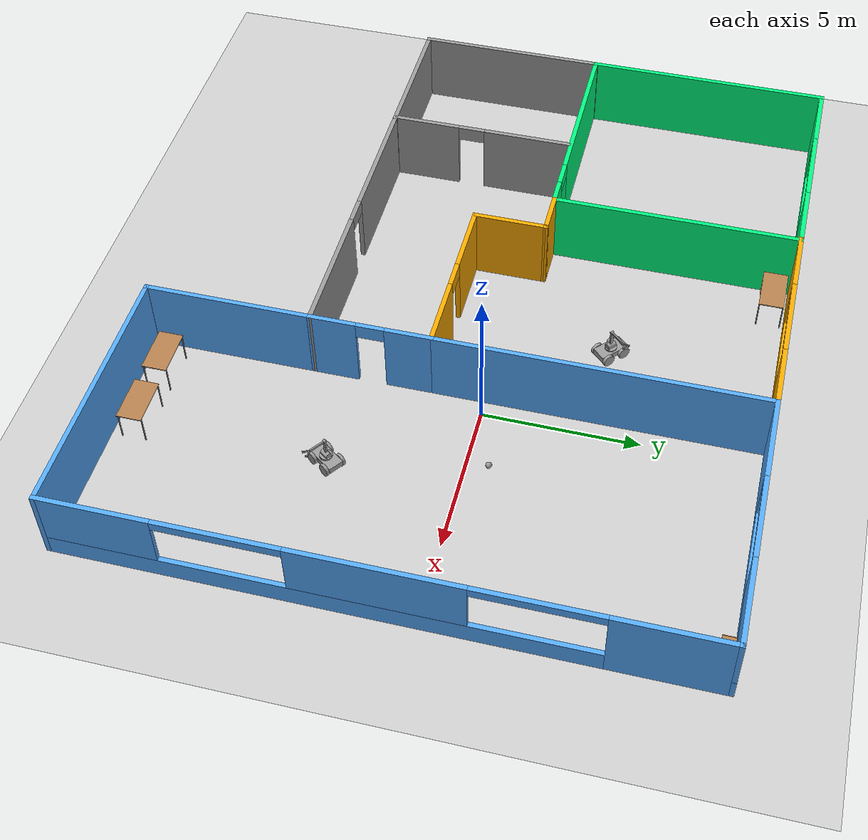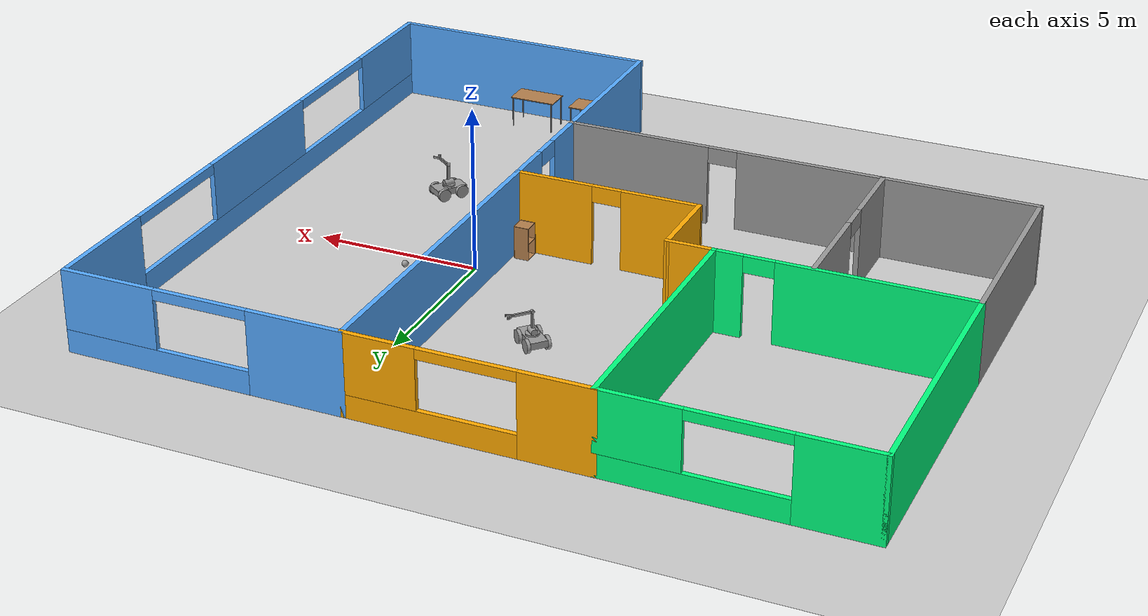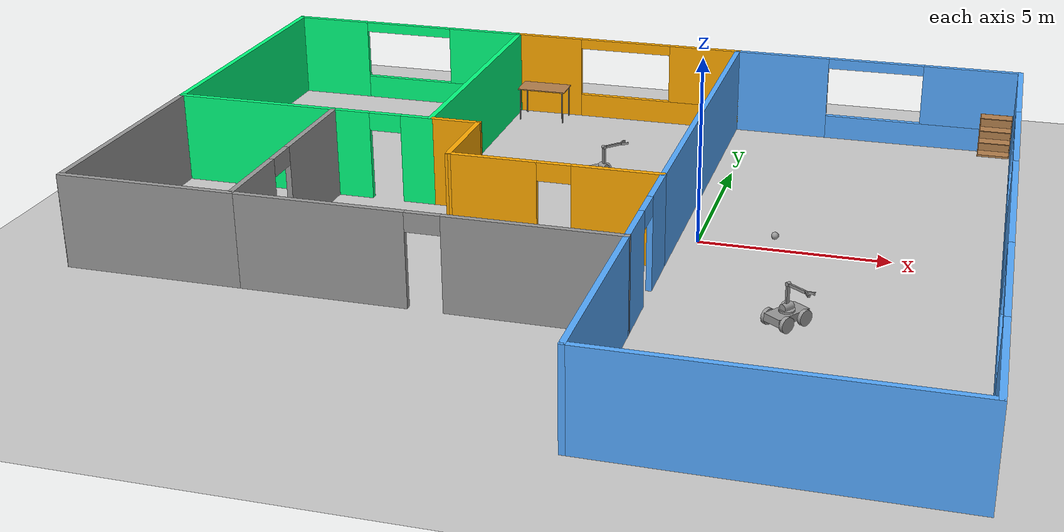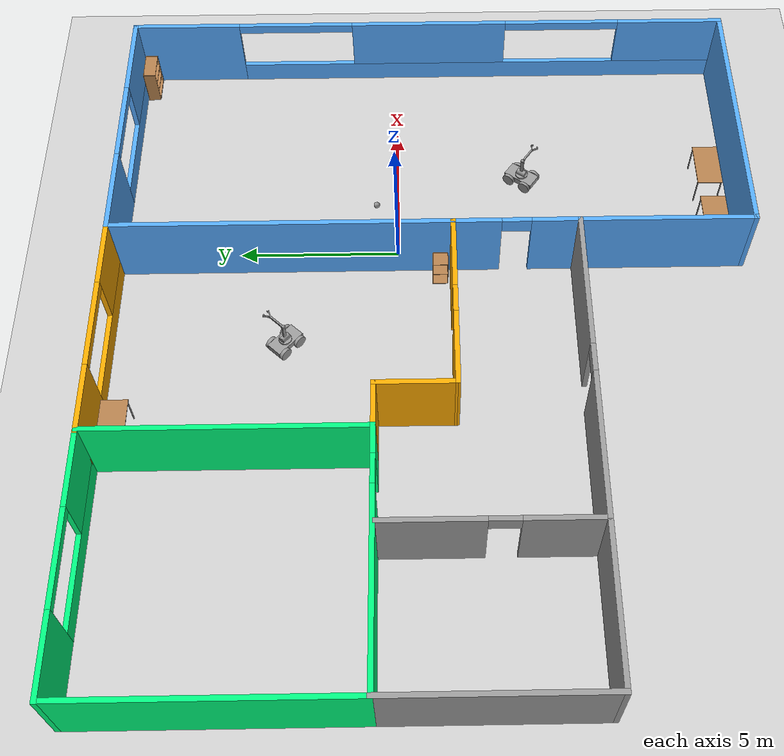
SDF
<sdf version="1.6">
 <world name="default">
  <plugin name="welcome" filename="libwelcome_message.so"/>
  <light name="sun" type="directional">
   <pose>0 0 10 0 -0 0</pose>
   <diffuse>0.8 0.8 0.8 1</diffuse>
   <specular>0.2 0.2 0.2 1</specular>
   <attenuation>
    <range>1000</range>
    <constant>0.9</constant>
    <linear>0.01</linear>
    <quadratic>0.001</quadratic>
   </attenuation>
   <direction>-0.5 0.1 -0.9</direction>
  </light>
  <model name="ground_plane">
   <static>1</static>
   <link name="link">
    <collision name="collision">
     <geometry><plane><normal>0 0 1</normal><size>100 100</size></plane></geometry>
     <surface><friction><ode><mu>100</mu><mu2>50</mu2></ode></friction></surface>
    </collision>
    <visual name="visual">
     <cast_shadows>0</cast_shadows>
     <geometry><plane><normal>0 0 1</normal><size>100 100</size></plane></geometry>
     <material>
      <script><uri>file://media/materials/scripts/gazebo.material</uri><name>Gazebo/Grey</name></script>
     </material>
    </visual>
   </link>
  </model>
  <gravity>0 0 -9.8</gravity>
  <magnetic_field>6e-06 2.3e-05 -4.2e-05</magnetic_field>
  <atmosphere type="adiabatic"/>
  <physics name="default_physics" default="0" type="ode">
   <max_step_size>0.001</max_step_size>
   <real_time_factor>1</real_time_factor>
   <real_time_update_rate>1000</real_time_update_rate>
  </physics>
  <scene><ambient>0.4 0.4 0.4 1</ambient><background>0.7 0.7 0.7 1</background><shadows>1</shadows></scene>
  <spherical_coordinates>
   <surface_model>EARTH_WGS84</surface_model>
   <latitude_deg>0</latitude_deg>
   <longitude_deg>0</longitude_deg>
   <elevation>0</elevation>
   <heading_deg>0</heading_deg>
  </spherical_coordinates>
  <model name="Building">
   <link name="Wall_10">
    <pose>2.99997 -7.175 0 0 -0 1.5708</pose>
    <visual name="Wall_10_Visual">
     <pose>0 0 1.25 0 -0 0</pose>
     <geometry><box><size>5.5 0.15 2.5</size></box></geometry>
     <material>
      <script><uri>file://media/materials/scripts/gazebo.material</uri><name>Gazebo/Grey</name></script>
      <ambient>0.333333 0.666667 1 1</ambient>
      <diffuse>0.7 0.7 0.7 1</diffuse>
      <specular>0.01 0.01 0.01 1</specular>
      <emissive>0 0 0 1</emissive>
     </material>
     <meta><layer>0</layer></meta>
    </visual>
    <collision name="Wall_10_Collision">
     <pose>0 0 1.25 0 -0 0</pose>
     <geometry><box><size>5.5 0.15 2.5</size></box></geometry>
     <surface>
      <friction>
       <ode><mu>1</mu><mu2>1</mu2><fdir1>0 0 0</fdir1><slip1>0</slip1><slip2>0</slip2></ode>
       <torsional>
        <coefficient>1</coefficient>
        <patch_radius>0</patch_radius>
        <surface_radius>0</surface_radius>
        <use_patch_radius>1</use_patch_radius>
        <ode><slip>0</slip></ode>
       </torsional>
      </friction>
      <bounce><restitution_coefficient>0</restitution_coefficient><threshold>1e+06</threshold></bounce>
      <contact>
       <collide_without_contact>0</collide_without_contact>
       <collide_without_contact_bitmask>1</collide_without_contact_bitmask>
       <collide_bitmask>1</collide_bitmask>
       <ode>
        <soft_cfm>0</soft_cfm>
        <soft_erp>0.2</soft_erp>
        <kp>1e+13</kp>
        <kd>1</kd>
        <max_vel>0.01</max_vel>
        <min_depth>0</min_depth>
       </ode>
       <bullet>
        <split_impulse>1</split_impulse>
        <split_impulse_penetration_threshold>-0.01</split_impulse_penetration_threshold>
        <soft_cfm>0</soft_cfm>
        <soft_erp>0.2</soft_erp>
        <kp>1e+13</kp>
        <kd>1</kd>
       </bullet>
      </contact>
     </surface>
    </collision>
   </link>
   <link name="Wall_48">
    <pose>-6.77372 -1.40614 0 0 0 -1.5708</pose>
    <visual name="Wall_48_Visual_0">
     <pose>-1.61017 0 1.25 0 -0 0</pose>
     <geometry><box><size>3.02966 0.15 2.5</size></box></geometry>
     <material>
      <script><uri>file://media/materials/scripts/gazebo.material</uri><name>Gazebo/Grey</name></script>
      <ambient>1 1 1 1</ambient>
      <diffuse>0.7 0.7 0.7 1</diffuse>
      <specular>0.01 0.01 0.01 1</specular>
      <emissive>0 0 0 1</emissive>
     </material>
     <meta><layer>0</layer></meta>
    </visual>
    <visual name="Wall_48_Visual_1">
     <pose>1.96483 0 1.25 0 -0 0</pose>
     <geometry><box><size>2.32034 0.15 2.5</size></box></geometry>
     <material>
      <script><uri>file://media/materials/scripts/gazebo.material</uri><name>Gazebo/Grey</name></script>
      <ambient>1 1 1 1</ambient>
      <diffuse>0.7 0.7 0.7 1</diffuse>
      <specular>0.01 0.01 0.01 1</specular>
      <emissive>0 0 0 1</emissive>
     </material>
     <meta><layer>0</layer></meta>
    </visual>
    <visual name="Wall_48_Visual_2">
     <pose>0.354659 0 2.25 0 -0 0</pose>
     <geometry><box><size>0.9 0.15 0.5</size></box></geometry>
     <material>
      <script><uri>file://media/materials/scripts/gazebo.material</uri><name>Gazebo/Grey</name></script>
      <ambient>1 1 1 1</ambient>
      <diffuse>0.7 0.7 0.7 1</diffuse>
      <specular>0.01 0.01 0.01 1</specular>
      <emissive>0 0 0 1</emissive>
     </material>
     <meta><layer>0</layer></meta>
    </visual>
    <collision name="Wall_48_Collision_0">
     <pose>-1.61017 0 1.25 0 -0 0</pose>
     <geometry><box><size>3.02966 0.15 2.5</size></box></geometry>
     <surface>
      <friction>
       <ode><mu>1</mu><mu2>1</mu2><fdir1>0 0 0</fdir1><slip1>0</slip1><slip2>0</slip2></ode>
       <torsional>
        <coefficient>1</coefficient>
        <patch_radius>0</patch_radius>
        <surface_radius>0</surface_radius>
        <use_patch_radius>1</use_patch_radius>
        <ode><slip>0</slip></ode>
       </torsional>
      </friction>
      <bounce><restitution_coefficient>0</restitution_coefficient><threshold>1e+06</threshold></bounce>
      <contact>
       <collide_without_contact>0</collide_without_contact>
       <collide_without_contact_bitmask>1</collide_without_contact_bitmask>
       <collide_bitmask>1</collide_bitmask>
       <ode>
        <soft_cfm>0</soft_cfm>
        <soft_erp>0.2</soft_erp>
        <kp>1e+13</kp>
        <kd>1</kd>
        <max_vel>0.01</max_vel>
        <min_depth>0</min_depth>
       </ode>
       <bullet>
        <split_impulse>1</split_impulse>
        <split_impulse_penetration_threshold>-0.01</split_impulse_penetration_threshold>
        <soft_cfm>0</soft_cfm>
        <soft_erp>0.2</soft_erp>
        <kp>1e+13</kp>
        <kd>1</kd>
       </bullet>
      </contact>
     </surface>
    </collision>
    <collision name="Wall_48_Collision_1">
     <pose>1.96483 0 1.25 0 -0 0</pose>
     <geometry><box><size>2.32034 0.15 2.5</size></box></geometry>
     <surface>
      <friction>
       <ode><mu>1</mu><mu2>1</mu2><fdir1>0 0 0</fdir1><slip1>0</slip1><slip2>0</slip2></ode>
       <torsional>
        <coefficient>1</coefficient>
        <patch_radius>0</patch_radius>
        <surface_radius>0</surface_radius>
        <use_patch_radius>1</use_patch_radius>
        <ode><slip>0</slip></ode>
       </torsional>
      </friction>
      <bounce><restitution_coefficient>0</restitution_coefficient><threshold>1e+06</threshold></bounce>
      <contact>
       <collide_without_contact>0</collide_without_contact>
       <collide_without_contact_bitmask>1</collide_without_contact_bitmask>
       <collide_bitmask>1</collide_bitmask>
       <ode>
        <soft_cfm>0</soft_cfm>
        <soft_erp>0.2</soft_erp>
        <kp>1e+13</kp>
        <kd>1</kd>
        <max_vel>0.01</max_vel>
        <min_depth>0</min_depth>
       </ode>
       <bullet>
        <split_impulse>1</split_impulse>
        <split_impulse_penetration_threshold>-0.01</split_impulse_penetration_threshold>
        <soft_cfm>0</soft_cfm>
        <soft_erp>0.2</soft_erp>
        <kp>1e+13</kp>
        <kd>1</kd>
       </bullet>
      </contact>
     </surface>
    </collision>
    <collision name="Wall_48_Collision_2">
     <pose>0.354659 0 2.25 0 -0 0</pose>
     <geometry><box><size>0.9 0.15 0.5</size></box></geometry>
     <surface>
      <friction>
       <ode><mu>1</mu><mu2>1</mu2><fdir1>0 0 0</fdir1><slip1>0</slip1><slip2>0</slip2></ode>
       <torsional>
        <coefficient>1</coefficient>
        <patch_radius>0</patch_radius>
        <surface_radius>0</surface_radius>
        <use_patch_radius>1</use_patch_radius>
        <ode><slip>0</slip></ode>
       </torsional>
      </friction>
      <bounce><restitution_coefficient>0</restitution_coefficient><threshold>1e+06</threshold></bounce>
      <contact>
       <collide_without_contact>0</collide_without_contact>
       <collide_without_contact_bitmask>1</collide_without_contact_bitmask>
       <collide_bitmask>1</collide_bitmask>
       <ode>
        <soft_cfm>0</soft_cfm>
        <soft_erp>0.2</soft_erp>
        <kp>1e+13</kp>
        <kd>1</kd>
        <max_vel>0.01</max_vel>
        <min_depth>0</min_depth>
       </ode>
       <bullet>
        <split_impulse>1</split_impulse>
        <split_impulse_penetration_threshold>-0.01</split_impulse_penetration_threshold>
        <soft_cfm>0</soft_cfm>
        <soft_erp>0.2</soft_erp>
        <kp>1e+13</kp>
        <kd>1</kd>
       </bullet>
      </contact>
     </surface>
    </collision>
   </link>
   <link name="Wall_50">
    <pose>-3.95628 5.78646 0 0 -0 1.5708</pose>
    <visual name="Wall_50_Visual">
     <pose>0 0 1.25 0 -0 0</pose>
     <geometry><box><size>8.25 0.15 2.5</size></box></geometry>
     <material>
      <script><uri>file://media/materials/scripts/gazebo.material</uri><name>Gazebo/Grey</name></script>
      <ambient>0 1 0.498039 1</ambient>
      <diffuse>0.7 0.7 0.7 1</diffuse>
      <specular>0.01 0.01 0.01 1</specular>
      <emissive>0 0 0 1</emissive>
     </material>
     <meta><layer>0</layer></meta>
    </visual>
    <collision name="Wall_50_Collision">
     <pose>0 0 1.25 0 -0 0</pose>
     <geometry><box><size>8.25 0.15 2.5</size></box></geometry>
     <surface>
      <friction>
       <ode><mu>1</mu><mu2>1</mu2><fdir1>0 0 0</fdir1><slip1>0</slip1><slip2>0</slip2></ode>
       <torsional>
        <coefficient>1</coefficient>
        <patch_radius>0</patch_radius>
        <surface_radius>0</surface_radius>
        <use_patch_radius>1</use_patch_radius>
        <ode><slip>0</slip></ode>
       </torsional>
      </friction>
      <bounce><restitution_coefficient>0</restitution_coefficient><threshold>1e+06</threshold></bounce>
      <contact>
       <collide_without_contact>0</collide_without_contact>
       <collide_without_contact_bitmask>1</collide_without_contact_bitmask>
       <collide_bitmask>1</collide_bitmask>
       <ode>
        <soft_cfm>0</soft_cfm>
        <soft_erp>0.2</soft_erp>
        <kp>1e+13</kp>
        <kd>1</kd>
        <max_vel>0.01</max_vel>
        <min_depth>0</min_depth>
       </ode>
       <bullet>
        <split_impulse>1</split_impulse>
        <split_impulse_penetration_threshold>-0.01</split_impulse_penetration_threshold>
        <soft_cfm>0</soft_cfm>
        <soft_erp>0.2</soft_erp>
        <kp>1e+13</kp>
        <kd>1</kd>
       </bullet>
      </contact>
     </surface>
    </collision>
   </link>
   <link name="Wall_53">
    <pose>0.190752 -0.639237 0 0 -0 0</pose>
    <visual name="Wall_53_Visual_0">
     <pose>-1.66349 0 1.25 0 -0 0</pose>
     <geometry><box><size>2.42302 0.15 2.5</size></box></geometry>
     <material>
      <script><uri>file://media/materials/scripts/gazebo.material</uri><name>Gazebo/Grey</name></script>
      <ambient>1 0.666667 0 1</ambient>
      <diffuse>0.7 0.7 0.7 1</diffuse>
      <specular>0.01 0.01 0.01 1</specular>
      <emissive>0 0 0 1</emissive>
     </material>
     <meta><layer>0</layer></meta>
    </visual>
    <visual name="Wall_53_Visual_1">
     <pose>1.66151 0 1.25 0 -0 0</pose>
     <geometry><box><size>2.42698 0.15 2.5</size></box></geometry>
     <material>
      <script><uri>file://media/materials/scripts/gazebo.material</uri><name>Gazebo/Grey</name></script>
      <ambient>1 0.666667 0 1</ambient>
      <diffuse>0.7 0.7 0.7 1</diffuse>
      <specular>0.01 0.01 0.01 1</specular>
      <emissive>0 0 0 1</emissive>
     </material>
     <meta><layer>0</layer></meta>
    </visual>
    <visual name="Wall_53_Visual_2">
     <pose>-0.001979 0 2.25 0 -0 0</pose>
     <geometry><box><size>0.9 0.15 0.5</size></box></geometry>
     <material>
      <script><uri>file://media/materials/scripts/gazebo.material</uri><name>Gazebo/Grey</name></script>
      <ambient>1 0.666667 0 1</ambient>
      <diffuse>0.7 0.7 0.7 1</diffuse>
      <specular>0.01 0.01 0.01 1</specular>
      <emissive>0 0 0 1</emissive>
     </material>
     <meta><layer>0</layer></meta>
    </visual>
    <collision name="Wall_53_Collision_0">
     <pose>-1.66349 0 1.25 0 -0 0</pose>
     <geometry><box><size>2.42302 0.15 2.5</size></box></geometry>
     <surface>
      <friction>
       <ode><mu>1</mu><mu2>1</mu2><fdir1>0 0 0</fdir1><slip1>0</slip1><slip2>0</slip2></ode>
       <torsional>
        <coefficient>1</coefficient>
        <patch_radius>0</patch_radius>
        <surface_radius>0</surface_radius>
        <use_patch_radius>1</use_patch_radius>
        <ode><slip>0</slip></ode>
       </torsional>
      </friction>
      <bounce><restitution_coefficient>0</restitution_coefficient><threshold>1e+06</threshold></bounce>
      <contact>
       <collide_without_contact>0</collide_without_contact>
       <collide_without_contact_bitmask>1</collide_without_contact_bitmask>
       <collide_bitmask>1</collide_bitmask>
       <ode>
        <soft_cfm>0</soft_cfm>
        <soft_erp>0.2</soft_erp>
        <kp>1e+13</kp>
        <kd>1</kd>
        <max_vel>0.01</max_vel>
        <min_depth>0</min_depth>
       </ode>
       <bullet>
        <split_impulse>1</split_impulse>
        <split_impulse_penetration_threshold>-0.01</split_impulse_penetration_threshold>
        <soft_cfm>0</soft_cfm>
        <soft_erp>0.2</soft_erp>
        <kp>1e+13</kp>
        <kd>1</kd>
       </bullet>
      </contact>
     </surface>
    </collision>
    <collision name="Wall_53_Collision_1">
     <pose>1.66151 0 1.25 0 -0 0</pose>
     <geometry><box><size>2.42698 0.15 2.5</size></box></geometry>
     <surface>
      <friction>
       <ode><mu>1</mu><mu2>1</mu2><fdir1>0 0 0</fdir1><slip1>0</slip1><slip2>0</slip2></ode>
       <torsional>
        <coefficient>1</coefficient>
        <patch_radius>0</patch_radius>
        <surface_radius>0</surface_radius>
        <use_patch_radius>1</use_patch_radius>
        <ode><slip>0</slip></ode>
       </torsional>
      </friction>
      <bounce><restitution_coefficient>0</restitution_coefficient><threshold>1e+06</threshold></bounce>
      <contact>
       <collide_without_contact>0</collide_without_contact>
       <collide_without_contact_bitmask>1</collide_without_contact_bitmask>
       <collide_bitmask>1</collide_bitmask>
       <ode>
        <soft_cfm>0</soft_cfm>
        <soft_erp>0.2</soft_erp>
        <kp>1e+13</kp>
        <kd>1</kd>
        <max_vel>0.01</max_vel>
        <min_depth>0</min_depth>
       </ode>
       <bullet>
        <split_impulse>1</split_impulse>
        <split_impulse_penetration_threshold>-0.01</split_impulse_penetration_threshold>
        <soft_cfm>0</soft_cfm>
        <soft_erp>0.2</soft_erp>
        <kp>1e+13</kp>
        <kd>1</kd>
       </bullet>
      </contact>
     </surface>
    </collision>
    <collision name="Wall_53_Collision_2">
     <pose>-0.001979 0 2.25 0 -0 0</pose>
     <geometry><box><size>0.9 0.15 0.5</size></box></geometry>
     <surface>
      <friction>
       <ode><mu>1</mu><mu2>1</mu2><fdir1>0 0 0</fdir1><slip1>0</slip1><slip2>0</slip2></ode>
       <torsional>
        <coefficient>1</coefficient>
        <patch_radius>0</patch_radius>
        <surface_radius>0</surface_radius>
        <use_patch_radius>1</use_patch_radius>
        <ode><slip>0</slip></ode>
       </torsional>
      </friction>
      <bounce><restitution_coefficient>0</restitution_coefficient><threshold>1e+06</threshold></bounce>
      <contact>
       <collide_without_contact>0</collide_without_contact>
       <collide_without_contact_bitmask>1</collide_without_contact_bitmask>
       <collide_bitmask>1</collide_bitmask>
       <ode>
        <soft_cfm>0</soft_cfm>
        <soft_erp>0.2</soft_erp>
        <kp>1e+13</kp>
        <kd>1</kd>
        <max_vel>0.01</max_vel>
        <min_depth>0</min_depth>
       </ode>
       <bullet>
        <split_impulse>1</split_impulse>
        <split_impulse_penetration_threshold>-0.01</split_impulse_penetration_threshold>
        <soft_cfm>0</soft_cfm>
        <soft_erp>0.2</soft_erp>
        <kp>1e+13</kp>
        <kd>1</kd>
       </bullet>
      </contact>
     </surface>
    </collision>
   </link>
   <link name="Wall_56">
    <pose>-3.28128 1.73646 0 0 -0 0</pose>
    <visual name="Wall_56_Visual">
     <pose>0 0 1.25 0 -0 0</pose>
     <geometry><box><size>1.5 0.15 2.5</size></box></geometry>
     <material>
      <script><uri>file://media/materials/scripts/gazebo.material</uri><name>Gazebo/Grey</name></script>
      <ambient>1 0.666667 0 1</ambient>
      <diffuse>0.7 0.7 0.7 1</diffuse>
      <specular>0.01 0.01 0.01 1</specular>
      <emissive>0 0 0 1</emissive>
     </material>
     <meta><layer>0</layer></meta>
    </visual>
    <collision name="Wall_56_Collision">
     <pose>0 0 1.25 0 -0 0</pose>
     <geometry><box><size>1.5 0.15 2.5</size></box></geometry>
     <surface>
      <friction>
       <ode><mu>1</mu><mu2>1</mu2><fdir1>0 0 0</fdir1><slip1>0</slip1><slip2>0</slip2></ode>
       <torsional>
        <coefficient>1</coefficient>
        <patch_radius>0</patch_radius>
        <surface_radius>0</surface_radius>
        <use_patch_radius>1</use_patch_radius>
        <ode><slip>0</slip></ode>
       </torsional>
      </friction>
      <bounce><restitution_coefficient>0</restitution_coefficient><threshold>1e+06</threshold></bounce>
      <contact>
       <collide_without_contact>0</collide_without_contact>
       <collide_without_contact_bitmask>1</collide_without_contact_bitmask>
       <collide_bitmask>1</collide_bitmask>
       <ode>
        <soft_cfm>0</soft_cfm>
        <soft_erp>0.2</soft_erp>
        <kp>1e+13</kp>
        <kd>1</kd>
        <max_vel>0.01</max_vel>
        <min_depth>0</min_depth>
       </ode>
       <bullet>
        <split_impulse>1</split_impulse>
        <split_impulse_penetration_threshold>-0.01</split_impulse_penetration_threshold>
        <soft_cfm>0</soft_cfm>
        <soft_erp>0.2</soft_erp>
        <kp>1e+13</kp>
        <kd>1</kd>
       </bullet>
      </contact>
     </surface>
    </collision>
   </link>
   <link name="Wall_57">
    <pose>-2.60776 0.548611 0 0 0 -1.57205</pose>
    <visual name="Wall_57_Visual">
     <pose>0 0 1.25 0 -0 0</pose>
     <geometry><box><size>2.5257 0.15 2.5</size></box></geometry>
     <material>
      <script><uri>file://media/materials/scripts/gazebo.material</uri><name>Gazebo/Grey</name></script>
      <ambient>1 0.666667 0 1</ambient>
      <diffuse>0.7 0.7 0.7 1</diffuse>
      <specular>0.01 0.01 0.01 1</specular>
      <emissive>0 0 0 1</emissive>
     </material>
     <meta><layer>0</layer></meta>
    </visual>
    <collision name="Wall_57_Collision">
     <pose>0 0 1.25 0 -0 0</pose>
     <geometry><box><size>2.5257 0.15 2.5</size></box></geometry>
     <surface>
      <friction>
       <ode><mu>1</mu><mu2>1</mu2><fdir1>0 0 0</fdir1><slip1>0</slip1><slip2>0</slip2></ode>
       <torsional>
        <coefficient>1</coefficient>
        <patch_radius>0</patch_radius>
        <surface_radius>0</surface_radius>
        <use_patch_radius>1</use_patch_radius>
        <ode><slip>0</slip></ode>
       </torsional>
      </friction>
      <bounce><restitution_coefficient>0</restitution_coefficient><threshold>1e+06</threshold></bounce>
      <contact>
       <collide_without_contact>0</collide_without_contact>
       <collide_without_contact_bitmask>1</collide_without_contact_bitmask>
       <collide_bitmask>1</collide_bitmask>
       <ode>
        <soft_cfm>0</soft_cfm>
        <soft_erp>0.2</soft_erp>
        <kp>1e+13</kp>
        <kd>1</kd>
        <max_vel>0.01</max_vel>
        <min_depth>0</min_depth>
       </ode>
       <bullet>
        <split_impulse>1</split_impulse>
        <split_impulse_penetration_threshold>-0.01</split_impulse_penetration_threshold>
        <soft_cfm>0</soft_cfm>
        <soft_erp>0.2</soft_erp>
        <kp>1e+13</kp>
        <kd>1</kd>
       </bullet>
      </contact>
     </surface>
    </collision>
   </link>
   <link name="Wall_59">
    <pose>-7.63128 1.73646 0 0 -0 3.14159</pose>
    <visual name="Wall_59_Visual_0">
     <pose>-3.28588 0 1.25 0 -0 0</pose>
     <geometry><box><size>0.928242 0.15 2.5</size></box></geometry>
     <material>
      <script><uri>file://media/materials/scripts/gazebo.material</uri><name>Gazebo/Grey</name></script>
      <ambient>0 1 0.498039 1</ambient>
      <diffuse>0.7 0.7 0.7 1</diffuse>
      <specular>0.01 0.01 0.01 1</specular>
      <emissive>0 0 0 1</emissive>
     </material>
     <meta><layer>0</layer></meta>
    </visual>
    <visual name="Wall_59_Visual_1">
     <pose>0.914121 0 1.25 0 -0 0</pose>
     <geometry><box><size>5.67176 0.15 2.5</size></box></geometry>
     <material>
      <script><uri>file://media/materials/scripts/gazebo.material</uri><name>Gazebo/Grey</name></script>
      <ambient>0 1 0.498039 1</ambient>
      <diffuse>0.7 0.7 0.7 1</diffuse>
      <specular>0.01 0.01 0.01 1</specular>
      <emissive>0 0 0 1</emissive>
     </material>
     <meta><layer>0</layer></meta>
    </visual>
    <visual name="Wall_59_Visual_2">
     <pose>-2.37176 0 2.25 0 -0 0</pose>
     <geometry><box><size>0.9 0.15 0.5</size></box></geometry>
     <material>
      <script><uri>file://media/materials/scripts/gazebo.material</uri><name>Gazebo/Grey</name></script>
      <ambient>0 1 0.498039 1</ambient>
      <diffuse>0.7 0.7 0.7 1</diffuse>
      <specular>0.01 0.01 0.01 1</specular>
      <emissive>0 0 0 1</emissive>
     </material>
     <meta><layer>0</layer></meta>
    </visual>
    <collision name="Wall_59_Collision_0">
     <pose>-3.28588 0 1.25 0 -0 0</pose>
     <geometry><box><size>0.928242 0.15 2.5</size></box></geometry>
     <surface>
      <friction>
       <ode><mu>1</mu><mu2>1</mu2><fdir1>0 0 0</fdir1><slip1>0</slip1><slip2>0</slip2></ode>
       <torsional>
        <coefficient>1</coefficient>
        <patch_radius>0</patch_radius>
        <surface_radius>0</surface_radius>
        <use_patch_radius>1</use_patch_radius>
        <ode><slip>0</slip></ode>
       </torsional>
      </friction>
      <bounce><restitution_coefficient>0</restitution_coefficient><threshold>1e+06</threshold></bounce>
      <contact>
       <collide_without_contact>0</collide_without_contact>
       <collide_without_contact_bitmask>1</collide_without_contact_bitmask>
       <collide_bitmask>1</collide_bitmask>
       <ode>
        <soft_cfm>0</soft_cfm>
        <soft_erp>0.2</soft_erp>
        <kp>1e+13</kp>
        <kd>1</kd>
        <max_vel>0.01</max_vel>
        <min_depth>0</min_depth>
       </ode>
       <bullet>
        <split_impulse>1</split_impulse>
        <split_impulse_penetration_threshold>-0.01</split_impulse_penetration_threshold>
        <soft_cfm>0</soft_cfm>
        <soft_erp>0.2</soft_erp>
        <kp>1e+13</kp>
        <kd>1</kd>
       </bullet>
      </contact>
     </surface>
    </collision>
    <collision name="Wall_59_Collision_1">
     <pose>0.914121 0 1.25 0 -0 0</pose>
     <geometry><box><size>5.67176 0.15 2.5</size></box></geometry>
     <surface>
      <friction>
       <ode><mu>1</mu><mu2>1</mu2><fdir1>0 0 0</fdir1><slip1>0</slip1><slip2>0</slip2></ode>
       <torsional>
        <coefficient>1</coefficient>
        <patch_radius>0</patch_radius>
        <surface_radius>0</surface_radius>
        <use_patch_radius>1</use_patch_radius>
        <ode><slip>0</slip></ode>
       </torsional>
      </friction>
      <bounce><restitution_coefficient>0</restitution_coefficient><threshold>1e+06</threshold></bounce>
      <contact>
       <collide_without_contact>0</collide_without_contact>
       <collide_without_contact_bitmask>1</collide_without_contact_bitmask>
       <collide_bitmask>1</collide_bitmask>
       <ode>
        <soft_cfm>0</soft_cfm>
        <soft_erp>0.2</soft_erp>
        <kp>1e+13</kp>
        <kd>1</kd>
        <max_vel>0.01</max_vel>
        <min_depth>0</min_depth>
       </ode>
       <bullet>
        <split_impulse>1</split_impulse>
        <split_impulse_penetration_threshold>-0.01</split_impulse_penetration_threshold>
        <soft_cfm>0</soft_cfm>
        <soft_erp>0.2</soft_erp>
        <kp>1e+13</kp>
        <kd>1</kd>
       </bullet>
      </contact>
     </surface>
    </collision>
    <collision name="Wall_59_Collision_2">
     <pose>-2.37176 0 2.25 0 -0 0</pose>
     <geometry><box><size>0.9 0.15 0.5</size></box></geometry>
     <surface>
      <friction>
       <ode><mu>1</mu><mu2>1</mu2><fdir1>0 0 0</fdir1><slip1>0</slip1><slip2>0</slip2></ode>
       <torsional>
        <coefficient>1</coefficient>
        <patch_radius>0</patch_radius>
        <surface_radius>0</surface_radius>
        <use_patch_radius>1</use_patch_radius>
        <ode><slip>0</slip></ode>
       </torsional>
      </friction>
      <bounce><restitution_coefficient>0</restitution_coefficient><threshold>1e+06</threshold></bounce>
      <contact>
       <collide_without_contact>0</collide_without_contact>
       <collide_without_contact_bitmask>1</collide_without_contact_bitmask>
       <collide_bitmask>1</collide_bitmask>
       <ode>
        <soft_cfm>0</soft_cfm>
        <soft_erp>0.2</soft_erp>
        <kp>1e+13</kp>
        <kd>1</kd>
        <max_vel>0.01</max_vel>
        <min_depth>0</min_depth>
       </ode>
       <bullet>
        <split_impulse>1</split_impulse>
        <split_impulse_penetration_threshold>-0.01</split_impulse_penetration_threshold>
        <soft_cfm>0</soft_cfm>
        <soft_erp>0.2</soft_erp>
        <kp>1e+13</kp>
        <kd>1</kd>
       </bullet>
      </contact>
     </surface>
    </collision>
   </link>
   <link name="Wall_63">
    <pose>-7.67503 9.85 0 0 -0 0</pose>
    <visual name="Wall_63_Visual_0">
     <pose>-2.57109 0 1.25 0 -0 0</pose>
     <geometry><box><size>2.35781 0.15 2.5</size></box></geometry>
     <material>
      <script><uri>file://media/materials/scripts/gazebo.material</uri><name>Gazebo/Grey</name></script>
      <ambient>0 1 0.498039 1</ambient>
      <diffuse>0.7 0.7 0.7 1</diffuse>
      <specular>0.01 0.01 0.01 1</specular>
      <emissive>0 0 0 1</emissive>
     </material>
     <meta><layer>0</layer></meta>
    </visual>
    <visual name="Wall_63_Visual_1">
     <pose>1.17891 0 0.35 0 -0 0</pose>
     <geometry><box><size>5.14219 0.15 0.7</size></box></geometry>
     <material>
      <script><uri>file://media/materials/scripts/gazebo.material</uri><name>Gazebo/Grey</name></script>
      <ambient>0 1 0.498039 1</ambient>
      <diffuse>0.7 0.7 0.7 1</diffuse>
      <specular>0.01 0.01 0.01 1</specular>
      <emissive>0 0 0 1</emissive>
     </material>
     <meta><layer>0</layer></meta>
    </visual>
    <visual name="Wall_63_Visual_2">
     <pose>2.57891 0 1.6 0 -0 0</pose>
     <geometry><box><size>2.34219 0.15 1.8</size></box></geometry>
     <material>
      <script><uri>file://media/materials/scripts/gazebo.material</uri><name>Gazebo/Grey</name></script>
      <ambient>0 1 0.498039 1</ambient>
      <diffuse>0.7 0.7 0.7 1</diffuse>
      <specular>0.01 0.01 0.01 1</specular>
      <emissive>0 0 0 1</emissive>
     </material>
     <meta><layer>0</layer></meta>
    </visual>
    <visual name="Wall_63_Visual_3">
     <pose>0.007813 0 2.35 0 -0 0</pose>
     <geometry><box><size>2.8 0.15 0.3</size></box></geometry>
     <material>
      <script><uri>file://media/materials/scripts/gazebo.material</uri><name>Gazebo/Grey</name></script>
      <ambient>0 1 0.498039 1</ambient>
      <diffuse>0.7 0.7 0.7 1</diffuse>
      <specular>0.01 0.01 0.01 1</specular>
      <emissive>0 0 0 1</emissive>
     </material>
     <meta><layer>0</layer></meta>
    </visual>
    <collision name="Wall_63_Collision_0">
     <pose>-2.57109 0 1.25 0 -0 0</pose>
     <geometry><box><size>2.35781 0.15 2.5</size></box></geometry>
     <surface>
      <friction>
       <ode><mu>1</mu><mu2>1</mu2><fdir1>0 0 0</fdir1><slip1>0</slip1><slip2>0</slip2></ode>
       <torsional>
        <coefficient>1</coefficient>
        <patch_radius>0</patch_radius>
        <surface_radius>0</surface_radius>
        <use_patch_radius>1</use_patch_radius>
        <ode><slip>0</slip></ode>
       </torsional>
      </friction>
      <bounce><restitution_coefficient>0</restitution_coefficient><threshold>1e+06</threshold></bounce>
      <contact>
       <collide_without_contact>0</collide_without_contact>
       <collide_without_contact_bitmask>1</collide_without_contact_bitmask>
       <collide_bitmask>1</collide_bitmask>
       <ode>
        <soft_cfm>0</soft_cfm>
        <soft_erp>0.2</soft_erp>
        <kp>1e+13</kp>
        <kd>1</kd>
        <max_vel>0.01</max_vel>
        <min_depth>0</min_depth>
       </ode>
       <bullet>
        <split_impulse>1</split_impulse>
        <split_impulse_penetration_threshold>-0.01</split_impulse_penetration_threshold>
        <soft_cfm>0</soft_cfm>
        <soft_erp>0.2</soft_erp>
        <kp>1e+13</kp>
        <kd>1</kd>
       </bullet>
      </contact>
     </surface>
    </collision>
    <collision name="Wall_63_Collision_1">
     <pose>1.17891 0 0.35 0 -0 0</pose>
     <geometry><box><size>5.14219 0.15 0.7</size></box></geometry>
     <surface>
      <friction>
       <ode><mu>1</mu><mu2>1</mu2><fdir1>0 0 0</fdir1><slip1>0</slip1><slip2>0</slip2></ode>
       <torsional>
        <coefficient>1</coefficient>
        <patch_radius>0</patch_radius>
        <surface_radius>0</surface_radius>
        <use_patch_radius>1</use_patch_radius>
        <ode><slip>0</slip></ode>
       </torsional>
      </friction>
      <bounce><restitution_coefficient>0</restitution_coefficient><threshold>1e+06</threshold></bounce>
      <contact>
       <collide_without_contact>0</collide_without_contact>
       <collide_without_contact_bitmask>1</collide_without_contact_bitmask>
       <collide_bitmask>1</collide_bitmask>
       <ode>
        <soft_cfm>0</soft_cfm>
        <soft_erp>0.2</soft_erp>
        <kp>1e+13</kp>
        <kd>1</kd>
        <max_vel>0.01</max_vel>
        <min_depth>0</min_depth>
       </ode>
       <bullet>
        <split_impulse>1</split_impulse>
        <split_impulse_penetration_threshold>-0.01</split_impulse_penetration_threshold>
        <soft_cfm>0</soft_cfm>
        <soft_erp>0.2</soft_erp>
        <kp>1e+13</kp>
        <kd>1</kd>
       </bullet>
      </contact>
     </surface>
    </collision>
    <collision name="Wall_63_Collision_2">
     <pose>2.57891 0 1.6 0 -0 0</pose>
     <geometry><box><size>2.34219 0.15 1.8</size></box></geometry>
     <surface>
      <friction>
       <ode><mu>1</mu><mu2>1</mu2><fdir1>0 0 0</fdir1><slip1>0</slip1><slip2>0</slip2></ode>
       <torsional>
        <coefficient>1</coefficient>
        <patch_radius>0</patch_radius>
        <surface_radius>0</surface_radius>
        <use_patch_radius>1</use_patch_radius>
        <ode><slip>0</slip></ode>
       </torsional>
      </friction>
      <bounce><restitution_coefficient>0</restitution_coefficient><threshold>1e+06</threshold></bounce>
      <contact>
       <collide_without_contact>0</collide_without_contact>
       <collide_without_contact_bitmask>1</collide_without_contact_bitmask>
       <collide_bitmask>1</collide_bitmask>
       <ode>
        <soft_cfm>0</soft_cfm>
        <soft_erp>0.2</soft_erp>
        <kp>1e+13</kp>
        <kd>1</kd>
        <max_vel>0.01</max_vel>
        <min_depth>0</min_depth>
       </ode>
       <bullet>
        <split_impulse>1</split_impulse>
        <split_impulse_penetration_threshold>-0.01</split_impulse_penetration_threshold>
        <soft_cfm>0</soft_cfm>
        <soft_erp>0.2</soft_erp>
        <kp>1e+13</kp>
        <kd>1</kd>
       </bullet>
      </contact>
     </surface>
    </collision>
    <collision name="Wall_63_Collision_3">
     <pose>0.007813 0 2.35 0 -0 0</pose>
     <geometry><box><size>2.8 0.15 0.3</size></box></geometry>
     <surface>
      <friction>
       <ode><mu>1</mu><mu2>1</mu2><fdir1>0 0 0</fdir1><slip1>0</slip1><slip2>0</slip2></ode>
       <torsional>
        <coefficient>1</coefficient>
        <patch_radius>0</patch_radius>
        <surface_radius>0</surface_radius>
        <use_patch_radius>1</use_patch_radius>
        <ode><slip>0</slip></ode>
       </torsional>
      </friction>
      <bounce><restitution_coefficient>0</restitution_coefficient><threshold>1e+06</threshold></bounce>
      <contact>
       <collide_without_contact>0</collide_without_contact>
       <collide_without_contact_bitmask>1</collide_without_contact_bitmask>
       <collide_bitmask>1</collide_bitmask>
       <ode>
        <soft_cfm>0</soft_cfm>
        <soft_erp>0.2</soft_erp>
        <kp>1e+13</kp>
        <kd>1</kd>
        <max_vel>0.01</max_vel>
        <min_depth>0</min_depth>
       </ode>
       <bullet>
        <split_impulse>1</split_impulse>
        <split_impulse_penetration_threshold>-0.01</split_impulse_penetration_threshold>
        <soft_cfm>0</soft_cfm>
        <soft_erp>0.2</soft_erp>
        <kp>1e+13</kp>
        <kd>1</kd>
       </bullet>
      </contact>
     </surface>
    </collision>
   </link>
   <link name="Wall_64">
    <pose>-0.500034 9.85 0 0 -0 0</pose>
    <visual name="Wall_64_Visual_0">
     <pose>-2.49241 0 1.25 0 -0 0</pose>
     <geometry><box><size>2.16519 0.15 2.5</size></box></geometry>
     <material>
      <script><uri>file://media/materials/scripts/gazebo.material</uri><name>Gazebo/Grey</name></script>
      <ambient>1 0.666667 0 1</ambient>
      <diffuse>0.7 0.7 0.7 1</diffuse>
      <specular>0.01 0.01 0.01 1</specular>
      <emissive>0 0 0 1</emissive>
     </material>
     <meta><layer>0</layer></meta>
    </visual>
    <visual name="Wall_64_Visual_1">
     <pose>1.08259 0 0.35 0 -0 0</pose>
     <geometry><box><size>4.98481 0.15 0.7</size></box></geometry>
     <material>
      <script><uri>file://media/materials/scripts/gazebo.material</uri><name>Gazebo/Grey</name></script>
      <ambient>1 0.666667 0 1</ambient>
      <diffuse>0.7 0.7 0.7 1</diffuse>
      <specular>0.01 0.01 0.01 1</specular>
      <emissive>0 0 0 1</emissive>
     </material>
     <meta><layer>0</layer></meta>
    </visual>
    <visual name="Wall_64_Visual_2">
     <pose>2.48259 0 1.6 0 -0 0</pose>
     <geometry><box><size>2.18481 0.15 1.8</size></box></geometry>
     <material>
      <script><uri>file://media/materials/scripts/gazebo.material</uri><name>Gazebo/Grey</name></script>
      <ambient>1 0.666667 0 1</ambient>
      <diffuse>0.7 0.7 0.7 1</diffuse>
      <specular>0.01 0.01 0.01 1</specular>
      <emissive>0 0 0 1</emissive>
     </material>
     <meta><layer>0</layer></meta>
    </visual>
    <visual name="Wall_64_Visual_3">
     <pose>-0.009811 0 2.35 0 -0 0</pose>
     <geometry><box><size>2.8 0.15 0.3</size></box></geometry>
     <material>
      <script><uri>file://media/materials/scripts/gazebo.material</uri><name>Gazebo/Grey</name></script>
      <ambient>1 0.666667 0 1</ambient>
      <diffuse>0.7 0.7 0.7 1</diffuse>
      <specular>0.01 0.01 0.01 1</specular>
      <emissive>0 0 0 1</emissive>
     </material>
     <meta><layer>0</layer></meta>
    </visual>
    <collision name="Wall_64_Collision_0">
     <pose>-2.49241 0 1.25 0 -0 0</pose>
     <geometry><box><size>2.16519 0.15 2.5</size></box></geometry>
     <surface>
      <friction>
       <ode><mu>1</mu><mu2>1</mu2><fdir1>0 0 0</fdir1><slip1>0</slip1><slip2>0</slip2></ode>
       <torsional>
        <coefficient>1</coefficient>
        <patch_radius>0</patch_radius>
        <surface_radius>0</surface_radius>
        <use_patch_radius>1</use_patch_radius>
        <ode><slip>0</slip></ode>
       </torsional>
      </friction>
      <bounce><restitution_coefficient>0</restitution_coefficient><threshold>1e+06</threshold></bounce>
      <contact>
       <collide_without_contact>0</collide_without_contact>
       <collide_without_contact_bitmask>1</collide_without_contact_bitmask>
       <collide_bitmask>1</collide_bitmask>
       <ode>
        <soft_cfm>0</soft_cfm>
        <soft_erp>0.2</soft_erp>
        <kp>1e+13</kp>
        <kd>1</kd>
        <max_vel>0.01</max_vel>
        <min_depth>0</min_depth>
       </ode>
       <bullet>
        <split_impulse>1</split_impulse>
        <split_impulse_penetration_threshold>-0.01</split_impulse_penetration_threshold>
        <soft_cfm>0</soft_cfm>
        <soft_erp>0.2</soft_erp>
        <kp>1e+13</kp>
        <kd>1</kd>
       </bullet>
      </contact>
     </surface>
    </collision>
    <collision name="Wall_64_Collision_1">
     <pose>1.08259 0 0.35 0 -0 0</pose>
     <geometry><box><size>4.98481 0.15 0.7</size></box></geometry>
     <surface>
      <friction>
       <ode><mu>1</mu><mu2>1</mu2><fdir1>0 0 0</fdir1><slip1>0</slip1><slip2>0</slip2></ode>
       <torsional>
        <coefficient>1</coefficient>
        <patch_radius>0</patch_radius>
        <surface_radius>0</surface_radius>
        <use_patch_radius>1</use_patch_radius>
        <ode><slip>0</slip></ode>
       </torsional>
      </friction>
      <bounce><restitution_coefficient>0</restitution_coefficient><threshold>1e+06</threshold></bounce>
      <contact>
       <collide_without_contact>0</collide_without_contact>
       <collide_without_contact_bitmask>1</collide_without_contact_bitmask>
       <collide_bitmask>1</collide_bitmask>
       <ode>
        <soft_cfm>0</soft_cfm>
        <soft_erp>0.2</soft_erp>
        <kp>1e+13</kp>
        <kd>1</kd>
        <max_vel>0.01</max_vel>
        <min_depth>0</min_depth>
       </ode>
       <bullet>
        <split_impulse>1</split_impulse>
        <split_impulse_penetration_threshold>-0.01</split_impulse_penetration_threshold>
        <soft_cfm>0</soft_cfm>
        <soft_erp>0.2</soft_erp>
        <kp>1e+13</kp>
        <kd>1</kd>
       </bullet>
      </contact>
     </surface>
    </collision>
    <collision name="Wall_64_Collision_2">
     <pose>2.48259 0 1.6 0 -0 0</pose>
     <geometry><box><size>2.18481 0.15 1.8</size></box></geometry>
     <surface>
      <friction>
       <ode><mu>1</mu><mu2>1</mu2><fdir1>0 0 0</fdir1><slip1>0</slip1><slip2>0</slip2></ode>
       <torsional>
        <coefficient>1</coefficient>
        <patch_radius>0</patch_radius>
        <surface_radius>0</surface_radius>
        <use_patch_radius>1</use_patch_radius>
        <ode><slip>0</slip></ode>
       </torsional>
      </friction>
      <bounce><restitution_coefficient>0</restitution_coefficient><threshold>1e+06</threshold></bounce>
      <contact>
       <collide_without_contact>0</collide_without_contact>
       <collide_without_contact_bitmask>1</collide_without_contact_bitmask>
       <collide_bitmask>1</collide_bitmask>
       <ode>
        <soft_cfm>0</soft_cfm>
        <soft_erp>0.2</soft_erp>
        <kp>1e+13</kp>
        <kd>1</kd>
        <max_vel>0.01</max_vel>
        <min_depth>0</min_depth>
       </ode>
       <bullet>
        <split_impulse>1</split_impulse>
        <split_impulse_penetration_threshold>-0.01</split_impulse_penetration_threshold>
        <soft_cfm>0</soft_cfm>
        <soft_erp>0.2</soft_erp>
        <kp>1e+13</kp>
        <kd>1</kd>
       </bullet>
      </contact>
     </surface>
    </collision>
    <collision name="Wall_64_Collision_3">
     <pose>-0.009811 0 2.35 0 -0 0</pose>
     <geometry><box><size>2.8 0.15 0.3</size></box></geometry>
     <surface>
      <friction>
       <ode><mu>1</mu><mu2>1</mu2><fdir1>0 0 0</fdir1><slip1>0</slip1><slip2>0</slip2></ode>
       <torsional>
        <coefficient>1</coefficient>
        <patch_radius>0</patch_radius>
        <surface_radius>0</surface_radius>
        <use_patch_radius>1</use_patch_radius>
        <ode><slip>0</slip></ode>
       </torsional>
      </friction>
      <bounce><restitution_coefficient>0</restitution_coefficient><threshold>1e+06</threshold></bounce>
      <contact>
       <collide_without_contact>0</collide_without_contact>
       <collide_without_contact_bitmask>1</collide_without_contact_bitmask>
       <collide_bitmask>1</collide_bitmask>
       <ode>
        <soft_cfm>0</soft_cfm>
        <soft_erp>0.2</soft_erp>
        <kp>1e+13</kp>
        <kd>1</kd>
        <max_vel>0.01</max_vel>
        <min_depth>0</min_depth>
       </ode>
       <bullet>
        <split_impulse>1</split_impulse>
        <split_impulse_penetration_threshold>-0.01</split_impulse_penetration_threshold>
        <soft_cfm>0</soft_cfm>
        <soft_erp>0.2</soft_erp>
        <kp>1e+13</kp>
        <kd>1</kd>
       </bullet>
      </contact>
     </surface>
    </collision>
   </link>
   <link name="Wall_65">
    <pose>7.175 9.84997 0 0 0 -7e-06</pose>
    <visual name="Wall_65_Visual_0">
     <pose>-2.82562 0 1.25 0 -0 0</pose>
     <geometry><box><size>2.84883 0.15 2.5</size></box></geometry>
     <material>
      <script><uri>file://media/materials/scripts/gazebo.material</uri><name>Gazebo/Grey</name></script>
      <ambient>0.333333 0.666667 1 1</ambient>
      <diffuse>0.7 0.7 0.7 1</diffuse>
      <specular>0.01 0.01 0.01 1</specular>
      <emissive>0 0 0 1</emissive>
     </material>
     <meta><layer>0</layer></meta>
    </visual>
    <visual name="Wall_65_Visual_1">
     <pose>1.42442 0 0.35 0 -0 0</pose>
     <geometry><box><size>5.65124 0.15 0.7</size></box></geometry>
     <material>
      <script><uri>file://media/materials/scripts/gazebo.material</uri><name>Gazebo/Grey</name></script>
      <ambient>0.333333 0.666667 1 1</ambient>
      <diffuse>0.7 0.7 0.7 1</diffuse>
      <specular>0.01 0.01 0.01 1</specular>
      <emissive>0 0 0 1</emissive>
     </material>
     <meta><layer>0</layer></meta>
    </visual>
    <visual name="Wall_65_Visual_2">
     <pose>2.82442 0 1.6 0 -0 0</pose>
     <geometry><box><size>2.85124 0.15 1.8</size></box></geometry>
     <material>
      <script><uri>file://media/materials/scripts/gazebo.material</uri><name>Gazebo/Grey</name></script>
      <ambient>0.333333 0.666667 1 1</ambient>
      <diffuse>0.7 0.7 0.7 1</diffuse>
      <specular>0.01 0.01 0.01 1</specular>
      <emissive>0 0 0 1</emissive>
     </material>
     <meta><layer>0</layer></meta>
    </visual>
    <visual name="Wall_65_Visual_3">
     <pose>-0.001203 0 2.35 0 -0 0</pose>
     <geometry><box><size>2.8 0.15 0.3</size></box></geometry>
     <material>
      <script><uri>file://media/materials/scripts/gazebo.material</uri><name>Gazebo/Grey</name></script>
      <ambient>0.333333 0.666667 1 1</ambient>
      <diffuse>0.7 0.7 0.7 1</diffuse>
      <specular>0.01 0.01 0.01 1</specular>
      <emissive>0 0 0 1</emissive>
     </material>
     <meta><layer>0</layer></meta>
    </visual>
    <collision name="Wall_65_Collision_0">
     <pose>-2.82562 0 1.25 0 -0 0</pose>
     <geometry><box><size>2.84883 0.15 2.5</size></box></geometry>
     <surface>
      <friction>
       <ode><mu>1</mu><mu2>1</mu2><fdir1>0 0 0</fdir1><slip1>0</slip1><slip2>0</slip2></ode>
       <torsional>
        <coefficient>1</coefficient>
        <patch_radius>0</patch_radius>
        <surface_radius>0</surface_radius>
        <use_patch_radius>1</use_patch_radius>
        <ode><slip>0</slip></ode>
       </torsional>
      </friction>
      <bounce><restitution_coefficient>0</restitution_coefficient><threshold>1e+06</threshold></bounce>
      <contact>
       <collide_without_contact>0</collide_without_contact>
       <collide_without_contact_bitmask>1</collide_without_contact_bitmask>
       <collide_bitmask>1</collide_bitmask>
       <ode>
        <soft_cfm>0</soft_cfm>
        <soft_erp>0.2</soft_erp>
        <kp>1e+13</kp>
        <kd>1</kd>
        <max_vel>0.01</max_vel>
        <min_depth>0</min_depth>
       </ode>
       <bullet>
        <split_impulse>1</split_impulse>
        <split_impulse_penetration_threshold>-0.01</split_impulse_penetration_threshold>
        <soft_cfm>0</soft_cfm>
        <soft_erp>0.2</soft_erp>
        <kp>1e+13</kp>
        <kd>1</kd>
       </bullet>
      </contact>
     </surface>
    </collision>
    <collision name="Wall_65_Collision_1">
     <pose>1.42442 0 0.35 0 -0 0</pose>
     <geometry><box><size>5.65124 0.15 0.7</size></box></geometry>
     <surface>
      <friction>
       <ode><mu>1</mu><mu2>1</mu2><fdir1>0 0 0</fdir1><slip1>0</slip1><slip2>0</slip2></ode>
       <torsional>
        <coefficient>1</coefficient>
        <patch_radius>0</patch_radius>
        <surface_radius>0</surface_radius>
        <use_patch_radius>1</use_patch_radius>
        <ode><slip>0</slip></ode>
       </torsional>
      </friction>
      <bounce><restitution_coefficient>0</restitution_coefficient><threshold>1e+06</threshold></bounce>
      <contact>
       <collide_without_contact>0</collide_without_contact>
       <collide_without_contact_bitmask>1</collide_without_contact_bitmask>
       <collide_bitmask>1</collide_bitmask>
       <ode>
        <soft_cfm>0</soft_cfm>
        <soft_erp>0.2</soft_erp>
        <kp>1e+13</kp>
        <kd>1</kd>
        <max_vel>0.01</max_vel>
        <min_depth>0</min_depth>
       </ode>
       <bullet>
        <split_impulse>1</split_impulse>
        <split_impulse_penetration_threshold>-0.01</split_impulse_penetration_threshold>
        <soft_cfm>0</soft_cfm>
        <soft_erp>0.2</soft_erp>
        <kp>1e+13</kp>
        <kd>1</kd>
       </bullet>
      </contact>
     </surface>
    </collision>
    <collision name="Wall_65_Collision_2">
     <pose>2.82442 0 1.6 0 -0 0</pose>
     <geometry><box><size>2.85124 0.15 1.8</size></box></geometry>
     <surface>
      <friction>
       <ode><mu>1</mu><mu2>1</mu2><fdir1>0 0 0</fdir1><slip1>0</slip1><slip2>0</slip2></ode>
       <torsional>
        <coefficient>1</coefficient>
        <patch_radius>0</patch_radius>
        <surface_radius>0</surface_radius>
        <use_patch_radius>1</use_patch_radius>
        <ode><slip>0</slip></ode>
       </torsional>
      </friction>
      <bounce><restitution_coefficient>0</restitution_coefficient><threshold>1e+06</threshold></bounce>
      <contact>
       <collide_without_contact>0</collide_without_contact>
       <collide_without_contact_bitmask>1</collide_without_contact_bitmask>
       <collide_bitmask>1</collide_bitmask>
       <ode>
        <soft_cfm>0</soft_cfm>
        <soft_erp>0.2</soft_erp>
        <kp>1e+13</kp>
        <kd>1</kd>
        <max_vel>0.01</max_vel>
        <min_depth>0</min_depth>
       </ode>
       <bullet>
        <split_impulse>1</split_impulse>
        <split_impulse_penetration_threshold>-0.01</split_impulse_penetration_threshold>
        <soft_cfm>0</soft_cfm>
        <soft_erp>0.2</soft_erp>
        <kp>1e+13</kp>
        <kd>1</kd>
       </bullet>
      </contact>
     </surface>
    </collision>
    <collision name="Wall_65_Collision_3">
     <pose>-0.001203 0 2.35 0 -0 0</pose>
     <geometry><box><size>2.8 0.15 0.3</size></box></geometry>
     <surface>
      <friction>
       <ode><mu>1</mu><mu2>1</mu2><fdir1>0 0 0</fdir1><slip1>0</slip1><slip2>0</slip2></ode>
       <torsional>
        <coefficient>1</coefficient>
        <patch_radius>0</patch_radius>
        <surface_radius>0</surface_radius>
        <use_patch_radius>1</use_patch_radius>
        <ode><slip>0</slip></ode>
       </torsional>
      </friction>
      <bounce><restitution_coefficient>0</restitution_coefficient><threshold>1e+06</threshold></bounce>
      <contact>
       <collide_without_contact>0</collide_without_contact>
       <collide_without_contact_bitmask>1</collide_without_contact_bitmask>
       <collide_bitmask>1</collide_bitmask>
       <ode>
        <soft_cfm>0</soft_cfm>
        <soft_erp>0.2</soft_erp>
        <kp>1e+13</kp>
        <kd>1</kd>
        <max_vel>0.01</max_vel>
        <min_depth>0</min_depth>
       </ode>
       <bullet>
        <split_impulse>1</split_impulse>
        <split_impulse_penetration_threshold>-0.01</split_impulse_penetration_threshold>
        <soft_cfm>0</soft_cfm>
        <soft_erp>0.2</soft_erp>
        <kp>1e+13</kp>
        <kd>1</kd>
       </bullet>
      </contact>
     </surface>
    </collision>
   </link>
   <link name="Wall_67">
    <pose>-11.35 5.8 0 0 0 -1.5708</pose>
    <visual name="Wall_67_Visual">
     <pose>0 0 1.25 0 -0 0</pose>
     <geometry><box><size>8.25 0.15 2.5</size></box></geometry>
     <material>
      <script><uri>file://media/materials/scripts/gazebo.material</uri><name>Gazebo/Grey</name></script>
      <ambient>0 1 0.498039 1</ambient>
      <diffuse>0.7 0.7 0.7 1</diffuse>
      <specular>0.01 0.01 0.01 1</specular>
      <emissive>0 0 0 1</emissive>
     </material>
     <meta><layer>0</layer></meta>
    </visual>
    <collision name="Wall_67_Collision">
     <pose>0 0 1.25 0 -0 0</pose>
     <geometry><box><size>8.25 0.15 2.5</size></box></geometry>
     <surface>
      <friction>
       <ode><mu>1</mu><mu2>1</mu2><fdir1>0 0 0</fdir1><slip1>0</slip1><slip2>0</slip2></ode>
       <torsional>
        <coefficient>1</coefficient>
        <patch_radius>0</patch_radius>
        <surface_radius>0</surface_radius>
        <use_patch_radius>1</use_patch_radius>
        <ode><slip>0</slip></ode>
       </torsional>
      </friction>
      <bounce><restitution_coefficient>0</restitution_coefficient><threshold>1e+06</threshold></bounce>
      <contact>
       <collide_without_contact>0</collide_without_contact>
       <collide_without_contact_bitmask>1</collide_without_contact_bitmask>
       <collide_bitmask>1</collide_bitmask>
       <ode>
        <soft_cfm>0</soft_cfm>
        <soft_erp>0.2</soft_erp>
        <kp>1e+13</kp>
        <kd>1</kd>
        <max_vel>0.01</max_vel>
        <min_depth>0</min_depth>
       </ode>
       <bullet>
        <split_impulse>1</split_impulse>
        <split_impulse_penetration_threshold>-0.01</split_impulse_penetration_threshold>
        <soft_cfm>0</soft_cfm>
        <soft_erp>0.2</soft_erp>
        <kp>1e+13</kp>
        <kd>1</kd>
       </bullet>
      </contact>
     </surface>
    </collision>
   </link>
   <link name="Wall_68">
    <pose>-11.35 -1.375 0 0 0 -1.5708</pose>
    <visual name="Wall_68_Visual">
     <pose>0 0 1.25 0 -0 0</pose>
     <geometry><box><size>6.4 0.15 2.5</size></box></geometry>
     <material>
      <script><uri>file://media/materials/scripts/gazebo.material</uri><name>Gazebo/Grey</name></script>
      <ambient>1 1 1 1</ambient>
      <diffuse>0.7 0.7 0.7 1</diffuse>
      <specular>0.01 0.01 0.01 1</specular>
      <emissive>0 0 0 1</emissive>
     </material>
     <meta><layer>0</layer></meta>
    </visual>
    <collision name="Wall_68_Collision">
     <pose>0 0 1.25 0 -0 0</pose>
     <geometry><box><size>6.4 0.15 2.5</size></box></geometry>
     <surface>
      <friction>
       <ode><mu>1</mu><mu2>1</mu2><fdir1>0 0 0</fdir1><slip1>0</slip1><slip2>0</slip2></ode>
       <torsional>
        <coefficient>1</coefficient>
        <patch_radius>0</patch_radius>
        <surface_radius>0</surface_radius>
        <use_patch_radius>1</use_patch_radius>
        <ode><slip>0</slip></ode>
       </torsional>
      </friction>
      <bounce><restitution_coefficient>0</restitution_coefficient><threshold>1e+06</threshold></bounce>
      <contact>
       <collide_without_contact>0</collide_without_contact>
       <collide_without_contact_bitmask>1</collide_without_contact_bitmask>
       <collide_bitmask>1</collide_bitmask>
       <ode>
        <soft_cfm>0</soft_cfm>
        <soft_erp>0.2</soft_erp>
        <kp>1e+13</kp>
        <kd>1</kd>
        <max_vel>0.01</max_vel>
        <min_depth>0</min_depth>
       </ode>
       <bullet>
        <split_impulse>1</split_impulse>
        <split_impulse_penetration_threshold>-0.01</split_impulse_penetration_threshold>
        <soft_cfm>0</soft_cfm>
        <soft_erp>0.2</soft_erp>
        <kp>1e+13</kp>
        <kd>1</kd>
       </bullet>
      </contact>
     </surface>
    </collision>
   </link>
   <link name="Wall_70">
    <pose>-9.05003 -4.5 0 0 -0 0</pose>
    <visual name="Wall_70_Visual">
     <pose>0 0 1.25 0 -0 0</pose>
     <geometry><box><size>4.75 0.15 2.5</size></box></geometry>
     <material>
      <script><uri>file://media/materials/scripts/gazebo.material</uri><name>Gazebo/Grey</name></script>
      <ambient>1 1 1 1</ambient>
      <diffuse>0.7 0.7 0.7 1</diffuse>
      <specular>0.01 0.01 0.01 1</specular>
      <emissive>0 0 0 1</emissive>
     </material>
     <meta><layer>0</layer></meta>
    </visual>
    <collision name="Wall_70_Collision">
     <pose>0 0 1.25 0 -0 0</pose>
     <geometry><box><size>4.75 0.15 2.5</size></box></geometry>
     <surface>
      <friction>
       <ode><mu>1</mu><mu2>1</mu2><fdir1>0 0 0</fdir1><slip1>0</slip1><slip2>0</slip2></ode>
       <torsional>
        <coefficient>1</coefficient>
        <patch_radius>0</patch_radius>
        <surface_radius>0</surface_radius>
        <use_patch_radius>1</use_patch_radius>
        <ode><slip>0</slip></ode>
       </torsional>
      </friction>
      <bounce><restitution_coefficient>0</restitution_coefficient><threshold>1e+06</threshold></bounce>
      <contact>
       <collide_without_contact>0</collide_without_contact>
       <collide_without_contact_bitmask>1</collide_without_contact_bitmask>
       <collide_bitmask>1</collide_bitmask>
       <ode>
        <soft_cfm>0</soft_cfm>
        <soft_erp>0.2</soft_erp>
        <kp>1e+13</kp>
        <kd>1</kd>
        <max_vel>0.01</max_vel>
        <min_depth>0</min_depth>
       </ode>
       <bullet>
        <split_impulse>1</split_impulse>
        <split_impulse_penetration_threshold>-0.01</split_impulse_penetration_threshold>
        <soft_cfm>0</soft_cfm>
        <soft_erp>0.2</soft_erp>
        <kp>1e+13</kp>
        <kd>1</kd>
       </bullet>
      </contact>
     </surface>
    </collision>
   </link>
   <link name="Wall_71">
    <pose>-1.87503 -4.5 0 0 -0 0</pose>
    <visual name="Wall_71_Visual_0">
     <pose>-2.70254 0 1.25 0 -0 0</pose>
     <geometry><box><size>4.49493 0.15 2.5</size></box></geometry>
     <material>
      <script><uri>file://media/materials/scripts/gazebo.material</uri><name>Gazebo/Grey</name></script>
      <ambient>1 1 1 1</ambient>
      <diffuse>0.7 0.7 0.7 1</diffuse>
      <specular>0.01 0.01 0.01 1</specular>
      <emissive>0 0 0 1</emissive>
     </material>
     <meta><layer>0</layer></meta>
    </visual>
    <visual name="Wall_71_Visual_1">
     <pose>2.69746 0 1.25 0 -0 0</pose>
     <geometry><box><size>4.50507 0.15 2.5</size></box></geometry>
     <material>
      <script><uri>file://media/materials/scripts/gazebo.material</uri><name>Gazebo/Grey</name></script>
      <ambient>1 1 1 1</ambient>
      <diffuse>0.7 0.7 0.7 1</diffuse>
      <specular>0.01 0.01 0.01 1</specular>
      <emissive>0 0 0 1</emissive>
     </material>
     <meta><layer>0</layer></meta>
    </visual>
    <visual name="Wall_71_Visual_2">
     <pose>-0.005072 0 2.25 0 -0 0</pose>
     <geometry><box><size>0.9 0.15 0.5</size></box></geometry>
     <material>
      <script><uri>file://media/materials/scripts/gazebo.material</uri><name>Gazebo/Grey</name></script>
      <ambient>1 1 1 1</ambient>
      <diffuse>0.7 0.7 0.7 1</diffuse>
      <specular>0.01 0.01 0.01 1</specular>
      <emissive>0 0 0 1</emissive>
     </material>
     <meta><layer>0</layer></meta>
    </visual>
    <collision name="Wall_71_Collision_0">
     <pose>-2.70254 0 1.25 0 -0 0</pose>
     <geometry><box><size>4.49493 0.15 2.5</size></box></geometry>
     <surface>
      <friction>
       <ode><mu>1</mu><mu2>1</mu2><fdir1>0 0 0</fdir1><slip1>0</slip1><slip2>0</slip2></ode>
       <torsional>
        <coefficient>1</coefficient>
        <patch_radius>0</patch_radius>
        <surface_radius>0</surface_radius>
        <use_patch_radius>1</use_patch_radius>
        <ode><slip>0</slip></ode>
       </torsional>
      </friction>
      <bounce><restitution_coefficient>0</restitution_coefficient><threshold>1e+06</threshold></bounce>
      <contact>
       <collide_without_contact>0</collide_without_contact>
       <collide_without_contact_bitmask>1</collide_without_contact_bitmask>
       <collide_bitmask>1</collide_bitmask>
       <ode>
        <soft_cfm>0</soft_cfm>
        <soft_erp>0.2</soft_erp>
        <kp>1e+13</kp>
        <kd>1</kd>
        <max_vel>0.01</max_vel>
        <min_depth>0</min_depth>
       </ode>
       <bullet>
        <split_impulse>1</split_impulse>
        <split_impulse_penetration_threshold>-0.01</split_impulse_penetration_threshold>
        <soft_cfm>0</soft_cfm>
        <soft_erp>0.2</soft_erp>
        <kp>1e+13</kp>
        <kd>1</kd>
       </bullet>
      </contact>
     </surface>
    </collision>
    <collision name="Wall_71_Collision_1">
     <pose>2.69746 0 1.25 0 -0 0</pose>
     <geometry><box><size>4.50507 0.15 2.5</size></box></geometry>
     <surface>
      <friction>
       <ode><mu>1</mu><mu2>1</mu2><fdir1>0 0 0</fdir1><slip1>0</slip1><slip2>0</slip2></ode>
       <torsional>
        <coefficient>1</coefficient>
        <patch_radius>0</patch_radius>
        <surface_radius>0</surface_radius>
        <use_patch_radius>1</use_patch_radius>
        <ode><slip>0</slip></ode>
       </torsional>
      </friction>
      <bounce><restitution_coefficient>0</restitution_coefficient><threshold>1e+06</threshold></bounce>
      <contact>
       <collide_without_contact>0</collide_without_contact>
       <collide_without_contact_bitmask>1</collide_without_contact_bitmask>
       <collide_bitmask>1</collide_bitmask>
       <ode>
        <soft_cfm>0</soft_cfm>
        <soft_erp>0.2</soft_erp>
        <kp>1e+13</kp>
        <kd>1</kd>
        <max_vel>0.01</max_vel>
        <min_depth>0</min_depth>
       </ode>
       <bullet>
        <split_impulse>1</split_impulse>
        <split_impulse_penetration_threshold>-0.01</split_impulse_penetration_threshold>
        <soft_cfm>0</soft_cfm>
        <soft_erp>0.2</soft_erp>
        <kp>1e+13</kp>
        <kd>1</kd>
       </bullet>
      </contact>
     </surface>
    </collision>
    <collision name="Wall_71_Collision_2">
     <pose>-0.005072 0 2.25 0 -0 0</pose>
     <geometry><box><size>0.9 0.15 0.5</size></box></geometry>
     <surface>
      <friction>
       <ode><mu>1</mu><mu2>1</mu2><fdir1>0 0 0</fdir1><slip1>0</slip1><slip2>0</slip2></ode>
       <torsional>
        <coefficient>1</coefficient>
        <patch_radius>0</patch_radius>
        <surface_radius>0</surface_radius>
        <use_patch_radius>1</use_patch_radius>
        <ode><slip>0</slip></ode>
       </torsional>
      </friction>
      <bounce><restitution_coefficient>0</restitution_coefficient><threshold>1e+06</threshold></bounce>
      <contact>
       <collide_without_contact>0</collide_without_contact>
       <collide_without_contact_bitmask>1</collide_without_contact_bitmask>
       <collide_bitmask>1</collide_bitmask>
       <ode>
        <soft_cfm>0</soft_cfm>
        <soft_erp>0.2</soft_erp>
        <kp>1e+13</kp>
        <kd>1</kd>
        <max_vel>0.01</max_vel>
        <min_depth>0</min_depth>
       </ode>
       <bullet>
        <split_impulse>1</split_impulse>
        <split_impulse_penetration_threshold>-0.01</split_impulse_penetration_threshold>
        <soft_cfm>0</soft_cfm>
        <soft_erp>0.2</soft_erp>
        <kp>1e+13</kp>
        <kd>1</kd>
       </bullet>
      </contact>
     </surface>
    </collision>
   </link>
   <link name="Wall_73">
    <pose>2.99536 -2.56962 0 0 -0 1.57318</pose>
    <visual name="Wall_73_Visual_0">
     <pose>-1.22897 0 1.25 0 -0 0</pose>
     <geometry><box><size>1.55284 0.15 2.5</size></box></geometry>
     <material>
      <script><uri>file://media/materials/scripts/gazebo.material</uri><name>Gazebo/Grey</name></script>
      <ambient>0.333333 0.666667 1 1</ambient>
      <diffuse>0.7 0.7 0.7 1</diffuse>
      <specular>0.01 0.01 0.01 1</specular>
      <emissive>0 0 0 1</emissive>
     </material>
     <meta><layer>0</layer></meta>
    </visual>
    <visual name="Wall_73_Visual_1">
     <pose>1.22642 0 1.25 0 -0 0</pose>
     <geometry><box><size>1.55793 0.15 2.5</size></box></geometry>
     <material>
      <script><uri>file://media/materials/scripts/gazebo.material</uri><name>Gazebo/Grey</name></script>
      <ambient>0.333333 0.666667 1 1</ambient>
      <diffuse>0.7 0.7 0.7 1</diffuse>
      <specular>0.01 0.01 0.01 1</specular>
      <emissive>0 0 0 1</emissive>
     </material>
     <meta><layer>0</layer></meta>
    </visual>
    <visual name="Wall_73_Visual_2">
     <pose>-0.002543 0 2.25 0 -0 0</pose>
     <geometry><box><size>0.9 0.15 0.5</size></box></geometry>
     <material>
      <script><uri>file://media/materials/scripts/gazebo.material</uri><name>Gazebo/Grey</name></script>
      <ambient>0.333333 0.666667 1 1</ambient>
      <diffuse>0.7 0.7 0.7 1</diffuse>
      <specular>0.01 0.01 0.01 1</specular>
      <emissive>0 0 0 1</emissive>
     </material>
     <meta><layer>0</layer></meta>
    </visual>
    <collision name="Wall_73_Collision_0">
     <pose>-1.22897 0 1.25 0 -0 0</pose>
     <geometry><box><size>1.55284 0.15 2.5</size></box></geometry>
     <surface>
      <friction>
       <ode><mu>1</mu><mu2>1</mu2><fdir1>0 0 0</fdir1><slip1>0</slip1><slip2>0</slip2></ode>
       <torsional>
        <coefficient>1</coefficient>
        <patch_radius>0</patch_radius>
        <surface_radius>0</surface_radius>
        <use_patch_radius>1</use_patch_radius>
        <ode><slip>0</slip></ode>
       </torsional>
      </friction>
      <bounce><restitution_coefficient>0</restitution_coefficient><threshold>1e+06</threshold></bounce>
      <contact>
       <collide_without_contact>0</collide_without_contact>
       <collide_without_contact_bitmask>1</collide_without_contact_bitmask>
       <collide_bitmask>1</collide_bitmask>
       <ode>
        <soft_cfm>0</soft_cfm>
        <soft_erp>0.2</soft_erp>
        <kp>1e+13</kp>
        <kd>1</kd>
        <max_vel>0.01</max_vel>
        <min_depth>0</min_depth>
       </ode>
       <bullet>
        <split_impulse>1</split_impulse>
        <split_impulse_penetration_threshold>-0.01</split_impulse_penetration_threshold>
        <soft_cfm>0</soft_cfm>
        <soft_erp>0.2</soft_erp>
        <kp>1e+13</kp>
        <kd>1</kd>
       </bullet>
      </contact>
     </surface>
    </collision>
    <collision name="Wall_73_Collision_1">
     <pose>1.22642 0 1.25 0 -0 0</pose>
     <geometry><box><size>1.55793 0.15 2.5</size></box></geometry>
     <surface>
      <friction>
       <ode><mu>1</mu><mu2>1</mu2><fdir1>0 0 0</fdir1><slip1>0</slip1><slip2>0</slip2></ode>
       <torsional>
        <coefficient>1</coefficient>
        <patch_radius>0</patch_radius>
        <surface_radius>0</surface_radius>
        <use_patch_radius>1</use_patch_radius>
        <ode><slip>0</slip></ode>
       </torsional>
      </friction>
      <bounce><restitution_coefficient>0</restitution_coefficient><threshold>1e+06</threshold></bounce>
      <contact>
       <collide_without_contact>0</collide_without_contact>
       <collide_without_contact_bitmask>1</collide_without_contact_bitmask>
       <collide_bitmask>1</collide_bitmask>
       <ode>
        <soft_cfm>0</soft_cfm>
        <soft_erp>0.2</soft_erp>
        <kp>1e+13</kp>
        <kd>1</kd>
        <max_vel>0.01</max_vel>
        <min_depth>0</min_depth>
       </ode>
       <bullet>
        <split_impulse>1</split_impulse>
        <split_impulse_penetration_threshold>-0.01</split_impulse_penetration_threshold>
        <soft_cfm>0</soft_cfm>
        <soft_erp>0.2</soft_erp>
        <kp>1e+13</kp>
        <kd>1</kd>
       </bullet>
      </contact>
     </surface>
    </collision>
    <collision name="Wall_73_Collision_2">
     <pose>-0.002543 0 2.25 0 -0 0</pose>
     <geometry><box><size>0.9 0.15 0.5</size></box></geometry>
     <surface>
      <friction>
       <ode><mu>1</mu><mu2>1</mu2><fdir1>0 0 0</fdir1><slip1>0</slip1><slip2>0</slip2></ode>
       <torsional>
        <coefficient>1</coefficient>
        <patch_radius>0</patch_radius>
        <surface_radius>0</surface_radius>
        <use_patch_radius>1</use_patch_radius>
        <ode><slip>0</slip></ode>
       </torsional>
      </friction>
      <bounce><restitution_coefficient>0</restitution_coefficient><threshold>1e+06</threshold></bounce>
      <contact>
       <collide_without_contact>0</collide_without_contact>
       <collide_without_contact_bitmask>1</collide_without_contact_bitmask>
       <collide_bitmask>1</collide_bitmask>
       <ode>
        <soft_cfm>0</soft_cfm>
        <soft_erp>0.2</soft_erp>
        <kp>1e+13</kp>
        <kd>1</kd>
        <max_vel>0.01</max_vel>
        <min_depth>0</min_depth>
       </ode>
       <bullet>
        <split_impulse>1</split_impulse>
        <split_impulse_penetration_threshold>-0.01</split_impulse_penetration_threshold>
        <soft_cfm>0</soft_cfm>
        <soft_erp>0.2</soft_erp>
        <kp>1e+13</kp>
        <kd>1</kd>
       </bullet>
      </contact>
     </surface>
    </collision>
   </link>
   <link name="Wall_74">
    <pose>2.99075 4.53576 0 0 -0 1.5708</pose>
    <visual name="Wall_74_Visual">
     <pose>0 0 1.25 0 -0 0</pose>
     <geometry><box><size>10.5 0.15 2.5</size></box></geometry>
     <material>
      <script><uri>file://media/materials/scripts/gazebo.material</uri><name>Gazebo/Grey</name></script>
      <ambient>0.333333 0.666667 1 1</ambient>
      <diffuse>0.7 0.7 0.7 1</diffuse>
      <specular>0.01 0.01 0.01 1</specular>
      <emissive>0 0 0 1</emissive>
     </material>
     <meta><layer>0</layer></meta>
    </visual>
    <collision name="Wall_74_Collision">
     <pose>0 0 1.25 0 -0 0</pose>
     <geometry><box><size>10.5 0.15 2.5</size></box></geometry>
     <surface>
      <friction>
       <ode><mu>1</mu><mu2>1</mu2><fdir1>0 0 0</fdir1><slip1>0</slip1><slip2>0</slip2></ode>
       <torsional>
        <coefficient>1</coefficient>
        <patch_radius>0</patch_radius>
        <surface_radius>0</surface_radius>
        <use_patch_radius>1</use_patch_radius>
        <ode><slip>0</slip></ode>
       </torsional>
      </friction>
      <bounce><restitution_coefficient>0</restitution_coefficient><threshold>1e+06</threshold></bounce>
      <contact>
       <collide_without_contact>0</collide_without_contact>
       <collide_without_contact_bitmask>1</collide_without_contact_bitmask>
       <collide_bitmask>1</collide_bitmask>
       <ode>
        <soft_cfm>0</soft_cfm>
        <soft_erp>0.2</soft_erp>
        <kp>1e+13</kp>
        <kd>1</kd>
        <max_vel>0.01</max_vel>
        <min_depth>0</min_depth>
       </ode>
       <bullet>
        <split_impulse>1</split_impulse>
        <split_impulse_penetration_threshold>-0.01</split_impulse_penetration_threshold>
        <soft_cfm>0</soft_cfm>
        <soft_erp>0.2</soft_erp>
        <kp>1e+13</kp>
        <kd>1</kd>
       </bullet>
      </contact>
     </surface>
    </collision>
   </link>
   <link name="Wall_8">
    <pose>11.35 -2.9e-05 0 0 0 -1.5708</pose>
    <visual name="Wall_8_Visual_0">
     <pose>-8.14396 0 1.25 0 -0 0</pose>
     <geometry><box><size>3.56122 0.15 2.5</size></box></geometry>
     <material>
      <script><uri>file://media/materials/scripts/gazebo.material</uri><name>Gazebo/Grey</name></script>
      <ambient>0.333333 0.666667 1 1</ambient>
      <diffuse>0.7 0.7 0.7 1</diffuse>
      <specular>0.01 0.01 0.01 1</specular>
      <emissive>0 0 0 1</emissive>
     </material>
     <meta><layer>0</layer></meta>
    </visual>
    <visual name="Wall_8_Visual_1">
     <pose>1.78061 0 0.35 0 -0 0</pose>
     <geometry><box><size>16.2879 0.15 0.7</size></box></geometry>
     <material>
      <script><uri>file://media/materials/scripts/gazebo.material</uri><name>Gazebo/Grey</name></script>
      <ambient>0.333333 0.666667 1 1</ambient>
      <diffuse>0.7 0.7 0.7 1</diffuse>
      <specular>0.01 0.01 0.01 1</specular>
      <emissive>0 0 0 1</emissive>
     </material>
     <meta><layer>0</layer></meta>
    </visual>
    <visual name="Wall_8_Visual_2">
     <pose>0.025243 0 1.6 0 -0 0</pose>
     <geometry><box><size>5.1772 0.15 1.8</size></box></geometry>
     <material>
      <script><uri>file://media/materials/scripts/gazebo.material</uri><name>Gazebo/Grey</name></script>
      <ambient>0.333333 0.666667 1 1</ambient>
      <diffuse>0.7 0.7 0.7 1</diffuse>
      <specular>0.01 0.01 0.01 1</specular>
      <emissive>0 0 0 1</emissive>
     </material>
     <meta><layer>0</layer></meta>
    </visual>
    <visual name="Wall_8_Visual_3">
     <pose>8.16921 0 1.6 0 -0 0</pose>
     <geometry><box><size>3.51073 0.15 1.8</size></box></geometry>
     <material>
      <script><uri>file://media/materials/scripts/gazebo.material</uri><name>Gazebo/Grey</name></script>
      <ambient>0.333333 0.666667 1 1</ambient>
      <diffuse>0.7 0.7 0.7 1</diffuse>
      <specular>0.01 0.01 0.01 1</specular>
      <emissive>0 0 0 1</emissive>
     </material>
     <meta><layer>0</layer></meta>
    </visual>
    <visual name="Wall_8_Visual_4">
     <pose>-4.46335 0 2.35 0 -0 0</pose>
     <geometry><box><size>3.8 0.15 0.3</size></box></geometry>
     <material>
      <script><uri>file://media/materials/scripts/gazebo.material</uri><name>Gazebo/Grey</name></script>
      <ambient>0.333333 0.666667 1 1</ambient>
      <diffuse>0.7 0.7 0.7 1</diffuse>
      <specular>0.01 0.01 0.01 1</specular>
      <emissive>0 0 0 1</emissive>
     </material>
     <meta><layer>0</layer></meta>
    </visual>
    <visual name="Wall_8_Visual_5">
     <pose>4.51384 0 2.35 0 -0 0</pose>
     <geometry><box><size>3.8 0.15 0.3</size></box></geometry>
     <material>
      <script><uri>file://media/materials/scripts/gazebo.material</uri><name>Gazebo/Grey</name></script>
      <ambient>0.333333 0.666667 1 1</ambient>
      <diffuse>0.7 0.7 0.7 1</diffuse>
      <specular>0.01 0.01 0.01 1</specular>
      <emissive>0 0 0 1</emissive>
     </material>
     <meta><layer>0</layer></meta>
    </visual>
    <collision name="Wall_8_Collision_0">
     <pose>-8.14396 0 1.25 0 -0 0</pose>
     <geometry><box><size>3.56122 0.15 2.5</size></box></geometry>
     <surface>
      <friction>
       <ode><mu>1</mu><mu2>1</mu2><fdir1>0 0 0</fdir1><slip1>0</slip1><slip2>0</slip2></ode>
       <torsional>
        <coefficient>1</coefficient>
        <patch_radius>0</patch_radius>
        <surface_radius>0</surface_radius>
        <use_patch_radius>1</use_patch_radius>
        <ode><slip>0</slip></ode>
       </torsional>
      </friction>
      <bounce><restitution_coefficient>0</restitution_coefficient><threshold>1e+06</threshold></bounce>
      <contact>
       <collide_without_contact>0</collide_without_contact>
       <collide_without_contact_bitmask>1</collide_without_contact_bitmask>
       <collide_bitmask>1</collide_bitmask>
       <ode>
        <soft_cfm>0</soft_cfm>
        <soft_erp>0.2</soft_erp>
        <kp>1e+13</kp>
        <kd>1</kd>
        <max_vel>0.01</max_vel>
        <min_depth>0</min_depth>
       </ode>
       <bullet>
        <split_impulse>1</split_impulse>
        <split_impulse_penetration_threshold>-0.01</split_impulse_penetration_threshold>
        <soft_cfm>0</soft_cfm>
        <soft_erp>0.2</soft_erp>
        <kp>1e+13</kp>
        <kd>1</kd>
       </bullet>
      </contact>
     </surface>
    </collision>
    <collision name="Wall_8_Collision_1">
     <pose>1.78061 0 0.35 0 -0 0</pose>
     <geometry><box><size>16.2879 0.15 0.7</size></box></geometry>
     <surface>
      <friction>
       <ode><mu>1</mu><mu2>1</mu2><fdir1>0 0 0</fdir1><slip1>0</slip1><slip2>0</slip2></ode>
       <torsional>
        <coefficient>1</coefficient>
        <patch_radius>0</patch_radius>
        <surface_radius>0</surface_radius>
        <use_patch_radius>1</use_patch_radius>
        <ode><slip>0</slip></ode>
       </torsional>
      </friction>
      <bounce><restitution_coefficient>0</restitution_coefficient><threshold>1e+06</threshold></bounce>
      <contact>
       <collide_without_contact>0</collide_without_contact>
       <collide_without_contact_bitmask>1</collide_without_contact_bitmask>
       <collide_bitmask>1</collide_bitmask>
       <ode>
        <soft_cfm>0</soft_cfm>
        <soft_erp>0.2</soft_erp>
        <kp>1e+13</kp>
        <kd>1</kd>
        <max_vel>0.01</max_vel>
        <min_depth>0</min_depth>
       </ode>
       <bullet>
        <split_impulse>1</split_impulse>
        <split_impulse_penetration_threshold>-0.01</split_impulse_penetration_threshold>
        <soft_cfm>0</soft_cfm>
        <soft_erp>0.2</soft_erp>
        <kp>1e+13</kp>
        <kd>1</kd>
       </bullet>
      </contact>
     </surface>
    </collision>
    <collision name="Wall_8_Collision_5">
     <pose>4.51384 0 2.35 0 -0 0</pose>
     <geometry><box><size>3.8 0.15 0.3</size></box></geometry>
     <surface>
      <friction>
       <ode><mu>1</mu><mu2>1</mu2><fdir1>0 0 0</fdir1><slip1>0</slip1><slip2>0</slip2></ode>
       <torsional>
        <coefficient>1</coefficient>
        <patch_radius>0</patch_radius>
        <surface_radius>0</surface_radius>
        <use_patch_radius>1</use_patch_radius>
        <ode><slip>0</slip></ode>
       </torsional>
      </friction>
      <bounce><restitution_coefficient>0</restitution_coefficient><threshold>1e+06</threshold></bounce>
      <contact>
       <collide_without_contact>0</collide_without_contact>
       <collide_without_contact_bitmask>1</collide_without_contact_bitmask>
       <collide_bitmask>1</collide_bitmask>
       <ode>
        <soft_cfm>0</soft_cfm>
        <soft_erp>0.2</soft_erp>
        <kp>1e+13</kp>
        <kd>1</kd>
        <max_vel>0.01</max_vel>
        <min_depth>0</min_depth>
       </ode>
       <bullet>
        <split_impulse>1</split_impulse>
        <split_impulse_penetration_threshold>-0.01</split_impulse_penetration_threshold>
        <soft_cfm>0</soft_cfm>
        <soft_erp>0.2</soft_erp>
        <kp>1e+13</kp>
        <kd>1</kd>
       </bullet>
      </contact>
     </surface>
    </collision>
    <collision name="Wall_8_Collision_2">
     <pose>0.025243 0 1.6 0 -0 0</pose>
     <geometry><box><size>5.1772 0.15 1.8</size></box></geometry>
     <surface>
      <friction>
       <ode><mu>1</mu><mu2>1</mu2><fdir1>0 0 0</fdir1><slip1>0</slip1><slip2>0</slip2></ode>
       <torsional>
        <coefficient>1</coefficient>
        <patch_radius>0</patch_radius>
        <surface_radius>0</surface_radius>
        <use_patch_radius>1</use_patch_radius>
        <ode><slip>0</slip></ode>
       </torsional>
      </friction>
      <bounce><restitution_coefficient>0</restitution_coefficient><threshold>1e+06</threshold></bounce>
      <contact>
       <collide_without_contact>0</collide_without_contact>
       <collide_without_contact_bitmask>1</collide_without_contact_bitmask>
       <collide_bitmask>1</collide_bitmask>
       <ode>
        <soft_cfm>0</soft_cfm>
        <soft_erp>0.2</soft_erp>
        <kp>1e+13</kp>
        <kd>1</kd>
        <max_vel>0.01</max_vel>
        <min_depth>0</min_depth>
       </ode>
       <bullet>
        <split_impulse>1</split_impulse>
        <split_impulse_penetration_threshold>-0.01</split_impulse_penetration_threshold>
        <soft_cfm>0</soft_cfm>
        <soft_erp>0.2</soft_erp>
        <kp>1e+13</kp>
        <kd>1</kd>
       </bullet>
      </contact>
     </surface>
    </collision>
    <collision name="Wall_8_Collision_3">
     <pose>8.16921 0 1.6 0 -0 0</pose>
     <geometry><box><size>3.51073 0.15 1.8</size></box></geometry>
     <surface>
      <friction>
       <ode><mu>1</mu><mu2>1</mu2><fdir1>0 0 0</fdir1><slip1>0</slip1><slip2>0</slip2></ode>
       <torsional>
        <coefficient>1</coefficient>
        <patch_radius>0</patch_radius>
        <surface_radius>0</surface_radius>
        <use_patch_radius>1</use_patch_radius>
        <ode><slip>0</slip></ode>
       </torsional>
      </friction>
      <bounce><restitution_coefficient>0</restitution_coefficient><threshold>1e+06</threshold></bounce>
      <contact>
       <collide_without_contact>0</collide_without_contact>
       <collide_without_contact_bitmask>1</collide_without_contact_bitmask>
       <collide_bitmask>1</collide_bitmask>
       <ode>
        <soft_cfm>0</soft_cfm>
        <soft_erp>0.2</soft_erp>
        <kp>1e+13</kp>
        <kd>1</kd>
        <max_vel>0.01</max_vel>
        <min_depth>0</min_depth>
       </ode>
       <bullet>
        <split_impulse>1</split_impulse>
        <split_impulse_penetration_threshold>-0.01</split_impulse_penetration_threshold>
        <soft_cfm>0</soft_cfm>
        <soft_erp>0.2</soft_erp>
        <kp>1e+13</kp>
        <kd>1</kd>
       </bullet>
      </contact>
     </surface>
    </collision>
    <collision name="Wall_8_Collision_4">
     <pose>-4.46335 0 2.35 0 -0 0</pose>
     <geometry><box><size>3.8 0.15 0.3</size></box></geometry>
     <surface>
      <friction>
       <ode><mu>1</mu><mu2>1</mu2><fdir1>0 0 0</fdir1><slip1>0</slip1><slip2>0</slip2></ode>
       <torsional>
        <coefficient>1</coefficient>
        <patch_radius>0</patch_radius>
        <surface_radius>0</surface_radius>
        <use_patch_radius>1</use_patch_radius>
        <ode><slip>0</slip></ode>
       </torsional>
      </friction>
      <bounce><restitution_coefficient>0</restitution_coefficient><threshold>1e+06</threshold></bounce>
      <contact>
       <collide_without_contact>0</collide_without_contact>
       <collide_without_contact_bitmask>1</collide_without_contact_bitmask>
       <collide_bitmask>1</collide_bitmask>
       <ode>
        <soft_cfm>0</soft_cfm>
        <soft_erp>0.2</soft_erp>
        <kp>1e+13</kp>
        <kd>1</kd>
        <max_vel>0.01</max_vel>
        <min_depth>0</min_depth>
       </ode>
       <bullet>
        <split_impulse>1</split_impulse>
        <split_impulse_penetration_threshold>-0.01</split_impulse_penetration_threshold>
        <soft_cfm>0</soft_cfm>
        <soft_erp>0.2</soft_erp>
        <kp>1e+13</kp>
        <kd>1</kd>
       </bullet>
      </contact>
     </surface>
    </collision>
   </link>
   <link name="Wall_9">
    <pose>7.17497 -9.85 0 0 -0 3.14159</pose>
    <visual name="Wall_9_Visual">
     <pose>0 0 1.25 0 -0 0</pose>
     <geometry><box><size>8.5 0.15 2.5</size></box></geometry>
     <material>
      <script><uri>file://media/materials/scripts/gazebo.material</uri><name>Gazebo/Grey</name></script>
      <ambient>0.333333 0.666667 1 1</ambient>
      <diffuse>0.7 0.7 0.7 1</diffuse>
      <specular>0.01 0.01 0.01 1</specular>
      <emissive>0 0 0 1</emissive>
     </material>
     <meta><layer>0</layer></meta>
    </visual>
    <collision name="Wall_9_Collision">
     <pose>0 0 1.25 0 -0 0</pose>
     <geometry><box><size>8.5 0.15 2.5</size></box></geometry>
     <surface>
      <friction>
       <ode><mu>1</mu><mu2>1</mu2><fdir1>0 0 0</fdir1><slip1>0</slip1><slip2>0</slip2></ode>
       <torsional>
        <coefficient>1</coefficient>
        <patch_radius>0</patch_radius>
        <surface_radius>0</surface_radius>
        <use_patch_radius>1</use_patch_radius>
        <ode><slip>0</slip></ode>
       </torsional>
      </friction>
      <bounce><restitution_coefficient>0</restitution_coefficient><threshold>1e+06</threshold></bounce>
      <contact>
       <collide_without_contact>0</collide_without_contact>
       <collide_without_contact_bitmask>1</collide_without_contact_bitmask>
       <collide_bitmask>1</collide_bitmask>
       <ode>
        <soft_cfm>0</soft_cfm>
        <soft_erp>0.2</soft_erp>
        <kp>1e+13</kp>
        <kd>1</kd>
        <max_vel>0.01</max_vel>
        <min_depth>0</min_depth>
       </ode>
       <bullet>
        <split_impulse>1</split_impulse>
        <split_impulse_penetration_threshold>-0.01</split_impulse_penetration_threshold>
        <soft_cfm>0</soft_cfm>
        <soft_erp>0.2</soft_erp>
        <kp>1e+13</kp>
        <kd>1</kd>
       </bullet>
      </contact>
     </surface>
    </collision>
   </link>
   <static>1</static>
   <pose>-3.57737 -1.07989 0 0 -0 0</pose>
  </model>
  <model name="table">
   <static>1</static>
   <link name="link">
    <collision name="surface">
     <pose>0 0 1 0 -0 0</pose>
     <geometry><box><size>1.5 0.8 0.03</size></box></geometry>
     <surface><friction><ode><mu>0.6</mu><mu2>0.6</mu2></ode></friction></surface>
    </collision>
    <visual name="visual1">
     <pose>0 0 1 0 -0 0</pose>
     <geometry><box><size>1.5 0.8 0.03</size></box></geometry>
     <material>
      <script><uri>file://media/materials/scripts/gazebo.material</uri><name>Gazebo/Wood</name></script>
     </material>
    </visual>
    <collision name="front_left_leg">
     <pose>0.68 0.38 0.5 0 -0 0</pose>
     <geometry><cylinder><radius>0.02</radius><length>1</length></cylinder></geometry>
    </collision>
    <visual name="front_left_leg">
     <pose>0.68 0.38 0.5 0 -0 0</pose>
     <geometry><cylinder><radius>0.02</radius><length>1</length></cylinder></geometry>
     <material>
      <script><uri>file://media/materials/scripts/gazebo.material</uri><name>Gazebo/Grey</name></script>
     </material>
    </visual>
    <collision name="front_right_leg">
     <pose>0.68 -0.38 0.5 0 -0 0</pose>
     <geometry><cylinder><radius>0.02</radius><length>1</length></cylinder></geometry>
    </collision>
    <visual name="front_right_leg">
     <pose>0.68 -0.38 0.5 0 -0 0</pose>
     <geometry><cylinder><radius>0.02</radius><length>1</length></cylinder></geometry>
     <material>
      <script><uri>file://media/materials/scripts/gazebo.material</uri><name>Gazebo/Grey</name></script>
     </material>
    </visual>
    <collision name="back_right_leg">
     <pose>-0.68 -0.38 0.5 0 -0 0</pose>
     <geometry><cylinder><radius>0.02</radius><length>1</length></cylinder></geometry>
    </collision>
    <visual name="back_right_leg">
     <pose>-0.68 -0.38 0.5 0 -0 0</pose>
     <geometry><cylinder><radius>0.02</radius><length>1</length></cylinder></geometry>
     <material>
      <script><uri>file://media/materials/scripts/gazebo.material</uri><name>Gazebo/Grey</name></script>
     </material>
    </visual>
    <collision name="back_left_leg">
     <pose>-0.68 0.38 0.5 0 -0 0</pose>
     <geometry><cylinder><radius>0.02</radius><length>1</length></cylinder></geometry>
    </collision>
    <visual name="back_left_leg">
     <pose>-0.68 0.38 0.5 0 -0 0</pose>
     <geometry><cylinder><radius>0.02</radius><length>1</length></cylinder></geometry>
     <material>
      <script><uri>file://media/materials/scripts/gazebo.material</uri><name>Gazebo/Grey</name></script>
     </material>
    </visual>
   </link>
   <pose>-6.55921 8.2022 0 0 -0 0</pose>
  </model>
  <model name="cabinet">
   <static>1</static>
   <link name="cabinet_bottom_plate">
    <inertial>
     <pose>0 0 -1 0 -0 0</pose>
     <inertia><ixx>2.05</ixx><ixy>0</ixy><ixz>0</ixz><iyy>2.05</iyy><iyz>0</iyz><izz>2.05</izz></inertia>
     <mass>25</mass>
    </inertial>
    <collision name="cabinet_bottom_plate_geom">
     <pose>0 0 0.01 0 -0 0</pose>
     <geometry><box><size>0.45 0.45 0.02</size></box></geometry>
    </collision>
    <visual name="cabinet_bottom_plate_geom_visual">
     <pose>0 0 0.01 0 -0 0</pose>
     <geometry><box><size>0.45 0.45 0.02</size></box></geometry>
     <material>
      <script><uri>file://media/materials/scripts/gazebo.material</uri><name>Gazebo/Wood</name></script>
     </material>
    </visual>
    <collision name="cabinet_bottom_plate_geom_cabinet_back_plate">
     <pose>0.235 0 0.51 0 -0 0</pose>
     <geometry><box><size>0.02 0.45 1.02</size></box></geometry>
    </collision>
    <visual name="cabinet_bottom_plate_geom_cabinet_back_plate_visual">
     <pose>0.235 0 0.51 0 -0 0</pose>
     <geometry><box><size>0.02 0.45 1.02</size></box></geometry>
     <material>
      <script><uri>file://media/materials/scripts/gazebo.material</uri><name>Gazebo/Wood</name></script>
     </material>
    </visual>
    <collision name="cabinet_bottom_plate_geom_cabinet_left_plate">
     <pose>0 0.235 0.51 0 -0 0</pose>
     <geometry><box><size>0.45 0.02 1.02</size></box></geometry>
    </collision>
    <visual name="cabinet_bottom_plate_geom_cabinet_left_plate_visual">
     <pose>0 0.235 0.51 0 -0 0</pose>
     <geometry><box><size>0.45 0.02 1.02</size></box></geometry>
     <material>
      <script><uri>file://media/materials/scripts/gazebo.material</uri><name>Gazebo/Wood</name></script>
     </material>
    </visual>
    <collision name="cabinet_bottom_plate_geom_cabinet_middle_plate">
     <pose>0 0 0.51 0 -0 0</pose>
     <geometry><box><size>0.45 0.45 0.02</size></box></geometry>
    </collision>
    <visual name="cabinet_bottom_plate_geom_cabinet_middle_plate_visual">
     <pose>0 0 0.51 0 -0 0</pose>
     <geometry><box><size>0.45 0.45 0.02</size></box></geometry>
     <material>
      <script><uri>file://media/materials/scripts/gazebo.material</uri><name>Gazebo/Wood</name></script>
     </material>
    </visual>
    <collision name="cabinet_bottom_plate_geom_cabinet_right_plate">
     <pose>0 -0.235 0.51 0 -0 0</pose>
     <geometry><box><size>0.45 0.02 1.02</size></box></geometry>
    </collision>
    <visual name="cabinet_bottom_plate_geom_cabinet_right_plate_visual">
     <pose>0 -0.235 0.51 0 -0 0</pose>
     <geometry><box><size>0.45 0.02 1.02</size></box></geometry>
     <material>
      <script><uri>file://media/materials/scripts/gazebo.material</uri><name>Gazebo/Wood</name></script>
     </material>
    </visual>
    <collision name="cabinet_bottom_plate_geom_cabinet_top_plate">
     <pose>0 0 1.01 0 -0 0</pose>
     <geometry><box><size>0.45 0.45 0.02</size></box></geometry>
    </collision>
    <visual name="cabinet_bottom_plate_geom_cabinet_top_plate_visual">
     <pose>0 0 1.01 0 -0 0</pose>
     <geometry><box><size>0.45 0.45 0.02</size></box></geometry>
     <material>
      <script><uri>file://media/materials/scripts/gazebo.material</uri><name>Gazebo/Wood</name></script>
     </material>
    </visual>
   </link>
   <pose>-0.958254 -1.33951 0 0 -0 0</pose>
  </model>
  <model name="bookshelf">
   <static>1</static>
   <link name="link">
    <inertial><mass>1</mass></inertial>
    <collision name="back">
     <pose>0 0.005 0.6 0 -0 0</pose>
     <geometry><box><size>0.9 0.01 1.2</size></box></geometry>
    </collision>
    <visual name="visual1">
     <pose>0 0.005 0.6 0 -0 0</pose>
     <geometry><box><size>0.9 0.01 1.2</size></box></geometry>
     <material>
      <script><uri>file://media/materials/scripts/gazebo.material</uri><name>Gazebo/Wood</name></script>
     </material>
    </visual>
    <collision name="left_side">
     <pose>0.45 -0.195 0.6 0 -0 0</pose>
     <geometry><box><size>0.02 0.4 1.2</size></box></geometry>
    </collision>
    <visual name="visual2">
     <pose>0.45 -0.195 0.6 0 -0 0</pose>
     <geometry><box><size>0.02 0.4 1.2</size></box></geometry>
     <material>
      <script><uri>file://media/materials/scripts/gazebo.material</uri><name>Gazebo/Wood</name></script>
     </material>
    </visual>
    <collision name="right_side">
     <pose>-0.45 -0.195 0.6 0 -0 0</pose>
     <geometry><box><size>0.02 0.4 1.2</size></box></geometry>
    </collision>
    <visual name="visual3">
     <pose>-0.45 -0.195 0.6 0 -0 0</pose>
     <geometry><box><size>0.02 0.4 1.2</size></box></geometry>
     <material>
      <script><uri>file://media/materials/scripts/gazebo.material</uri><name>Gazebo/Wood</name></script>
     </material>
    </visual>
    <collision name="bottom">
     <pose>0 -0.195 0.03 0 -0 0</pose>
     <geometry><box><size>0.88 0.4 0.06</size></box></geometry>
    </collision>
    <visual name="visual4">
     <pose>0 -0.195 0.03 0 -0 0</pose>
     <geometry><box><size>0.88 0.4 0.06</size></box></geometry>
     <material>
      <script><uri>file://media/materials/scripts/gazebo.material</uri><name>Gazebo/Wood</name></script>
     </material>
    </visual>
    <collision name="top">
     <pose>0 -0.195 1.19 0 -0 0</pose>
     <geometry><box><size>0.88 0.4 0.02</size></box></geometry>
    </collision>
    <visual name="visual5">
     <pose>0 -0.195 1.19 0 -0 0</pose>
     <geometry><box><size>0.88 0.4 0.02</size></box></geometry>
     <material>
      <script><uri>file://media/materials/scripts/gazebo.material</uri><name>Gazebo/Wood</name></script>
     </material>
    </visual>
    <collision name="low_shelf">
     <pose>0 -0.195 0.43 0 -0 0</pose>
     <geometry><box><size>0.88 0.4 0.02</size></box></geometry>
    </collision>
    <visual name="visual6">
     <pose>0 -0.195 0.43 0 -0 0</pose>
     <geometry><box><size>0.88 0.4 0.02</size></box></geometry>
     <material>
      <script><uri>file://media/materials/scripts/gazebo.material</uri><name>Gazebo/Wood</name></script>
     </material>
    </visual>
    <collision name="high_shelf">
     <pose>0 -0.195 0.8 0 -0 0</pose>
     <geometry><box><size>0.88 0.4 0.02</size></box></geometry>
    </collision>
    <visual name="visual7">
     <pose>0 -0.195 0.8 0 -0 0</pose>
     <geometry><box><size>0.88 0.4 0.02</size></box></geometry>
     <material>
      <script><uri>file://media/materials/scripts/gazebo.material</uri><name>Gazebo/Wood</name></script>
     </material>
    </visual>
   </link>
   <pose>7.2199 8.65339 0 0 -0 0</pose>
  </model>
  <model name="table_0">
   <static>1</static>
   <link name="link">
    <collision name="surface">
     <pose>0 0 1 0 -0 0</pose>
     <geometry><box><size>1.5 0.8 0.03</size></box></geometry>
     <surface><friction><ode><mu>0.6</mu><mu2>0.6</mu2></ode></friction></surface>
    </collision>
    <visual name="visual1">
     <pose>0 0 1 0 -0 0</pose>
     <geometry><box><size>1.5 0.8 0.03</size></box></geometry>
     <material>
      <script><uri>file://media/materials/scripts/gazebo.material</uri><name>Gazebo/Wood</name></script>
     </material>
    </visual>
    <collision name="front_left_leg">
     <pose>0.68 0.38 0.5 0 -0 0</pose>
     <geometry><cylinder><radius>0.02</radius><length>1</length></cylinder></geometry>
    </collision>
    <visual name="front_left_leg">
     <pose>0.68 0.38 0.5 0 -0 0</pose>
     <geometry><cylinder><radius>0.02</radius><length>1</length></cylinder></geometry>
     <material>
      <script><uri>file://media/materials/scripts/gazebo.material</uri><name>Gazebo/Grey</name></script>
     </material>
    </visual>
    <collision name="front_right_leg">
     <pose>0.68 -0.38 0.5 0 -0 0</pose>
     <geometry><cylinder><radius>0.02</radius><length>1</length></cylinder></geometry>
    </collision>
    <visual name="front_right_leg">
     <pose>0.68 -0.38 0.5 0 -0 0</pose>
     <geometry><cylinder><radius>0.02</radius><length>1</length></cylinder></geometry>
     <material>
      <script><uri>file://media/materials/scripts/gazebo.material</uri><name>Gazebo/Grey</name></script>
     </material>
    </visual>
    <collision name="back_right_leg">
     <pose>-0.68 -0.38 0.5 0 -0 0</pose>
     <geometry><cylinder><radius>0.02</radius><length>1</length></cylinder></geometry>
    </collision>
    <visual name="back_right_leg">
     <pose>-0.68 -0.38 0.5 0 -0 0</pose>
     <geometry><cylinder><radius>0.02</radius><length>1</length></cylinder></geometry>
     <material>
      <script><uri>file://media/materials/scripts/gazebo.material</uri><name>Gazebo/Grey</name></script>
     </material>
    </visual>
    <collision name="back_left_leg">
     <pose>-0.68 0.38 0.5 0 -0 0</pose>
     <geometry><cylinder><radius>0.02</radius><length>1</length></cylinder></geometry>
    </collision>
    <visual name="back_left_leg">
     <pose>-0.68 0.38 0.5 0 -0 0</pose>
     <geometry><cylinder><radius>0.02</radius><length>1</length></cylinder></geometry>
     <material>
      <script><uri>file://media/materials/scripts/gazebo.material</uri><name>Gazebo/Grey</name></script>
     </material>
    </visual>
   </link>
   <pose>0.641362 -10.1384 0 0 -0 0</pose>
  </model>
  <model name="table_1">
   <static>1</static>
   <link name="link">
    <collision name="surface">
     <pose>0 0 1 0 -0 0</pose>
     <geometry><box><size>1.5 0.8 0.03</size></box></geometry>
     <surface><friction><ode><mu>0.6</mu><mu2>0.6</mu2></ode></friction></surface>
    </collision>
    <visual name="visual1">
     <pose>0 0 1 0 -0 0</pose>
     <geometry><box><size>1.5 0.8 0.03</size></box></geometry>
     <material>
      <script><uri>file://media/materials/scripts/gazebo.material</uri><name>Gazebo/Wood</name></script>
     </material>
    </visual>
    <collision name="front_left_leg">
     <pose>0.68 0.38 0.5 0 -0 0</pose>
     <geometry><cylinder><radius>0.02</radius><length>1</length></cylinder></geometry>
    </collision>
    <visual name="front_left_leg">
     <pose>0.68 0.38 0.5 0 -0 0</pose>
     <geometry><cylinder><radius>0.02</radius><length>1</length></cylinder></geometry>
     <material>
      <script><uri>file://media/materials/scripts/gazebo.material</uri><name>Gazebo/Grey</name></script>
     </material>
    </visual>
    <collision name="front_right_leg">
     <pose>0.68 -0.38 0.5 0 -0 0</pose>
     <geometry><cylinder><radius>0.02</radius><length>1</length></cylinder></geometry>
    </collision>
    <visual name="front_right_leg">
     <pose>0.68 -0.38 0.5 0 -0 0</pose>
     <geometry><cylinder><radius>0.02</radius><length>1</length></cylinder></geometry>
     <material>
      <script><uri>file://media/materials/scripts/gazebo.material</uri><name>Gazebo/Grey</name></script>
     </material>
    </visual>
    <collision name="back_right_leg">
     <pose>-0.68 -0.38 0.5 0 -0 0</pose>
     <geometry><cylinder><radius>0.02</radius><length>1</length></cylinder></geometry>
    </collision>
    <visual name="back_right_leg">
     <pose>-0.68 -0.38 0.5 0 -0 0</pose>
     <geometry><cylinder><radius>0.02</radius><length>1</length></cylinder></geometry>
     <material>
      <script><uri>file://media/materials/scripts/gazebo.material</uri><name>Gazebo/Grey</name></script>
     </material>
    </visual>
    <collision name="back_left_leg">
     <pose>-0.68 0.38 0.5 0 -0 0</pose>
     <geometry><cylinder><radius>0.02</radius><length>1</length></cylinder></geometry>
    </collision>
    <visual name="back_left_leg">
     <pose>-0.68 0.38 0.5 0 -0 0</pose>
     <geometry><cylinder><radius>0.02</radius><length>1</length></cylinder></geometry>
     <material>
      <script><uri>file://media/materials/scripts/gazebo.material</uri><name>Gazebo/Grey</name></script>
     </material>
    </visual>
   </link>
   <pose>2.69883 -10.1339 0 0 -0 0</pose>
  </model>
  <model name="SimpleRobot">
   <link name="link_0">
    <pose>0.29527 -0.23469 0.458333 0 -0 0</pose>
    <inertial>
     <mass>10</mass>
     <inertia>
      <ixx>0.166667</ixx>
      <ixy>0</ixy>
      <ixz>0</ixz>
      <iyy>0.166667</iyy>
      <iyz>0</iyz>
      <izz>0.166667</izz>
     </inertia>
    </inertial>
    <visual name="visual">
     <geometry><box><size>0.5 1 0.2</size></box></geometry>
     <material>
      <lighting>1</lighting>
      <script><uri>file://media/materials/scripts/gazebo.material</uri><name>Gazebo/Grey</name></script>
      <ambient>0.3 0.3 0.3 1</ambient>
      <diffuse>0.7 0.7 0.7 1</diffuse>
      <specular>0.01 0.01 0.01 1</specular>
      <emissive>0 0 0 1</emissive>
      <shader type="vertex"><normal_map>__default__</normal_map></shader>
     </material>
    </visual>
    <collision name="collision">
     <geometry><box><size>0.5 1 0.2</size></box></geometry>
     <surface>
      <friction>
       <ode><mu>1</mu><mu2>1</mu2><fdir1>0 0 0</fdir1><slip1>0</slip1><slip2>0</slip2></ode>
       <torsional>
        <coefficient>1</coefficient>
        <patch_radius>0</patch_radius>
        <surface_radius>0</surface_radius>
        <use_patch_radius>1</use_patch_radius>
        <ode><slip>0</slip></ode>
       </torsional>
      </friction>
      <bounce><restitution_coefficient>0</restitution_coefficient><threshold>1e+06</threshold></bounce>
      <contact>
       <collide_without_contact>0</collide_without_contact>
       <collide_without_contact_bitmask>1</collide_without_contact_bitmask>
       <collide_bitmask>1</collide_bitmask>
       <ode>
        <soft_cfm>0</soft_cfm>
        <soft_erp>0.2</soft_erp>
        <kp>1e+13</kp>
        <kd>1</kd>
        <max_vel>0.01</max_vel>
        <min_depth>0</min_depth>
       </ode>
       <bullet>
        <split_impulse>1</split_impulse>
        <split_impulse_penetration_threshold>-0.01</split_impulse_penetration_threshold>
        <soft_cfm>0</soft_cfm>
        <soft_erp>0.2</soft_erp>
        <kp>1e+13</kp>
        <kd>1</kd>
       </bullet>
      </contact>
     </surface>
    </collision>
   </link>
   <link name="link_0_0">
    <pose>0.29527 -0.23469 0.658347 0 -0 0</pose>
    <inertial>
     <mass>1</mass>
     <inertia><ixx>0.145833</ixx><ixy>0</ixy><ixz>0</ixz><iyy>0.145833</iyy><iyz>0</iyz><izz>0.125</izz></inertia>
    </inertial>
    <visual name="visual">
     <pose>0 0 0 1.5707 -0 0</pose>
     <geometry><cylinder><radius>0.1</radius><length>0.3</length></cylinder></geometry>
     <material>
      <lighting>1</lighting>
      <script><uri>file://media/materials/scripts/gazebo.material</uri><name>Gazebo/Grey</name></script>
      <ambient>0.3 0.3 0.3 1</ambient>
      <diffuse>0.7 0.7 0.7 1</diffuse>
      <specular>0.01 0.01 0.01 1</specular>
      <emissive>0 0 0 1</emissive>
      <shader type="vertex"><normal_map>__default__</normal_map></shader>
     </material>
    </visual>
    <collision name="collision">
     <pose>0 0 0 1.5707 -0 0</pose>
     <geometry><cylinder><radius>0.1</radius><length>0.3</length></cylinder></geometry>
     <surface>
      <friction>
       <ode><mu>1</mu><mu2>1</mu2><fdir1>0 0 0</fdir1><slip1>0</slip1><slip2>0</slip2></ode>
       <torsional>
        <coefficient>1</coefficient>
        <patch_radius>0</patch_radius>
        <surface_radius>0</surface_radius>
        <use_patch_radius>1</use_patch_radius>
        <ode><slip>0</slip></ode>
       </torsional>
      </friction>
      <bounce><restitution_coefficient>0</restitution_coefficient><threshold>1e+06</threshold></bounce>
      <contact>
       <collide_without_contact>0</collide_without_contact>
       <collide_without_contact_bitmask>1</collide_without_contact_bitmask>
       <collide_bitmask>1</collide_bitmask>
       <ode>
        <soft_cfm>0</soft_cfm>
        <soft_erp>0.2</soft_erp>
        <kp>1e+13</kp>
        <kd>1</kd>
        <max_vel>0.01</max_vel>
        <min_depth>0</min_depth>
       </ode>
       <bullet>
        <split_impulse>1</split_impulse>
        <split_impulse_penetration_threshold>-0.01</split_impulse_penetration_threshold>
        <soft_cfm>0</soft_cfm>
        <soft_erp>0.2</soft_erp>
        <kp>1e+13</kp>
        <kd>1</kd>
       </bullet>
      </contact>
     </surface>
    </collision>
   </link>
   <link name="link_0_0_clone">
    <pose>0.29527 -0.23469 1.24743 0 -0 0</pose>
    <inertial>
     <mass>1</mass>
     <inertia><ixx>0.145833</ixx><ixy>0</ixy><ixz>0</ixz><iyy>0.145833</iyy><iyz>0</iyz><izz>0.125</izz></inertia>
    </inertial>
    <visual name="visual_0">
     <pose>0 0 0 1.5707 -0 0</pose>
     <geometry><cylinder><radius>0.05</radius><length>0.1</length></cylinder></geometry>
     <material>
      <lighting>1</lighting>
      <script><uri>file://media/materials/scripts/gazebo.material</uri><name>Gazebo/Grey</name></script>
      <ambient>0.3 0.3 0.3 1</ambient>
      <diffuse>0.7 0.7 0.7 1</diffuse>
      <specular>0.01 0.01 0.01 1</specular>
      <emissive>0 0 0 1</emissive>
      <shader type="vertex"><normal_map>__default__</normal_map></shader>
     </material>
    </visual>
    <collision name="collision">
     <pose>0 0 0 1.5707 -0 0</pose>
     <geometry><cylinder><radius>0.05</radius><length>0.1</length></cylinder></geometry>
     <surface>
      <friction>
       <ode><mu>1</mu><mu2>1</mu2><fdir1>0 0 0</fdir1><slip1>0</slip1><slip2>0</slip2></ode>
       <torsional>
        <coefficient>1</coefficient>
        <patch_radius>0</patch_radius>
        <surface_radius>0</surface_radius>
        <use_patch_radius>1</use_patch_radius>
        <ode><slip>0</slip></ode>
       </torsional>
      </friction>
      <bounce><restitution_coefficient>0</restitution_coefficient><threshold>1e+06</threshold></bounce>
      <contact>
       <collide_without_contact>0</collide_without_contact>
       <collide_without_contact_bitmask>1</collide_without_contact_bitmask>
       <collide_bitmask>1</collide_bitmask>
       <ode>
        <soft_cfm>0</soft_cfm>
        <soft_erp>0.2</soft_erp>
        <kp>1e+13</kp>
        <kd>1</kd>
        <max_vel>0.01</max_vel>
        <min_depth>0</min_depth>
       </ode>
       <bullet>
        <split_impulse>1</split_impulse>
        <split_impulse_penetration_threshold>-0.01</split_impulse_penetration_threshold>
        <soft_cfm>0</soft_cfm>
        <soft_erp>0.2</soft_erp>
        <kp>1e+13</kp>
        <kd>1</kd>
       </bullet>
      </contact>
     </surface>
    </collision>
   </link>
   <link name="link_0_1">
    <pose>0.86527 -0.23469 1.23978 -1e-05 -7e-06 -0.554613</pose>
    <inertial>
     <mass>1</mass>
     <inertia><ixx>0.145833</ixx><ixy>0</ixy><ixz>0</ixz><iyy>0.145833</iyy><iyz>0</iyz><izz>0.125</izz></inertia>
    </inertial>
    <visual name="visual">
     <geometry><cylinder><radius>0.03</radius><length>0.06</length></cylinder></geometry>
     <material>
      <lighting>1</lighting>
      <script><uri>file://media/materials/scripts/gazebo.material</uri><name>Gazebo/Grey</name></script>
      <ambient>0.3 0.3 0.3 1</ambient>
      <diffuse>0.7 0.7 0.7 1</diffuse>
      <specular>0.01 0.01 0.01 1</specular>
      <emissive>0 0 0 1</emissive>
      <shader type="vertex"><normal_map>__default__</normal_map></shader>
     </material>
    </visual>
    <collision name="collision">
     <geometry><cylinder><radius>0.03</radius><length>0.06</length></cylinder></geometry>
     <surface>
      <friction>
       <ode><mu>1</mu><mu2>1</mu2><fdir1>0 0 0</fdir1><slip1>0</slip1><slip2>0</slip2></ode>
       <torsional>
        <coefficient>1</coefficient>
        <patch_radius>0</patch_radius>
        <surface_radius>0</surface_radius>
        <use_patch_radius>1</use_patch_radius>
        <ode><slip>0</slip></ode>
       </torsional>
      </friction>
      <bounce><restitution_coefficient>0</restitution_coefficient><threshold>1e+06</threshold></bounce>
      <contact>
       <collide_without_contact>0</collide_without_contact>
       <collide_without_contact_bitmask>1</collide_without_contact_bitmask>
       <collide_bitmask>1</collide_bitmask>
       <ode>
        <soft_cfm>0</soft_cfm>
        <soft_erp>0.2</soft_erp>
        <kp>1e+13</kp>
        <kd>1</kd>
        <max_vel>0.01</max_vel>
        <min_depth>0</min_depth>
       </ode>
       <bullet>
        <split_impulse>1</split_impulse>
        <split_impulse_penetration_threshold>-0.01</split_impulse_penetration_threshold>
        <soft_cfm>0</soft_cfm>
        <soft_erp>0.2</soft_erp>
        <kp>1e+13</kp>
        <kd>1</kd>
       </bullet>
      </contact>
     </surface>
    </collision>
   </link>
   <link name="link_1">
    <pose>0.29527 -0.23469 0.583333 0 -0 0</pose>
    <inertial>
     <mass>1</mass>
     <inertia><ixx>0.145833</ixx><ixy>0</ixy><ixz>0</ixz><iyy>0.145833</iyy><iyz>0</iyz><izz>0.125</izz></inertia>
    </inertial>
    <visual name="visual">
     <geometry><cylinder><radius>0.2</radius><length>0.05</length></cylinder></geometry>
     <material>
      <lighting>1</lighting>
      <script><uri>file://media/materials/scripts/gazebo.material</uri><name>Gazebo/Grey</name></script>
      <ambient>0.3 0.3 0.3 1</ambient>
      <diffuse>0.7 0.7 0.7 1</diffuse>
      <specular>0.01 0.01 0.01 1</specular>
      <emissive>0 0 0 1</emissive>
      <shader type="vertex"><normal_map>__default__</normal_map></shader>
     </material>
    </visual>
    <collision name="collision">
     <geometry><cylinder><radius>0.2</radius><length>0.05</length></cylinder></geometry>
     <surface>
      <friction>
       <ode><mu>1</mu><mu2>1</mu2><fdir1>0 0 0</fdir1><slip1>0</slip1><slip2>0</slip2></ode>
       <torsional>
        <coefficient>1</coefficient>
        <patch_radius>0</patch_radius>
        <surface_radius>0</surface_radius>
        <use_patch_radius>1</use_patch_radius>
        <ode><slip>0</slip></ode>
       </torsional>
      </friction>
      <bounce><restitution_coefficient>0</restitution_coefficient><threshold>1e+06</threshold></bounce>
      <contact>
       <collide_without_contact>0</collide_without_contact>
       <collide_without_contact_bitmask>1</collide_without_contact_bitmask>
       <collide_bitmask>1</collide_bitmask>
       <ode>
        <soft_cfm>0</soft_cfm>
        <soft_erp>0.2</soft_erp>
        <kp>1e+13</kp>
        <kd>1</kd>
        <max_vel>0.01</max_vel>
        <min_depth>0</min_depth>
       </ode>
       <bullet>
        <split_impulse>1</split_impulse>
        <split_impulse_penetration_threshold>-0.01</split_impulse_penetration_threshold>
        <soft_cfm>0</soft_cfm>
        <soft_erp>0.2</soft_erp>
        <kp>1e+13</kp>
        <kd>1</kd>
       </bullet>
      </contact>
     </surface>
    </collision>
   </link>
   <link name="link_1_0">
    <pose>0.29527 -0.23469 0.948333 0 -0 0</pose>
    <inertial>
     <mass>1</mass>
     <inertia>
      <ixx>0.166667</ixx>
      <ixy>0</ixy>
      <ixz>0</ixz>
      <iyy>0.166667</iyy>
      <iyz>0</iyz>
      <izz>0.166667</izz>
     </inertia>
    </inertial>
    <visual name="visual">
     <geometry><box><size>0.05 0.1 0.5</size></box></geometry>
     <material>
      <lighting>1</lighting>
      <script><uri>file://media/materials/scripts/gazebo.material</uri><name>Gazebo/Grey</name></script>
      <ambient>0.3 0.3 0.3 1</ambient>
      <diffuse>0.7 0.7 0.7 1</diffuse>
      <specular>0.01 0.01 0.01 1</specular>
      <emissive>0 0 0 1</emissive>
      <shader type="vertex"><normal_map>__default__</normal_map></shader>
     </material>
    </visual>
    <collision name="collision">
     <geometry><box><size>0.05 0.1 0.5</size></box></geometry>
     <surface>
      <friction>
       <ode><mu>1</mu><mu2>1</mu2><fdir1>0 0 0</fdir1><slip1>0</slip1><slip2>0</slip2></ode>
       <torsional>
        <coefficient>1</coefficient>
        <patch_radius>0</patch_radius>
        <surface_radius>0</surface_radius>
        <use_patch_radius>1</use_patch_radius>
        <ode><slip>0</slip></ode>
       </torsional>
      </friction>
      <bounce><restitution_coefficient>0</restitution_coefficient><threshold>1e+06</threshold></bounce>
      <contact>
       <collide_without_contact>0</collide_without_contact>
       <collide_without_contact_bitmask>1</collide_without_contact_bitmask>
       <collide_bitmask>1</collide_bitmask>
       <ode>
        <soft_cfm>0</soft_cfm>
        <soft_erp>0.2</soft_erp>
        <kp>1e+13</kp>
        <kd>1</kd>
        <max_vel>0.01</max_vel>
        <min_depth>0</min_depth>
       </ode>
       <bullet>
        <split_impulse>1</split_impulse>
        <split_impulse_penetration_threshold>-0.01</split_impulse_penetration_threshold>
        <soft_cfm>0</soft_cfm>
        <soft_erp>0.2</soft_erp>
        <kp>1e+13</kp>
        <kd>1</kd>
       </bullet>
      </contact>
     </surface>
    </collision>
   </link>
   <link name="link_1_0_clone">
    <pose>-0.00477 0.065305 0.398328 0 -0 0</pose>
    <inertial>
     <mass>1</mass>
     <inertia><ixx>0.145833</ixx><ixy>0</ixy><ixz>0</ixz><iyy>0.145833</iyy><iyz>0</iyz><izz>0.125</izz></inertia>
    </inertial>
    <visual name="visual">
     <pose>0 0 0 1.5707 0 1.5707</pose>
     <geometry><cylinder><radius>0.2</radius><length>0.1</length></cylinder></geometry>
     <material>
      <lighting>1</lighting>
      <script><uri>file://media/materials/scripts/gazebo.material</uri><name>Gazebo/Grey</name></script>
      <ambient>0.3 0.3 0.3 1</ambient>
      <diffuse>0.7 0.7 0.7 1</diffuse>
      <specular>0.01 0.01 0.01 1</specular>
      <emissive>0 0 0 1</emissive>
      <shader type="vertex"><normal_map>__default__</normal_map></shader>
     </material>
    </visual>
    <collision name="collision">
     <pose>0 0 0 1.5707 0 1.5707</pose>
     <geometry><cylinder><radius>0.2</radius><length>0.1</length></cylinder></geometry>
     <surface>
      <friction>
       <ode><mu>1</mu><mu2>1</mu2><fdir1>0 0 0</fdir1><slip1>0</slip1><slip2>0</slip2></ode>
       <torsional>
        <coefficient>1</coefficient>
        <patch_radius>0</patch_radius>
        <surface_radius>0</surface_radius>
        <use_patch_radius>1</use_patch_radius>
        <ode><slip>0</slip></ode>
       </torsional>
      </friction>
      <bounce><restitution_coefficient>0</restitution_coefficient><threshold>1e+06</threshold></bounce>
      <contact>
       <collide_without_contact>0</collide_without_contact>
       <collide_without_contact_bitmask>1</collide_without_contact_bitmask>
       <collide_bitmask>1</collide_bitmask>
       <ode>
        <soft_cfm>0</soft_cfm>
        <soft_erp>0.2</soft_erp>
        <kp>1e+13</kp>
        <kd>1</kd>
        <max_vel>0.01</max_vel>
        <min_depth>0</min_depth>
       </ode>
       <bullet>
        <split_impulse>1</split_impulse>
        <split_impulse_penetration_threshold>-0.01</split_impulse_penetration_threshold>
        <soft_cfm>0</soft_cfm>
        <soft_erp>0.2</soft_erp>
        <kp>1e+13</kp>
        <kd>1</kd>
       </bullet>
      </contact>
     </surface>
    </collision>
   </link>
   <link name="link_1_0_clone_0">
    <pose>0.59531 0.065305 0.398328 0 -0 0</pose>
    <inertial>
     <mass>1</mass>
     <inertia><ixx>0.145833</ixx><ixy>0</ixy><ixz>0</ixz><iyy>0.145833</iyy><iyz>0</iyz><izz>0.125</izz></inertia>
    </inertial>
    <visual name="visual">
     <pose>0 0 0 1.5707 0 1.5707</pose>
     <geometry><cylinder><radius>0.2</radius><length>0.1</length></cylinder></geometry>
     <material>
      <lighting>1</lighting>
      <script><uri>file://media/materials/scripts/gazebo.material</uri><name>Gazebo/Grey</name></script>
      <ambient>0.3 0.3 0.3 1</ambient>
      <diffuse>0.7 0.7 0.7 1</diffuse>
      <specular>0.01 0.01 0.01 1</specular>
      <emissive>0 0 0 1</emissive>
      <shader type="vertex"><normal_map>__default__</normal_map></shader>
     </material>
    </visual>
    <collision name="collision">
     <pose>0 0 0 1.5707 0 1.5707</pose>
     <geometry><cylinder><radius>0.2</radius><length>0.1</length></cylinder></geometry>
     <surface>
      <friction>
       <ode><mu>1</mu><mu2>1</mu2><fdir1>0 0 0</fdir1><slip1>0</slip1><slip2>0</slip2></ode>
       <torsional>
        <coefficient>1</coefficient>
        <patch_radius>0</patch_radius>
        <surface_radius>0</surface_radius>
        <use_patch_radius>1</use_patch_radius>
        <ode><slip>0</slip></ode>
       </torsional>
      </friction>
      <bounce><restitution_coefficient>0</restitution_coefficient><threshold>1e+06</threshold></bounce>
      <contact>
       <collide_without_contact>0</collide_without_contact>
       <collide_without_contact_bitmask>1</collide_without_contact_bitmask>
       <collide_bitmask>1</collide_bitmask>
       <ode>
        <soft_cfm>0</soft_cfm>
        <soft_erp>0.2</soft_erp>
        <kp>1e+13</kp>
        <kd>1</kd>
        <max_vel>0.01</max_vel>
        <min_depth>0</min_depth>
       </ode>
       <bullet>
        <split_impulse>1</split_impulse>
        <split_impulse_penetration_threshold>-0.01</split_impulse_penetration_threshold>
        <soft_cfm>0</soft_cfm>
        <soft_erp>0.2</soft_erp>
        <kp>1e+13</kp>
        <kd>1</kd>
       </bullet>
      </contact>
     </surface>
    </collision>
   </link>
   <link name="link_1_0_clone_1">
    <pose>0.59531 -0.534685 0.398328 0 -0 0</pose>
    <inertial>
     <mass>1</mass>
     <inertia><ixx>0.145833</ixx><ixy>0</ixy><ixz>0</ixz><iyy>0.145833</iyy><iyz>0</iyz><izz>0.125</izz></inertia>
    </inertial>
    <visual name="visual">
     <pose>0 0 0 1.5707 0 1.5707</pose>
     <geometry><cylinder><radius>0.2</radius><length>0.1</length></cylinder></geometry>
     <material>
      <lighting>1</lighting>
      <script><uri>file://media/materials/scripts/gazebo.material</uri><name>Gazebo/Grey</name></script>
      <ambient>0.3 0.3 0.3 1</ambient>
      <diffuse>0.7 0.7 0.7 1</diffuse>
      <specular>0.01 0.01 0.01 1</specular>
      <emissive>0 0 0 1</emissive>
      <shader type="vertex"><normal_map>__default__</normal_map></shader>
     </material>
    </visual>
    <collision name="collision">
     <pose>0 0 0 1.5707 0 1.5707</pose>
     <geometry><cylinder><radius>0.2</radius><length>0.1</length></cylinder></geometry>
     <surface>
      <friction>
       <ode><mu>1</mu><mu2>1</mu2><fdir1>0 0 0</fdir1><slip1>0</slip1><slip2>0</slip2></ode>
       <torsional>
        <coefficient>1</coefficient>
        <patch_radius>0</patch_radius>
        <surface_radius>0</surface_radius>
        <use_patch_radius>1</use_patch_radius>
        <ode><slip>0</slip></ode>
       </torsional>
      </friction>
      <bounce><restitution_coefficient>0</restitution_coefficient><threshold>1e+06</threshold></bounce>
      <contact>
       <collide_without_contact>0</collide_without_contact>
       <collide_without_contact_bitmask>1</collide_without_contact_bitmask>
       <collide_bitmask>1</collide_bitmask>
       <ode>
        <soft_cfm>0</soft_cfm>
        <soft_erp>0.2</soft_erp>
        <kp>1e+13</kp>
        <kd>1</kd>
        <max_vel>0.01</max_vel>
        <min_depth>0</min_depth>
       </ode>
       <bullet>
        <split_impulse>1</split_impulse>
        <split_impulse_penetration_threshold>-0.01</split_impulse_penetration_threshold>
        <soft_cfm>0</soft_cfm>
        <soft_erp>0.2</soft_erp>
        <kp>1e+13</kp>
        <kd>1</kd>
       </bullet>
      </contact>
     </surface>
    </collision>
   </link>
   <link name="link_1_0_clone_1_clone">
    <pose>-0.00477 -0.534685 0.398328 0 -0 0</pose>
    <inertial>
     <mass>1</mass>
     <inertia><ixx>0.145833</ixx><ixy>0</ixy><ixz>0</ixz><iyy>0.145833</iyy><iyz>0</iyz><izz>0.125</izz></inertia>
    </inertial>
    <visual name="visual">
     <pose>0 0 0 1.5707 0 1.5707</pose>
     <geometry><cylinder><radius>0.2</radius><length>0.1</length></cylinder></geometry>
     <material>
      <lighting>1</lighting>
      <script><uri>file://media/materials/scripts/gazebo.material</uri><name>Gazebo/Grey</name></script>
      <ambient>0.3 0.3 0.3 1</ambient>
      <diffuse>0.7 0.7 0.7 1</diffuse>
      <specular>0.01 0.01 0.01 1</specular>
      <emissive>0 0 0 1</emissive>
      <shader type="vertex"><normal_map>__default__</normal_map></shader>
     </material>
    </visual>
    <collision name="collision">
     <pose>0 0 0 1.5707 0 1.5707</pose>
     <geometry><cylinder><radius>0.2</radius><length>0.1</length></cylinder></geometry>
     <surface>
      <friction>
       <ode><mu>1</mu><mu2>1</mu2><fdir1>0 0 0</fdir1><slip1>0</slip1><slip2>0</slip2></ode>
       <torsional>
        <coefficient>1</coefficient>
        <patch_radius>0</patch_radius>
        <surface_radius>0</surface_radius>
        <use_patch_radius>1</use_patch_radius>
        <ode><slip>0</slip></ode>
       </torsional>
      </friction>
      <bounce><restitution_coefficient>0</restitution_coefficient><threshold>1e+06</threshold></bounce>
      <contact>
       <collide_without_contact>0</collide_without_contact>
       <collide_without_contact_bitmask>1</collide_without_contact_bitmask>
       <collide_bitmask>1</collide_bitmask>
       <ode>
        <soft_cfm>0</soft_cfm>
        <soft_erp>0.2</soft_erp>
        <kp>1e+13</kp>
        <kd>1</kd>
        <max_vel>0.01</max_vel>
        <min_depth>0</min_depth>
       </ode>
       <bullet>
        <split_impulse>1</split_impulse>
        <split_impulse_penetration_threshold>-0.01</split_impulse_penetration_threshold>
        <soft_cfm>0</soft_cfm>
        <soft_erp>0.2</soft_erp>
        <kp>1e+13</kp>
        <kd>1</kd>
       </bullet>
      </contact>
     </surface>
    </collision>
   </link>
   <link name="link_1_0_clone_2">
    <pose>0.59527 -0.23469 1.23978 0 -0 0</pose>
    <inertial>
     <mass>1</mass>
     <inertia>
      <ixx>0.166667</ixx>
      <ixy>0</ixy>
      <ixz>0</ixz>
      <iyy>0.166667</iyy>
      <iyz>0</iyz>
      <izz>0.166667</izz>
     </inertia>
    </inertial>
    <visual name="visual_0">
     <pose>0 0 0 0 1.5707 0</pose>
     <geometry><box><size>0.07 0.05 0.5</size></box></geometry>
     <material>
      <lighting>1</lighting>
      <script><uri>file://media/materials/scripts/gazebo.material</uri><name>Gazebo/Grey</name></script>
      <ambient>0.3 0.3 0.3 1</ambient>
      <diffuse>0.7 0.7 0.7 1</diffuse>
      <specular>0.01 0.01 0.01 1</specular>
      <emissive>0 0 0 1</emissive>
      <shader type="vertex"><normal_map>__default__</normal_map></shader>
     </material>
    </visual>
    <collision name="collision">
     <pose>0 0 0 0 1.5707 0</pose>
     <geometry><box><size>0.07 0.05 0.5</size></box></geometry>
     <surface>
      <friction>
       <ode><mu>1</mu><mu2>1</mu2><fdir1>0 0 0</fdir1><slip1>0</slip1><slip2>0</slip2></ode>
       <torsional>
        <coefficient>1</coefficient>
        <patch_radius>0</patch_radius>
        <surface_radius>0</surface_radius>
        <use_patch_radius>1</use_patch_radius>
        <ode><slip>0</slip></ode>
       </torsional>
      </friction>
      <bounce><restitution_coefficient>0</restitution_coefficient><threshold>1e+06</threshold></bounce>
      <contact>
       <collide_without_contact>0</collide_without_contact>
       <collide_without_contact_bitmask>1</collide_without_contact_bitmask>
       <collide_bitmask>1</collide_bitmask>
       <ode>
        <soft_cfm>0</soft_cfm>
        <soft_erp>0.2</soft_erp>
        <kp>1e+13</kp>
        <kd>1</kd>
        <max_vel>0.01</max_vel>
        <min_depth>0</min_depth>
       </ode>
       <bullet>
        <split_impulse>1</split_impulse>
        <split_impulse_penetration_threshold>-0.01</split_impulse_penetration_threshold>
        <soft_cfm>0</soft_cfm>
        <soft_erp>0.2</soft_erp>
        <kp>1e+13</kp>
        <kd>1</kd>
       </bullet>
      </contact>
     </surface>
    </collision>
   </link>
   <link name="link_1_1">
    <pose>0.954832 -0.298993 1.23978 -1e-05 -7e-06 -0.554613</pose>
    <inertial>
     <mass>1</mass>
     <inertia>
      <ixx>0.166667</ixx>
      <ixy>0</ixy>
      <ixz>0</ixz>
      <iyy>0.166667</iyy>
      <iyz>0</iyz>
      <izz>0.166667</izz>
     </inertia>
    </inertial>
    <visual name="visual">
     <geometry><box><size>0.2 0.03 0.06</size></box></geometry>
     <material>
      <lighting>1</lighting>
      <script><uri>file://media/materials/scripts/gazebo.material</uri><name>Gazebo/Grey</name></script>
      <ambient>0.3 0.3 0.3 1</ambient>
      <diffuse>0.7 0.7 0.7 1</diffuse>
      <specular>0.01 0.01 0.01 1</specular>
      <emissive>0 0 0 1</emissive>
      <shader type="vertex"><normal_map>__default__</normal_map></shader>
     </material>
    </visual>
    <collision name="collision">
     <geometry><box><size>0.2 0.03 0.06</size></box></geometry>
     <surface>
      <friction>
       <ode><mu>1</mu><mu2>1</mu2><fdir1>0 0 0</fdir1><slip1>0</slip1><slip2>0</slip2></ode>
       <torsional>
        <coefficient>1</coefficient>
        <patch_radius>0</patch_radius>
        <surface_radius>0</surface_radius>
        <use_patch_radius>1</use_patch_radius>
        <ode><slip>0</slip></ode>
       </torsional>
      </friction>
      <bounce><restitution_coefficient>0</restitution_coefficient><threshold>1e+06</threshold></bounce>
      <contact>
       <collide_without_contact>0</collide_without_contact>
       <collide_without_contact_bitmask>1</collide_without_contact_bitmask>
       <collide_bitmask>1</collide_bitmask>
       <ode>
        <soft_cfm>0</soft_cfm>
        <soft_erp>0.2</soft_erp>
        <kp>1e+13</kp>
        <kd>1</kd>
        <max_vel>0.01</max_vel>
        <min_depth>0</min_depth>
       </ode>
       <bullet>
        <split_impulse>1</split_impulse>
        <split_impulse_penetration_threshold>-0.01</split_impulse_penetration_threshold>
        <soft_cfm>0</soft_cfm>
        <soft_erp>0.2</soft_erp>
        <kp>1e+13</kp>
        <kd>1</kd>
       </bullet>
      </contact>
     </surface>
    </collision>
   </link>
   <link name="link_1_1_clone">
    <pose>0.954569 -0.166494 1.23978 -1.6e-05 1.7e-05 0.603129</pose>
    <inertial>
     <mass>1</mass>
     <inertia>
      <ixx>0.166667</ixx>
      <ixy>0</ixy>
      <ixz>0</ixz>
      <iyy>0.166667</iyy>
      <iyz>0</iyz>
      <izz>0.166667</izz>
     </inertia>
    </inertial>
    <visual name="visual_0">
     <geometry><box><size>0.2 0.03 0.06</size></box></geometry>
     <material>
      <lighting>1</lighting>
      <script><uri>file://media/materials/scripts/gazebo.material</uri><name>Gazebo/Grey</name></script>
      <ambient>0.3 0.3 0.3 1</ambient>
      <diffuse>0.7 0.7 0.7 1</diffuse>
      <specular>0.01 0.01 0.01 1</specular>
      <emissive>0 0 0 1</emissive>
      <shader type="vertex"><normal_map>__default__</normal_map></shader>
     </material>
    </visual>
    <collision name="collision">
     <geometry><box><size>0.2 0.03 0.06</size></box></geometry>
     <surface>
      <friction>
       <ode><mu>1</mu><mu2>1</mu2><fdir1>0 0 0</fdir1><slip1>0</slip1><slip2>0</slip2></ode>
       <torsional>
        <coefficient>1</coefficient>
        <patch_radius>0</patch_radius>
        <surface_radius>0</surface_radius>
        <use_patch_radius>1</use_patch_radius>
        <ode><slip>0</slip></ode>
       </torsional>
      </friction>
      <bounce><restitution_coefficient>0</restitution_coefficient><threshold>1e+06</threshold></bounce>
      <contact>
       <collide_without_contact>0</collide_without_contact>
       <collide_without_contact_bitmask>1</collide_without_contact_bitmask>
       <collide_bitmask>1</collide_bitmask>
       <ode>
        <soft_cfm>0</soft_cfm>
        <soft_erp>0.2</soft_erp>
        <kp>1e+13</kp>
        <kd>1</kd>
        <max_vel>0.01</max_vel>
        <min_depth>0</min_depth>
       </ode>
       <bullet>
        <split_impulse>1</split_impulse>
        <split_impulse_penetration_threshold>-0.01</split_impulse_penetration_threshold>
        <soft_cfm>0</soft_cfm>
        <soft_erp>0.2</soft_erp>
        <kp>1e+13</kp>
        <kd>1</kd>
       </bullet>
      </contact>
     </surface>
    </collision>
   </link>
   <link name="link_1_1_clone_clone">
    <pose>1.04426 -0.146801 1.23978 -6e-06 1e-06 -0.947743</pose>
    <inertial>
     <mass>1</mass>
     <inertia>
      <ixx>0.166667</ixx>
      <ixy>0</ixy>
      <ixz>0</ixz>
      <iyy>0.166667</iyy>
      <iyz>0</iyz>
      <izz>0.166667</izz>
     </inertia>
    </inertial>
    <visual name="visual_0">
     <geometry><box><size>0.04 0.03 0.06</size></box></geometry>
     <material>
      <lighting>1</lighting>
      <script><uri>file://media/materials/scripts/gazebo.material</uri><name>Gazebo/Grey</name></script>
      <ambient>0.3 0.3 0.3 1</ambient>
      <diffuse>0.7 0.7 0.7 1</diffuse>
      <specular>0.01 0.01 0.01 1</specular>
      <emissive>0 0 0 1</emissive>
      <shader type="vertex"><normal_map>__default__</normal_map></shader>
     </material>
    </visual>
    <collision name="collision">
     <geometry><box><size>0.04 0.03 0.06</size></box></geometry>
     <surface>
      <friction>
       <ode><mu>1</mu><mu2>1</mu2><fdir1>0 0 0</fdir1><slip1>0</slip1><slip2>0</slip2></ode>
       <torsional>
        <coefficient>1</coefficient>
        <patch_radius>0</patch_radius>
        <surface_radius>0</surface_radius>
        <use_patch_radius>1</use_patch_radius>
        <ode><slip>0</slip></ode>
       </torsional>
      </friction>
      <bounce><restitution_coefficient>0</restitution_coefficient><threshold>1e+06</threshold></bounce>
      <contact>
       <collide_without_contact>0</collide_without_contact>
       <collide_without_contact_bitmask>1</collide_without_contact_bitmask>
       <collide_bitmask>1</collide_bitmask>
       <ode>
        <soft_cfm>0</soft_cfm>
        <soft_erp>0.2</soft_erp>
        <kp>1e+13</kp>
        <kd>1</kd>
        <max_vel>0.01</max_vel>
        <min_depth>0</min_depth>
       </ode>
       <bullet>
        <split_impulse>1</split_impulse>
        <split_impulse_penetration_threshold>-0.01</split_impulse_penetration_threshold>
        <soft_cfm>0</soft_cfm>
        <soft_erp>0.2</soft_erp>
        <kp>1e+13</kp>
        <kd>1</kd>
       </bullet>
      </contact>
     </surface>
    </collision>
   </link>
   <link name="link_1_1_clone_clone_clone">
    <pose>1.04508 -0.314757 1.23978 -1e-05 1.4e-05 -2.12888</pose>
    <inertial>
     <mass>1</mass>
     <inertia>
      <ixx>0.166667</ixx>
      <ixy>0</ixy>
      <ixz>0</ixz>
      <iyy>0.166667</iyy>
      <iyz>0</iyz>
      <izz>0.166667</izz>
     </inertia>
    </inertial>
    <visual name="visual_0">
     <geometry><box><size>0.04 0.03 0.06</size></box></geometry>
     <material>
      <lighting>1</lighting>
      <script><uri>file://media/materials/scripts/gazebo.material</uri><name>Gazebo/Grey</name></script>
      <ambient>0.3 0.3 0.3 1</ambient>
      <diffuse>0.7 0.7 0.7 1</diffuse>
      <specular>0.01 0.01 0.01 1</specular>
      <emissive>0 0 0 1</emissive>
      <shader type="vertex"><normal_map>__default__</normal_map></shader>
     </material>
    </visual>
    <collision name="collision">
     <geometry><box><size>0.04 0.03 0.06</size></box></geometry>
     <surface>
      <friction>
       <ode><mu>1</mu><mu2>1</mu2><fdir1>0 0 0</fdir1><slip1>0</slip1><slip2>0</slip2></ode>
       <torsional>
        <coefficient>1</coefficient>
        <patch_radius>0</patch_radius>
        <surface_radius>0</surface_radius>
        <use_patch_radius>1</use_patch_radius>
        <ode><slip>0</slip></ode>
       </torsional>
      </friction>
      <bounce><restitution_coefficient>0</restitution_coefficient><threshold>1e+06</threshold></bounce>
      <contact>
       <collide_without_contact>0</collide_without_contact>
       <collide_without_contact_bitmask>1</collide_without_contact_bitmask>
       <collide_bitmask>1</collide_bitmask>
       <ode>
        <soft_cfm>0</soft_cfm>
        <soft_erp>0.2</soft_erp>
        <kp>1e+13</kp>
        <kd>1</kd>
        <max_vel>0.01</max_vel>
        <min_depth>0</min_depth>
       </ode>
       <bullet>
        <split_impulse>1</split_impulse>
        <split_impulse_penetration_threshold>-0.01</split_impulse_penetration_threshold>
        <soft_cfm>0</soft_cfm>
        <soft_erp>0.2</soft_erp>
        <kp>1e+13</kp>
        <kd>1</kd>
       </bullet>
      </contact>
     </surface>
    </collision>
   </link>
   <joint name="link_0_0_JOINT_9" type="fixed">
    <parent>link_0_0</parent>
    <child>link_1_0</child>
    <physics>
     <ode><limit><cfm>0</cfm><erp>0.2</erp></limit><suspension><cfm>0</cfm><erp>0.2</erp></suspension></ode>
    </physics>
   </joint>
   <joint name="link_0_0_clone_JOINT_11" type="revolute">
    <parent>link_0_0_clone</parent>
    <child>link_1_0_clone_2</child>
    <axis>
     <xyz>1 0 0</xyz>
     <use_parent_model_frame>0</use_parent_model_frame>
     <limit>
      <lower>-1.79769e+308</lower>
      <upper>1.79769e+308</upper>
      <effort>-1</effort>
      <velocity>-1</velocity>
     </limit>
     <dynamics>
      <spring_reference>0</spring_reference>
      <spring_stiffness>0</spring_stiffness>
      <damping>0</damping>
      <friction>0</friction>
     </dynamics>
    </axis>
    <physics>
     <ode><limit><cfm>0</cfm><erp>0.2</erp></limit><suspension><cfm>0</cfm><erp>0.2</erp></suspension></ode>
    </physics>
   </joint>
   <joint name="link_0_1_JOINT_1" type="revolute">
    <parent>link_0_1</parent>
    <child>link_1_1</child>
    <pose>-0.11 0.01 0 0 -0 0</pose>
    <axis>
     <xyz>0 0 1</xyz>
     <use_parent_model_frame>0</use_parent_model_frame>
     <limit>
      <lower>-1.79769e+308</lower>
      <upper>1.79769e+308</upper>
      <effort>-1</effort>
      <velocity>-1</velocity>
     </limit>
     <dynamics>
      <spring_reference>0</spring_reference>
      <spring_stiffness>0</spring_stiffness>
      <damping>0</damping>
      <friction>0</friction>
     </dynamics>
    </axis>
    <physics>
     <ode><limit><cfm>0</cfm><erp>0.2</erp></limit><suspension><cfm>0</cfm><erp>0.2</erp></suspension></ode>
    </physics>
   </joint>
   <joint name="link_0_1_JOINT_3" type="revolute">
    <parent>link_0_1</parent>
    <child>link_1_1_clone</child>
    <pose>-0.11 -0.005 0 0 -0 0</pose>
    <axis>
     <xyz>0 0 1</xyz>
     <use_parent_model_frame>0</use_parent_model_frame>
     <limit>
      <lower>-1.79769e+308</lower>
      <upper>1.79769e+308</upper>
      <effort>-1</effort>
      <velocity>-1</velocity>
     </limit>
     <dynamics>
      <spring_reference>0</spring_reference>
      <spring_stiffness>0</spring_stiffness>
      <damping>0</damping>
      <friction>0</friction>
     </dynamics>
    </axis>
    <physics>
     <ode><limit><cfm>0</cfm><erp>0.2</erp></limit><suspension><cfm>0</cfm><erp>0.2</erp></suspension></ode>
    </physics>
   </joint>
   <joint name="link_0_JOINT_1" type="revolute">
    <parent>link_0</parent>
    <child>link_1</child>
    <axis>
     <xyz>0 0 1</xyz>
     <use_parent_model_frame>0</use_parent_model_frame>
     <limit>
      <lower>-1.79769e+308</lower>
      <upper>1.79769e+308</upper>
      <effort>-1</effort>
      <velocity>-1</velocity>
     </limit>
     <dynamics>
      <spring_reference>0</spring_reference>
      <spring_stiffness>0</spring_stiffness>
      <damping>0</damping>
      <friction>0</friction>
     </dynamics>
    </axis>
    <physics>
     <ode><limit><cfm>0</cfm><erp>0.2</erp></limit><suspension><cfm>0</cfm><erp>0.2</erp></suspension></ode>
    </physics>
   </joint>
   <joint name="link_0_JOINT_2" type="revolute">
    <parent>link_0</parent>
    <child>link_1_0_clone_0</child>
    <axis>
     <xyz>1 0 0</xyz>
     <use_parent_model_frame>0</use_parent_model_frame>
     <limit>
      <lower>-1.79769e+308</lower>
      <upper>1.79769e+308</upper>
      <effort>-1</effort>
      <velocity>-1</velocity>
     </limit>
     <dynamics>
      <spring_reference>0</spring_reference>
      <spring_stiffness>0</spring_stiffness>
      <damping>0</damping>
      <friction>0</friction>
     </dynamics>
    </axis>
    <physics>
     <ode><limit><cfm>0</cfm><erp>0.2</erp></limit><suspension><cfm>0</cfm><erp>0.2</erp></suspension></ode>
    </physics>
   </joint>
   <joint name="link_0_JOINT_3" type="revolute">
    <parent>link_0</parent>
    <child>link_1_0_clone</child>
    <axis>
     <xyz>1 0 0</xyz>
     <use_parent_model_frame>0</use_parent_model_frame>
     <limit>
      <lower>-1.79769e+308</lower>
      <upper>1.79769e+308</upper>
      <effort>-1</effort>
      <velocity>-1</velocity>
     </limit>
     <dynamics>
      <spring_reference>0</spring_reference>
      <spring_stiffness>0</spring_stiffness>
      <damping>0</damping>
      <friction>0</friction>
     </dynamics>
    </axis>
    <physics>
     <ode><limit><cfm>0</cfm><erp>0.2</erp></limit><suspension><cfm>0</cfm><erp>0.2</erp></suspension></ode>
    </physics>
   </joint>
   <joint name="link_0_JOINT_5" type="revolute">
    <parent>link_0</parent>
    <child>link_1_0_clone_1_clone</child>
    <axis>
     <xyz>1 0 0</xyz>
     <use_parent_model_frame>0</use_parent_model_frame>
     <limit>
      <lower>-1.79769e+308</lower>
      <upper>1.79769e+308</upper>
      <effort>-1</effort>
      <velocity>-1</velocity>
     </limit>
     <dynamics>
      <spring_reference>0</spring_reference>
      <spring_stiffness>0</spring_stiffness>
      <damping>0</damping>
      <friction>0</friction>
     </dynamics>
    </axis>
    <physics>
     <ode><limit><cfm>0</cfm><erp>0.2</erp></limit><suspension><cfm>0</cfm><erp>0.2</erp></suspension></ode>
    </physics>
   </joint>
   <joint name="link_0_JOINT_6" type="revolute">
    <parent>link_0</parent>
    <child>link_1_0_clone_1</child>
    <axis>
     <xyz>1 0 0</xyz>
     <use_parent_model_frame>0</use_parent_model_frame>
     <limit>
      <lower>-1.79769e+308</lower>
      <upper>1.79769e+308</upper>
      <effort>-1</effort>
      <velocity>-1</velocity>
     </limit>
     <dynamics>
      <spring_reference>0</spring_reference>
      <spring_stiffness>0</spring_stiffness>
      <damping>0</damping>
      <friction>0</friction>
     </dynamics>
    </axis>
    <physics>
     <ode><limit><cfm>0</cfm><erp>0.2</erp></limit><suspension><cfm>0</cfm><erp>0.2</erp></suspension></ode>
    </physics>
   </joint>
   <joint name="link_1_0_JOINT_10" type="revolute">
    <parent>link_1_0</parent>
    <child>link_0_0_clone</child>
    <axis>
     <xyz>0 1 0</xyz>
     <use_parent_model_frame>0</use_parent_model_frame>
     <limit>
      <lower>-1.79769e+308</lower>
      <upper>1.79769e+308</upper>
      <effort>-1</effort>
      <velocity>-1</velocity>
     </limit>
     <dynamics>
      <spring_reference>0</spring_reference>
      <spring_stiffness>0</spring_stiffness>
      <damping>0</damping>
      <friction>0</friction>
     </dynamics>
    </axis>
    <physics>
     <ode><limit><cfm>0</cfm><erp>0.2</erp></limit><suspension><cfm>0</cfm><erp>0.2</erp></suspension></ode>
    </physics>
   </joint>
   <joint name="link_1_0_clone_2_JOINT_0" type="fixed">
    <parent>link_1_0_clone_2</parent>
    <child>link_0_1</child>
    <physics>
     <ode><limit><cfm>0</cfm><erp>0.2</erp></limit><suspension><cfm>0</cfm><erp>0.2</erp></suspension></ode>
    </physics>
   </joint>
   <joint name="link_1_1_JOINT_5" type="fixed">
    <parent>link_1_1</parent>
    <child>link_1_1_clone_clone_clone</child>
    <physics>
     <ode><limit><cfm>0</cfm><erp>0.2</erp></limit><suspension><cfm>0</cfm><erp>0.2</erp></suspension></ode>
    </physics>
   </joint>
   <joint name="link_1_1_clone_JOINT_4" type="fixed">
    <parent>link_1_1_clone</parent>
    <child>link_1_1_clone_clone</child>
    <physics>
     <ode><limit><cfm>0</cfm><erp>0.2</erp></limit><suspension><cfm>0</cfm><erp>0.2</erp></suspension></ode>
    </physics>
   </joint>
   <joint name="link_1_JOINT_8" type="revolute">
    <parent>link_1</parent>
    <child>link_0_0</child>
    <axis>
     <xyz>0 1 0</xyz>
     <use_parent_model_frame>0</use_parent_model_frame>
     <limit>
      <lower>-1.79769e+308</lower>
      <upper>1.79769e+308</upper>
      <effort>-1</effort>
      <velocity>-1</velocity>
     </limit>
     <dynamics>
      <spring_reference>0</spring_reference>
      <spring_stiffness>0</spring_stiffness>
      <damping>0</damping>
      <friction>0</friction>
     </dynamics>
    </axis>
    <physics>
     <ode><limit><cfm>0</cfm><erp>0.2</erp></limit><suspension><cfm>0</cfm><erp>0.2</erp></suspension></ode>
    </physics>
   </joint>
   <static>0</static>
   <pose>-3.78439 3.37405 -0.198321 -6e-06 7e-06 0.82445</pose>
  </model>
  <model name="SimpleRobot_0">
   <link name="link_0">
    <pose>0.29527 -0.23469 0.458333 0 -0 0</pose>
    <inertial>
     <mass>10</mass>
     <inertia>
      <ixx>0.166667</ixx>
      <ixy>0</ixy>
      <ixz>0</ixz>
      <iyy>0.166667</iyy>
      <iyz>0</iyz>
      <izz>0.166667</izz>
     </inertia>
    </inertial>
    <visual name="visual">
     <geometry><box><size>0.5 1 0.2</size></box></geometry>
     <material>
      <lighting>1</lighting>
      <script><uri>file://media/materials/scripts/gazebo.material</uri><name>Gazebo/Grey</name></script>
      <ambient>0.3 0.3 0.3 1</ambient>
      <diffuse>0.7 0.7 0.7 1</diffuse>
      <specular>0.01 0.01 0.01 1</specular>
      <emissive>0 0 0 1</emissive>
      <shader type="vertex"><normal_map>__default__</normal_map></shader>
     </material>
    </visual>
    <collision name="collision">
     <geometry><box><size>0.5 1 0.2</size></box></geometry>
     <surface>
      <friction>
       <ode><mu>1</mu><mu2>1</mu2><fdir1>0 0 0</fdir1><slip1>0</slip1><slip2>0</slip2></ode>
       <torsional>
        <coefficient>1</coefficient>
        <patch_radius>0</patch_radius>
        <surface_radius>0</surface_radius>
        <use_patch_radius>1</use_patch_radius>
        <ode><slip>0</slip></ode>
       </torsional>
      </friction>
      <bounce><restitution_coefficient>0</restitution_coefficient><threshold>1e+06</threshold></bounce>
      <contact>
       <collide_without_contact>0</collide_without_contact>
       <collide_without_contact_bitmask>1</collide_without_contact_bitmask>
       <collide_bitmask>1</collide_bitmask>
       <ode>
        <soft_cfm>0</soft_cfm>
        <soft_erp>0.2</soft_erp>
        <kp>1e+13</kp>
        <kd>1</kd>
        <max_vel>0.01</max_vel>
        <min_depth>0</min_depth>
       </ode>
       <bullet>
        <split_impulse>1</split_impulse>
        <split_impulse_penetration_threshold>-0.01</split_impulse_penetration_threshold>
        <soft_cfm>0</soft_cfm>
        <soft_erp>0.2</soft_erp>
        <kp>1e+13</kp>
        <kd>1</kd>
       </bullet>
      </contact>
     </surface>
    </collision>
   </link>
   <link name="link_0_0">
    <pose>0.29527 -0.23469 0.658347 0 -0 0</pose>
    <inertial>
     <mass>1</mass>
     <inertia><ixx>0.145833</ixx><ixy>0</ixy><ixz>0</ixz><iyy>0.145833</iyy><iyz>0</iyz><izz>0.125</izz></inertia>
    </inertial>
    <visual name="visual">
     <pose>0 0 0 1.5707 -0 0</pose>
     <geometry><cylinder><radius>0.1</radius><length>0.3</length></cylinder></geometry>
     <material>
      <lighting>1</lighting>
      <script><uri>file://media/materials/scripts/gazebo.material</uri><name>Gazebo/Grey</name></script>
      <ambient>0.3 0.3 0.3 1</ambient>
      <diffuse>0.7 0.7 0.7 1</diffuse>
      <specular>0.01 0.01 0.01 1</specular>
      <emissive>0 0 0 1</emissive>
      <shader type="vertex"><normal_map>__default__</normal_map></shader>
     </material>
    </visual>
    <collision name="collision">
     <pose>0 0 0 1.5707 -0 0</pose>
     <geometry><cylinder><radius>0.1</radius><length>0.3</length></cylinder></geometry>
     <surface>
      <friction>
       <ode><mu>1</mu><mu2>1</mu2><fdir1>0 0 0</fdir1><slip1>0</slip1><slip2>0</slip2></ode>
       <torsional>
        <coefficient>1</coefficient>
        <patch_radius>0</patch_radius>
        <surface_radius>0</surface_radius>
        <use_patch_radius>1</use_patch_radius>
        <ode><slip>0</slip></ode>
       </torsional>
      </friction>
      <bounce><restitution_coefficient>0</restitution_coefficient><threshold>1e+06</threshold></bounce>
      <contact>
       <collide_without_contact>0</collide_without_contact>
       <collide_without_contact_bitmask>1</collide_without_contact_bitmask>
       <collide_bitmask>1</collide_bitmask>
       <ode>
        <soft_cfm>0</soft_cfm>
        <soft_erp>0.2</soft_erp>
        <kp>1e+13</kp>
        <kd>1</kd>
        <max_vel>0.01</max_vel>
        <min_depth>0</min_depth>
       </ode>
       <bullet>
        <split_impulse>1</split_impulse>
        <split_impulse_penetration_threshold>-0.01</split_impulse_penetration_threshold>
        <soft_cfm>0</soft_cfm>
        <soft_erp>0.2</soft_erp>
        <kp>1e+13</kp>
        <kd>1</kd>
       </bullet>
      </contact>
     </surface>
    </collision>
   </link>
   <link name="link_0_0_clone">
    <pose>0.29527 -0.23469 1.24743 0 -0 0</pose>
    <inertial>
     <mass>1</mass>
     <inertia><ixx>0.145833</ixx><ixy>0</ixy><ixz>0</ixz><iyy>0.145833</iyy><iyz>0</iyz><izz>0.125</izz></inertia>
    </inertial>
    <visual name="visual_0">
     <pose>0 0 0 1.5707 -0 0</pose>
     <geometry><cylinder><radius>0.05</radius><length>0.1</length></cylinder></geometry>
     <material>
      <lighting>1</lighting>
      <script><uri>file://media/materials/scripts/gazebo.material</uri><name>Gazebo/Grey</name></script>
      <ambient>0.3 0.3 0.3 1</ambient>
      <diffuse>0.7 0.7 0.7 1</diffuse>
      <specular>0.01 0.01 0.01 1</specular>
      <emissive>0 0 0 1</emissive>
      <shader type="vertex"><normal_map>__default__</normal_map></shader>
     </material>
    </visual>
    <collision name="collision">
     <pose>0 0 0 1.5707 -0 0</pose>
     <geometry><cylinder><radius>0.05</radius><length>0.1</length></cylinder></geometry>
     <surface>
      <friction>
       <ode><mu>1</mu><mu2>1</mu2><fdir1>0 0 0</fdir1><slip1>0</slip1><slip2>0</slip2></ode>
       <torsional>
        <coefficient>1</coefficient>
        <patch_radius>0</patch_radius>
        <surface_radius>0</surface_radius>
        <use_patch_radius>1</use_patch_radius>
        <ode><slip>0</slip></ode>
       </torsional>
      </friction>
      <bounce><restitution_coefficient>0</restitution_coefficient><threshold>1e+06</threshold></bounce>
      <contact>
       <collide_without_contact>0</collide_without_contact>
       <collide_without_contact_bitmask>1</collide_without_contact_bitmask>
       <collide_bitmask>1</collide_bitmask>
       <ode>
        <soft_cfm>0</soft_cfm>
        <soft_erp>0.2</soft_erp>
        <kp>1e+13</kp>
        <kd>1</kd>
        <max_vel>0.01</max_vel>
        <min_depth>0</min_depth>
       </ode>
       <bullet>
        <split_impulse>1</split_impulse>
        <split_impulse_penetration_threshold>-0.01</split_impulse_penetration_threshold>
        <soft_cfm>0</soft_cfm>
        <soft_erp>0.2</soft_erp>
        <kp>1e+13</kp>
        <kd>1</kd>
       </bullet>
      </contact>
     </surface>
    </collision>
   </link>
   <link name="link_0_1">
    <pose>0.86527 -0.23469 1.23978 -1e-05 -7e-06 -0.554613</pose>
    <inertial>
     <mass>1</mass>
     <inertia><ixx>0.145833</ixx><ixy>0</ixy><ixz>0</ixz><iyy>0.145833</iyy><iyz>0</iyz><izz>0.125</izz></inertia>
    </inertial>
    <visual name="visual">
     <geometry><cylinder><radius>0.03</radius><length>0.06</length></cylinder></geometry>
     <material>
      <lighting>1</lighting>
      <script><uri>file://media/materials/scripts/gazebo.material</uri><name>Gazebo/Grey</name></script>
      <ambient>0.3 0.3 0.3 1</ambient>
      <diffuse>0.7 0.7 0.7 1</diffuse>
      <specular>0.01 0.01 0.01 1</specular>
      <emissive>0 0 0 1</emissive>
      <shader type="vertex"><normal_map>__default__</normal_map></shader>
     </material>
    </visual>
    <collision name="collision">
     <geometry><cylinder><radius>0.03</radius><length>0.06</length></cylinder></geometry>
     <surface>
      <friction>
       <ode><mu>1</mu><mu2>1</mu2><fdir1>0 0 0</fdir1><slip1>0</slip1><slip2>0</slip2></ode>
       <torsional>
        <coefficient>1</coefficient>
        <patch_radius>0</patch_radius>
        <surface_radius>0</surface_radius>
        <use_patch_radius>1</use_patch_radius>
        <ode><slip>0</slip></ode>
       </torsional>
      </friction>
      <bounce><restitution_coefficient>0</restitution_coefficient><threshold>1e+06</threshold></bounce>
      <contact>
       <collide_without_contact>0</collide_without_contact>
       <collide_without_contact_bitmask>1</collide_without_contact_bitmask>
       <collide_bitmask>1</collide_bitmask>
       <ode>
        <soft_cfm>0</soft_cfm>
        <soft_erp>0.2</soft_erp>
        <kp>1e+13</kp>
        <kd>1</kd>
        <max_vel>0.01</max_vel>
        <min_depth>0</min_depth>
       </ode>
       <bullet>
        <split_impulse>1</split_impulse>
        <split_impulse_penetration_threshold>-0.01</split_impulse_penetration_threshold>
        <soft_cfm>0</soft_cfm>
        <soft_erp>0.2</soft_erp>
        <kp>1e+13</kp>
        <kd>1</kd>
       </bullet>
      </contact>
     </surface>
    </collision>
   </link>
   <link name="link_1">
    <pose>0.29527 -0.23469 0.583333 0 -0 0</pose>
    <inertial>
     <mass>1</mass>
     <inertia><ixx>0.145833</ixx><ixy>0</ixy><ixz>0</ixz><iyy>0.145833</iyy><iyz>0</iyz><izz>0.125</izz></inertia>
    </inertial>
    <visual name="visual">
     <geometry><cylinder><radius>0.2</radius><length>0.05</length></cylinder></geometry>
     <material>
      <lighting>1</lighting>
      <script><uri>file://media/materials/scripts/gazebo.material</uri><name>Gazebo/Grey</name></script>
      <ambient>0.3 0.3 0.3 1</ambient>
      <diffuse>0.7 0.7 0.7 1</diffuse>
      <specular>0.01 0.01 0.01 1</specular>
      <emissive>0 0 0 1</emissive>
      <shader type="vertex"><normal_map>__default__</normal_map></shader>
     </material>
    </visual>
    <collision name="collision">
     <geometry><cylinder><radius>0.2</radius><length>0.05</length></cylinder></geometry>
     <surface>
      <friction>
       <ode><mu>1</mu><mu2>1</mu2><fdir1>0 0 0</fdir1><slip1>0</slip1><slip2>0</slip2></ode>
       <torsional>
        <coefficient>1</coefficient>
        <patch_radius>0</patch_radius>
        <surface_radius>0</surface_radius>
        <use_patch_radius>1</use_patch_radius>
        <ode><slip>0</slip></ode>
       </torsional>
      </friction>
      <bounce><restitution_coefficient>0</restitution_coefficient><threshold>1e+06</threshold></bounce>
      <contact>
       <collide_without_contact>0</collide_without_contact>
       <collide_without_contact_bitmask>1</collide_without_contact_bitmask>
       <collide_bitmask>1</collide_bitmask>
       <ode>
        <soft_cfm>0</soft_cfm>
        <soft_erp>0.2</soft_erp>
        <kp>1e+13</kp>
        <kd>1</kd>
        <max_vel>0.01</max_vel>
        <min_depth>0</min_depth>
       </ode>
       <bullet>
        <split_impulse>1</split_impulse>
        <split_impulse_penetration_threshold>-0.01</split_impulse_penetration_threshold>
        <soft_cfm>0</soft_cfm>
        <soft_erp>0.2</soft_erp>
        <kp>1e+13</kp>
        <kd>1</kd>
       </bullet>
      </contact>
     </surface>
    </collision>
   </link>
   <link name="link_1_0">
    <pose>0.29527 -0.23469 0.948333 0 -0 0</pose>
    <inertial>
     <mass>1</mass>
     <inertia>
      <ixx>0.166667</ixx>
      <ixy>0</ixy>
      <ixz>0</ixz>
      <iyy>0.166667</iyy>
      <iyz>0</iyz>
      <izz>0.166667</izz>
     </inertia>
    </inertial>
    <visual name="visual">
     <geometry><box><size>0.05 0.1 0.5</size></box></geometry>
     <material>
      <lighting>1</lighting>
      <script><uri>file://media/materials/scripts/gazebo.material</uri><name>Gazebo/Grey</name></script>
      <ambient>0.3 0.3 0.3 1</ambient>
      <diffuse>0.7 0.7 0.7 1</diffuse>
      <specular>0.01 0.01 0.01 1</specular>
      <emissive>0 0 0 1</emissive>
      <shader type="vertex"><normal_map>__default__</normal_map></shader>
     </material>
    </visual>
    <collision name="collision">
     <geometry><box><size>0.05 0.1 0.5</size></box></geometry>
     <surface>
      <friction>
       <ode><mu>1</mu><mu2>1</mu2><fdir1>0 0 0</fdir1><slip1>0</slip1><slip2>0</slip2></ode>
       <torsional>
        <coefficient>1</coefficient>
        <patch_radius>0</patch_radius>
        <surface_radius>0</surface_radius>
        <use_patch_radius>1</use_patch_radius>
        <ode><slip>0</slip></ode>
       </torsional>
      </friction>
      <bounce><restitution_coefficient>0</restitution_coefficient><threshold>1e+06</threshold></bounce>
      <contact>
       <collide_without_contact>0</collide_without_contact>
       <collide_without_contact_bitmask>1</collide_without_contact_bitmask>
       <collide_bitmask>1</collide_bitmask>
       <ode>
        <soft_cfm>0</soft_cfm>
        <soft_erp>0.2</soft_erp>
        <kp>1e+13</kp>
        <kd>1</kd>
        <max_vel>0.01</max_vel>
        <min_depth>0</min_depth>
       </ode>
       <bullet>
        <split_impulse>1</split_impulse>
        <split_impulse_penetration_threshold>-0.01</split_impulse_penetration_threshold>
        <soft_cfm>0</soft_cfm>
        <soft_erp>0.2</soft_erp>
        <kp>1e+13</kp>
        <kd>1</kd>
       </bullet>
      </contact>
     </surface>
    </collision>
   </link>
   <link name="link_1_0_clone">
    <pose>-0.00477 0.065305 0.398328 0 -0 0</pose>
    <inertial>
     <mass>1</mass>
     <inertia><ixx>0.145833</ixx><ixy>0</ixy><ixz>0</ixz><iyy>0.145833</iyy><iyz>0</iyz><izz>0.125</izz></inertia>
    </inertial>
    <visual name="visual">
     <pose>0 0 0 1.5707 0 1.5707</pose>
     <geometry><cylinder><radius>0.2</radius><length>0.1</length></cylinder></geometry>
     <material>
      <lighting>1</lighting>
      <script><uri>file://media/materials/scripts/gazebo.material</uri><name>Gazebo/Grey</name></script>
      <ambient>0.3 0.3 0.3 1</ambient>
      <diffuse>0.7 0.7 0.7 1</diffuse>
      <specular>0.01 0.01 0.01 1</specular>
      <emissive>0 0 0 1</emissive>
      <shader type="vertex"><normal_map>__default__</normal_map></shader>
     </material>
    </visual>
    <collision name="collision">
     <pose>0 0 0 1.5707 0 1.5707</pose>
     <geometry><cylinder><radius>0.2</radius><length>0.1</length></cylinder></geometry>
     <surface>
      <friction>
       <ode><mu>1</mu><mu2>1</mu2><fdir1>0 0 0</fdir1><slip1>0</slip1><slip2>0</slip2></ode>
       <torsional>
        <coefficient>1</coefficient>
        <patch_radius>0</patch_radius>
        <surface_radius>0</surface_radius>
        <use_patch_radius>1</use_patch_radius>
        <ode><slip>0</slip></ode>
       </torsional>
      </friction>
      <bounce><restitution_coefficient>0</restitution_coefficient><threshold>1e+06</threshold></bounce>
      <contact>
       <collide_without_contact>0</collide_without_contact>
       <collide_without_contact_bitmask>1</collide_without_contact_bitmask>
       <collide_bitmask>1</collide_bitmask>
       <ode>
        <soft_cfm>0</soft_cfm>
        <soft_erp>0.2</soft_erp>
        <kp>1e+13</kp>
        <kd>1</kd>
        <max_vel>0.01</max_vel>
        <min_depth>0</min_depth>
       </ode>
       <bullet>
        <split_impulse>1</split_impulse>
        <split_impulse_penetration_threshold>-0.01</split_impulse_penetration_threshold>
        <soft_cfm>0</soft_cfm>
        <soft_erp>0.2</soft_erp>
        <kp>1e+13</kp>
        <kd>1</kd>
       </bullet>
      </contact>
     </surface>
    </collision>
   </link>
   <link name="link_1_0_clone_0">
    <pose>0.59531 0.065305 0.398328 0 -0 0</pose>
    <inertial>
     <mass>1</mass>
     <inertia><ixx>0.145833</ixx><ixy>0</ixy><ixz>0</ixz><iyy>0.145833</iyy><iyz>0</iyz><izz>0.125</izz></inertia>
    </inertial>
    <visual name="visual">
     <pose>0 0 0 1.5707 0 1.5707</pose>
     <geometry><cylinder><radius>0.2</radius><length>0.1</length></cylinder></geometry>
     <material>
      <lighting>1</lighting>
      <script><uri>file://media/materials/scripts/gazebo.material</uri><name>Gazebo/Grey</name></script>
      <ambient>0.3 0.3 0.3 1</ambient>
      <diffuse>0.7 0.7 0.7 1</diffuse>
      <specular>0.01 0.01 0.01 1</specular>
      <emissive>0 0 0 1</emissive>
      <shader type="vertex"><normal_map>__default__</normal_map></shader>
     </material>
    </visual>
    <collision name="collision">
     <pose>0 0 0 1.5707 0 1.5707</pose>
     <geometry><cylinder><radius>0.2</radius><length>0.1</length></cylinder></geometry>
     <surface>
      <friction>
       <ode><mu>1</mu><mu2>1</mu2><fdir1>0 0 0</fdir1><slip1>0</slip1><slip2>0</slip2></ode>
       <torsional>
        <coefficient>1</coefficient>
        <patch_radius>0</patch_radius>
        <surface_radius>0</surface_radius>
        <use_patch_radius>1</use_patch_radius>
        <ode><slip>0</slip></ode>
       </torsional>
      </friction>
      <bounce><restitution_coefficient>0</restitution_coefficient><threshold>1e+06</threshold></bounce>
      <contact>
       <collide_without_contact>0</collide_without_contact>
       <collide_without_contact_bitmask>1</collide_without_contact_bitmask>
       <collide_bitmask>1</collide_bitmask>
       <ode>
        <soft_cfm>0</soft_cfm>
        <soft_erp>0.2</soft_erp>
        <kp>1e+13</kp>
        <kd>1</kd>
        <max_vel>0.01</max_vel>
        <min_depth>0</min_depth>
       </ode>
       <bullet>
        <split_impulse>1</split_impulse>
        <split_impulse_penetration_threshold>-0.01</split_impulse_penetration_threshold>
        <soft_cfm>0</soft_cfm>
        <soft_erp>0.2</soft_erp>
        <kp>1e+13</kp>
        <kd>1</kd>
       </bullet>
      </contact>
     </surface>
    </collision>
   </link>
   <link name="link_1_0_clone_1">
    <pose>0.59531 -0.534685 0.398328 0 -0 0</pose>
    <inertial>
     <mass>1</mass>
     <inertia><ixx>0.145833</ixx><ixy>0</ixy><ixz>0</ixz><iyy>0.145833</iyy><iyz>0</iyz><izz>0.125</izz></inertia>
    </inertial>
    <visual name="visual">
     <pose>0 0 0 1.5707 0 1.5707</pose>
     <geometry><cylinder><radius>0.2</radius><length>0.1</length></cylinder></geometry>
     <material>
      <lighting>1</lighting>
      <script><uri>file://media/materials/scripts/gazebo.material</uri><name>Gazebo/Grey</name></script>
      <ambient>0.3 0.3 0.3 1</ambient>
      <diffuse>0.7 0.7 0.7 1</diffuse>
      <specular>0.01 0.01 0.01 1</specular>
      <emissive>0 0 0 1</emissive>
      <shader type="vertex"><normal_map>__default__</normal_map></shader>
     </material>
    </visual>
    <collision name="collision">
     <pose>0 0 0 1.5707 0 1.5707</pose>
     <geometry><cylinder><radius>0.2</radius><length>0.1</length></cylinder></geometry>
     <surface>
      <friction>
       <ode><mu>1</mu><mu2>1</mu2><fdir1>0 0 0</fdir1><slip1>0</slip1><slip2>0</slip2></ode>
       <torsional>
        <coefficient>1</coefficient>
        <patch_radius>0</patch_radius>
        <surface_radius>0</surface_radius>
        <use_patch_radius>1</use_patch_radius>
        <ode><slip>0</slip></ode>
       </torsional>
      </friction>
      <bounce><restitution_coefficient>0</restitution_coefficient><threshold>1e+06</threshold></bounce>
      <contact>
       <collide_without_contact>0</collide_without_contact>
       <collide_without_contact_bitmask>1</collide_without_contact_bitmask>
       <collide_bitmask>1</collide_bitmask>
       <ode>
        <soft_cfm>0</soft_cfm>
        <soft_erp>0.2</soft_erp>
        <kp>1e+13</kp>
        <kd>1</kd>
        <max_vel>0.01</max_vel>
        <min_depth>0</min_depth>
       </ode>
       <bullet>
        <split_impulse>1</split_impulse>
        <split_impulse_penetration_threshold>-0.01</split_impulse_penetration_threshold>
        <soft_cfm>0</soft_cfm>
        <soft_erp>0.2</soft_erp>
        <kp>1e+13</kp>
        <kd>1</kd>
       </bullet>
      </contact>
     </surface>
    </collision>
   </link>
   <link name="link_1_0_clone_1_clone">
    <pose>-0.00477 -0.534685 0.398328 0 -0 0</pose>
    <inertial>
     <mass>1</mass>
     <inertia><ixx>0.145833</ixx><ixy>0</ixy><ixz>0</ixz><iyy>0.145833</iyy><iyz>0</iyz><izz>0.125</izz></inertia>
    </inertial>
    <visual name="visual">
     <pose>0 0 0 1.5707 0 1.5707</pose>
     <geometry><cylinder><radius>0.2</radius><length>0.1</length></cylinder></geometry>
     <material>
      <lighting>1</lighting>
      <script><uri>file://media/materials/scripts/gazebo.material</uri><name>Gazebo/Grey</name></script>
      <ambient>0.3 0.3 0.3 1</ambient>
      <diffuse>0.7 0.7 0.7 1</diffuse>
      <specular>0.01 0.01 0.01 1</specular>
      <emissive>0 0 0 1</emissive>
      <shader type="vertex"><normal_map>__default__</normal_map></shader>
     </material>
    </visual>
    <collision name="collision">
     <pose>0 0 0 1.5707 0 1.5707</pose>
     <geometry><cylinder><radius>0.2</radius><length>0.1</length></cylinder></geometry>
     <surface>
      <friction>
       <ode><mu>1</mu><mu2>1</mu2><fdir1>0 0 0</fdir1><slip1>0</slip1><slip2>0</slip2></ode>
       <torsional>
        <coefficient>1</coefficient>
        <patch_radius>0</patch_radius>
        <surface_radius>0</surface_radius>
        <use_patch_radius>1</use_patch_radius>
        <ode><slip>0</slip></ode>
       </torsional>
      </friction>
      <bounce><restitution_coefficient>0</restitution_coefficient><threshold>1e+06</threshold></bounce>
      <contact>
       <collide_without_contact>0</collide_without_contact>
       <collide_without_contact_bitmask>1</collide_without_contact_bitmask>
       <collide_bitmask>1</collide_bitmask>
       <ode>
        <soft_cfm>0</soft_cfm>
        <soft_erp>0.2</soft_erp>
        <kp>1e+13</kp>
        <kd>1</kd>
        <max_vel>0.01</max_vel>
        <min_depth>0</min_depth>
       </ode>
       <bullet>
        <split_impulse>1</split_impulse>
        <split_impulse_penetration_threshold>-0.01</split_impulse_penetration_threshold>
        <soft_cfm>0</soft_cfm>
        <soft_erp>0.2</soft_erp>
        <kp>1e+13</kp>
        <kd>1</kd>
       </bullet>
      </contact>
     </surface>
    </collision>
   </link>
   <link name="link_1_0_clone_2">
    <pose>0.59527 -0.23469 1.23978 0 -0 0</pose>
    <inertial>
     <mass>1</mass>
     <inertia>
      <ixx>0.166667</ixx>
      <ixy>0</ixy>
      <ixz>0</ixz>
      <iyy>0.166667</iyy>
      <iyz>0</iyz>
      <izz>0.166667</izz>
     </inertia>
    </inertial>
    <visual name="visual_0">
     <pose>0 0 0 0 1.5707 0</pose>
     <geometry><box><size>0.07 0.05 0.5</size></box></geometry>
     <material>
      <lighting>1</lighting>
      <script><uri>file://media/materials/scripts/gazebo.material</uri><name>Gazebo/Grey</name></script>
      <ambient>0.3 0.3 0.3 1</ambient>
      <diffuse>0.7 0.7 0.7 1</diffuse>
      <specular>0.01 0.01 0.01 1</specular>
      <emissive>0 0 0 1</emissive>
      <shader type="vertex"><normal_map>__default__</normal_map></shader>
     </material>
    </visual>
    <collision name="collision">
     <pose>0 0 0 0 1.5707 0</pose>
     <geometry><box><size>0.07 0.05 0.5</size></box></geometry>
     <surface>
      <friction>
       <ode><mu>1</mu><mu2>1</mu2><fdir1>0 0 0</fdir1><slip1>0</slip1><slip2>0</slip2></ode>
       <torsional>
        <coefficient>1</coefficient>
        <patch_radius>0</patch_radius>
        <surface_radius>0</surface_radius>
        <use_patch_radius>1</use_patch_radius>
        <ode><slip>0</slip></ode>
       </torsional>
      </friction>
      <bounce><restitution_coefficient>0</restitution_coefficient><threshold>1e+06</threshold></bounce>
      <contact>
       <collide_without_contact>0</collide_without_contact>
       <collide_without_contact_bitmask>1</collide_without_contact_bitmask>
       <collide_bitmask>1</collide_bitmask>
       <ode>
        <soft_cfm>0</soft_cfm>
        <soft_erp>0.2</soft_erp>
        <kp>1e+13</kp>
        <kd>1</kd>
        <max_vel>0.01</max_vel>
        <min_depth>0</min_depth>
       </ode>
       <bullet>
        <split_impulse>1</split_impulse>
        <split_impulse_penetration_threshold>-0.01</split_impulse_penetration_threshold>
        <soft_cfm>0</soft_cfm>
        <soft_erp>0.2</soft_erp>
        <kp>1e+13</kp>
        <kd>1</kd>
       </bullet>
      </contact>
     </surface>
    </collision>
   </link>
   <link name="link_1_1">
    <pose>0.954832 -0.298993 1.23978 -1e-05 -7e-06 -0.554613</pose>
    <inertial>
     <mass>1</mass>
     <inertia>
      <ixx>0.166667</ixx>
      <ixy>0</ixy>
      <ixz>0</ixz>
      <iyy>0.166667</iyy>
      <iyz>0</iyz>
      <izz>0.166667</izz>
     </inertia>
    </inertial>
    <visual name="visual">
     <geometry><box><size>0.2 0.03 0.06</size></box></geometry>
     <material>
      <lighting>1</lighting>
      <script><uri>file://media/materials/scripts/gazebo.material</uri><name>Gazebo/Grey</name></script>
      <ambient>0.3 0.3 0.3 1</ambient>
      <diffuse>0.7 0.7 0.7 1</diffuse>
      <specular>0.01 0.01 0.01 1</specular>
      <emissive>0 0 0 1</emissive>
      <shader type="vertex"><normal_map>__default__</normal_map></shader>
     </material>
    </visual>
    <collision name="collision">
     <geometry><box><size>0.2 0.03 0.06</size></box></geometry>
     <surface>
      <friction>
       <ode><mu>1</mu><mu2>1</mu2><fdir1>0 0 0</fdir1><slip1>0</slip1><slip2>0</slip2></ode>
       <torsional>
        <coefficient>1</coefficient>
        <patch_radius>0</patch_radius>
        <surface_radius>0</surface_radius>
        <use_patch_radius>1</use_patch_radius>
        <ode><slip>0</slip></ode>
       </torsional>
      </friction>
      <bounce><restitution_coefficient>0</restitution_coefficient><threshold>1e+06</threshold></bounce>
      <contact>
       <collide_without_contact>0</collide_without_contact>
       <collide_without_contact_bitmask>1</collide_without_contact_bitmask>
       <collide_bitmask>1</collide_bitmask>
       <ode>
        <soft_cfm>0</soft_cfm>
        <soft_erp>0.2</soft_erp>
        <kp>1e+13</kp>
        <kd>1</kd>
        <max_vel>0.01</max_vel>
        <min_depth>0</min_depth>
       </ode>
       <bullet>
        <split_impulse>1</split_impulse>
        <split_impulse_penetration_threshold>-0.01</split_impulse_penetration_threshold>
        <soft_cfm>0</soft_cfm>
        <soft_erp>0.2</soft_erp>
        <kp>1e+13</kp>
        <kd>1</kd>
       </bullet>
      </contact>
     </surface>
    </collision>
   </link>
   <link name="link_1_1_clone">
    <pose>0.954569 -0.166494 1.23978 -1.6e-05 1.7e-05 0.603129</pose>
    <inertial>
     <mass>1</mass>
     <inertia>
      <ixx>0.166667</ixx>
      <ixy>0</ixy>
      <ixz>0</ixz>
      <iyy>0.166667</iyy>
      <iyz>0</iyz>
      <izz>0.166667</izz>
     </inertia>
    </inertial>
    <visual name="visual_0">
     <geometry><box><size>0.2 0.03 0.06</size></box></geometry>
     <material>
      <lighting>1</lighting>
      <script><uri>file://media/materials/scripts/gazebo.material</uri><name>Gazebo/Grey</name></script>
      <ambient>0.3 0.3 0.3 1</ambient>
      <diffuse>0.7 0.7 0.7 1</diffuse>
      <specular>0.01 0.01 0.01 1</specular>
      <emissive>0 0 0 1</emissive>
      <shader type="vertex"><normal_map>__default__</normal_map></shader>
     </material>
    </visual>
    <collision name="collision">
     <geometry><box><size>0.2 0.03 0.06</size></box></geometry>
     <surface>
      <friction>
       <ode><mu>1</mu><mu2>1</mu2><fdir1>0 0 0</fdir1><slip1>0</slip1><slip2>0</slip2></ode>
       <torsional>
        <coefficient>1</coefficient>
        <patch_radius>0</patch_radius>
        <surface_radius>0</surface_radius>
        <use_patch_radius>1</use_patch_radius>
        <ode><slip>0</slip></ode>
       </torsional>
      </friction>
      <bounce><restitution_coefficient>0</restitution_coefficient><threshold>1e+06</threshold></bounce>
      <contact>
       <collide_without_contact>0</collide_without_contact>
       <collide_without_contact_bitmask>1</collide_without_contact_bitmask>
       <collide_bitmask>1</collide_bitmask>
       <ode>
        <soft_cfm>0</soft_cfm>
        <soft_erp>0.2</soft_erp>
        <kp>1e+13</kp>
        <kd>1</kd>
        <max_vel>0.01</max_vel>
        <min_depth>0</min_depth>
       </ode>
       <bullet>
        <split_impulse>1</split_impulse>
        <split_impulse_penetration_threshold>-0.01</split_impulse_penetration_threshold>
        <soft_cfm>0</soft_cfm>
        <soft_erp>0.2</soft_erp>
        <kp>1e+13</kp>
        <kd>1</kd>
       </bullet>
      </contact>
     </surface>
    </collision>
   </link>
   <link name="link_1_1_clone_clone">
    <pose>1.04426 -0.146801 1.23978 -6e-06 1e-06 -0.947743</pose>
    <inertial>
     <mass>1</mass>
     <inertia>
      <ixx>0.166667</ixx>
      <ixy>0</ixy>
      <ixz>0</ixz>
      <iyy>0.166667</iyy>
      <iyz>0</iyz>
      <izz>0.166667</izz>
     </inertia>
    </inertial>
    <visual name="visual_0">
     <geometry><box><size>0.04 0.03 0.06</size></box></geometry>
     <material>
      <lighting>1</lighting>
      <script><uri>file://media/materials/scripts/gazebo.material</uri><name>Gazebo/Grey</name></script>
      <ambient>0.3 0.3 0.3 1</ambient>
      <diffuse>0.7 0.7 0.7 1</diffuse>
      <specular>0.01 0.01 0.01 1</specular>
      <emissive>0 0 0 1</emissive>
      <shader type="vertex"><normal_map>__default__</normal_map></shader>
     </material>
    </visual>
    <collision name="collision">
     <geometry><box><size>0.04 0.03 0.06</size></box></geometry>
     <surface>
      <friction>
       <ode><mu>1</mu><mu2>1</mu2><fdir1>0 0 0</fdir1><slip1>0</slip1><slip2>0</slip2></ode>
       <torsional>
        <coefficient>1</coefficient>
        <patch_radius>0</patch_radius>
        <surface_radius>0</surface_radius>
        <use_patch_radius>1</use_patch_radius>
        <ode><slip>0</slip></ode>
       </torsional>
      </friction>
      <bounce><restitution_coefficient>0</restitution_coefficient><threshold>1e+06</threshold></bounce>
      <contact>
       <collide_without_contact>0</collide_without_contact>
       <collide_without_contact_bitmask>1</collide_without_contact_bitmask>
       <collide_bitmask>1</collide_bitmask>
       <ode>
        <soft_cfm>0</soft_cfm>
        <soft_erp>0.2</soft_erp>
        <kp>1e+13</kp>
        <kd>1</kd>
        <max_vel>0.01</max_vel>
        <min_depth>0</min_depth>
       </ode>
       <bullet>
        <split_impulse>1</split_impulse>
        <split_impulse_penetration_threshold>-0.01</split_impulse_penetration_threshold>
        <soft_cfm>0</soft_cfm>
        <soft_erp>0.2</soft_erp>
        <kp>1e+13</kp>
        <kd>1</kd>
       </bullet>
      </contact>
     </surface>
    </collision>
   </link>
   <link name="link_1_1_clone_clone_clone">
    <pose>1.04508 -0.314757 1.23978 -1e-05 1.4e-05 -2.12888</pose>
    <inertial>
     <mass>1</mass>
     <inertia>
      <ixx>0.166667</ixx>
      <ixy>0</ixy>
      <ixz>0</ixz>
      <iyy>0.166667</iyy>
      <iyz>0</iyz>
      <izz>0.166667</izz>
     </inertia>
    </inertial>
    <visual name="visual_0">
     <geometry><box><size>0.04 0.03 0.06</size></box></geometry>
     <material>
      <lighting>1</lighting>
      <script><uri>file://media/materials/scripts/gazebo.material</uri><name>Gazebo/Grey</name></script>
      <ambient>0.3 0.3 0.3 1</ambient>
      <diffuse>0.7 0.7 0.7 1</diffuse>
      <specular>0.01 0.01 0.01 1</specular>
      <emissive>0 0 0 1</emissive>
      <shader type="vertex"><normal_map>__default__</normal_map></shader>
     </material>
    </visual>
    <collision name="collision">
     <geometry><box><size>0.04 0.03 0.06</size></box></geometry>
     <surface>
      <friction>
       <ode><mu>1</mu><mu2>1</mu2><fdir1>0 0 0</fdir1><slip1>0</slip1><slip2>0</slip2></ode>
       <torsional>
        <coefficient>1</coefficient>
        <patch_radius>0</patch_radius>
        <surface_radius>0</surface_radius>
        <use_patch_radius>1</use_patch_radius>
        <ode><slip>0</slip></ode>
       </torsional>
      </friction>
      <bounce><restitution_coefficient>0</restitution_coefficient><threshold>1e+06</threshold></bounce>
      <contact>
       <collide_without_contact>0</collide_without_contact>
       <collide_without_contact_bitmask>1</collide_without_contact_bitmask>
       <collide_bitmask>1</collide_bitmask>
       <ode>
        <soft_cfm>0</soft_cfm>
        <soft_erp>0.2</soft_erp>
        <kp>1e+13</kp>
        <kd>1</kd>
        <max_vel>0.01</max_vel>
        <min_depth>0</min_depth>
       </ode>
       <bullet>
        <split_impulse>1</split_impulse>
        <split_impulse_penetration_threshold>-0.01</split_impulse_penetration_threshold>
        <soft_cfm>0</soft_cfm>
        <soft_erp>0.2</soft_erp>
        <kp>1e+13</kp>
        <kd>1</kd>
       </bullet>
      </contact>
     </surface>
    </collision>
   </link>
   <joint name="link_0_0_JOINT_9" type="fixed">
    <parent>link_0_0</parent>
    <child>link_1_0</child>
    <physics>
     <ode><limit><cfm>0</cfm><erp>0.2</erp></limit><suspension><cfm>0</cfm><erp>0.2</erp></suspension></ode>
    </physics>
   </joint>
   <joint name="link_0_0_clone_JOINT_11" type="revolute">
    <parent>link_0_0_clone</parent>
    <child>link_1_0_clone_2</child>
    <axis>
     <xyz>1 0 0</xyz>
     <use_parent_model_frame>0</use_parent_model_frame>
     <limit>
      <lower>-1.79769e+308</lower>
      <upper>1.79769e+308</upper>
      <effort>-1</effort>
      <velocity>-1</velocity>
     </limit>
     <dynamics>
      <spring_reference>0</spring_reference>
      <spring_stiffness>0</spring_stiffness>
      <damping>0</damping>
      <friction>0</friction>
     </dynamics>
    </axis>
    <physics>
     <ode><limit><cfm>0</cfm><erp>0.2</erp></limit><suspension><cfm>0</cfm><erp>0.2</erp></suspension></ode>
    </physics>
   </joint>
   <joint name="link_0_1_JOINT_1" type="revolute">
    <parent>link_0_1</parent>
    <child>link_1_1</child>
    <pose>-0.11 0.01 0 0 -0 0</pose>
    <axis>
     <xyz>0 0 1</xyz>
     <use_parent_model_frame>0</use_parent_model_frame>
     <limit>
      <lower>-1.79769e+308</lower>
      <upper>1.79769e+308</upper>
      <effort>-1</effort>
      <velocity>-1</velocity>
     </limit>
     <dynamics>
      <spring_reference>0</spring_reference>
      <spring_stiffness>0</spring_stiffness>
      <damping>0</damping>
      <friction>0</friction>
     </dynamics>
    </axis>
    <physics>
     <ode><limit><cfm>0</cfm><erp>0.2</erp></limit><suspension><cfm>0</cfm><erp>0.2</erp></suspension></ode>
    </physics>
   </joint>
   <joint name="link_0_1_JOINT_3" type="revolute">
    <parent>link_0_1</parent>
    <child>link_1_1_clone</child>
    <pose>-0.11 -0.005 0 0 -0 0</pose>
    <axis>
     <xyz>0 0 1</xyz>
     <use_parent_model_frame>0</use_parent_model_frame>
     <limit>
      <lower>-1.79769e+308</lower>
      <upper>1.79769e+308</upper>
      <effort>-1</effort>
      <velocity>-1</velocity>
     </limit>
     <dynamics>
      <spring_reference>0</spring_reference>
      <spring_stiffness>0</spring_stiffness>
      <damping>0</damping>
      <friction>0</friction>
     </dynamics>
    </axis>
    <physics>
     <ode><limit><cfm>0</cfm><erp>0.2</erp></limit><suspension><cfm>0</cfm><erp>0.2</erp></suspension></ode>
    </physics>
   </joint>
   <joint name="link_0_JOINT_1" type="revolute">
    <parent>link_0</parent>
    <child>link_1</child>
    <axis>
     <xyz>0 0 1</xyz>
     <use_parent_model_frame>0</use_parent_model_frame>
     <limit>
      <lower>-1.79769e+308</lower>
      <upper>1.79769e+308</upper>
      <effort>-1</effort>
      <velocity>-1</velocity>
     </limit>
     <dynamics>
      <spring_reference>0</spring_reference>
      <spring_stiffness>0</spring_stiffness>
      <damping>0</damping>
      <friction>0</friction>
     </dynamics>
    </axis>
    <physics>
     <ode><limit><cfm>0</cfm><erp>0.2</erp></limit><suspension><cfm>0</cfm><erp>0.2</erp></suspension></ode>
    </physics>
   </joint>
   <joint name="link_0_JOINT_2" type="revolute">
    <parent>link_0</parent>
    <child>link_1_0_clone_0</child>
    <axis>
     <xyz>1 0 0</xyz>
     <use_parent_model_frame>0</use_parent_model_frame>
     <limit>
      <lower>-1.79769e+308</lower>
      <upper>1.79769e+308</upper>
      <effort>-1</effort>
      <velocity>-1</velocity>
     </limit>
     <dynamics>
      <spring_reference>0</spring_reference>
      <spring_stiffness>0</spring_stiffness>
      <damping>0</damping>
      <friction>0</friction>
     </dynamics>
    </axis>
    <physics>
     <ode><limit><cfm>0</cfm><erp>0.2</erp></limit><suspension><cfm>0</cfm><erp>0.2</erp></suspension></ode>
    </physics>
   </joint>
   <joint name="link_0_JOINT_3" type="revolute">
    <parent>link_0</parent>
    <child>link_1_0_clone</child>
    <axis>
     <xyz>1 0 0</xyz>
     <use_parent_model_frame>0</use_parent_model_frame>
     <limit>
      <lower>-1.79769e+308</lower>
      <upper>1.79769e+308</upper>
      <effort>-1</effort>
      <velocity>-1</velocity>
     </limit>
     <dynamics>
      <spring_reference>0</spring_reference>
      <spring_stiffness>0</spring_stiffness>
      <damping>0</damping>
      <friction>0</friction>
     </dynamics>
    </axis>
    <physics>
     <ode><limit><cfm>0</cfm><erp>0.2</erp></limit><suspension><cfm>0</cfm><erp>0.2</erp></suspension></ode>
    </physics>
   </joint>
   <joint name="link_0_JOINT_5" type="revolute">
    <parent>link_0</parent>
    <child>link_1_0_clone_1_clone</child>
    <axis>
     <xyz>1 0 0</xyz>
     <use_parent_model_frame>0</use_parent_model_frame>
     <limit>
      <lower>-1.79769e+308</lower>
      <upper>1.79769e+308</upper>
      <effort>-1</effort>
      <velocity>-1</velocity>
     </limit>
     <dynamics>
      <spring_reference>0</spring_reference>
      <spring_stiffness>0</spring_stiffness>
      <damping>0</damping>
      <friction>0</friction>
     </dynamics>
    </axis>
    <physics>
     <ode><limit><cfm>0</cfm><erp>0.2</erp></limit><suspension><cfm>0</cfm><erp>0.2</erp></suspension></ode>
    </physics>
   </joint>
   <joint name="link_0_JOINT_6" type="revolute">
    <parent>link_0</parent>
    <child>link_1_0_clone_1</child>
    <axis>
     <xyz>1 0 0</xyz>
     <use_parent_model_frame>0</use_parent_model_frame>
     <limit>
      <lower>-1.79769e+308</lower>
      <upper>1.79769e+308</upper>
      <effort>-1</effort>
      <velocity>-1</velocity>
     </limit>
     <dynamics>
      <spring_reference>0</spring_reference>
      <spring_stiffness>0</spring_stiffness>
      <damping>0</damping>
      <friction>0</friction>
     </dynamics>
    </axis>
    <physics>
     <ode><limit><cfm>0</cfm><erp>0.2</erp></limit><suspension><cfm>0</cfm><erp>0.2</erp></suspension></ode>
    </physics>
   </joint>
   <joint name="link_1_0_JOINT_10" type="revolute">
    <parent>link_1_0</parent>
    <child>link_0_0_clone</child>
    <axis>
     <xyz>0 1 0</xyz>
     <use_parent_model_frame>0</use_parent_model_frame>
     <limit>
      <lower>-1.79769e+308</lower>
      <upper>1.79769e+308</upper>
      <effort>-1</effort>
      <velocity>-1</velocity>
     </limit>
     <dynamics>
      <spring_reference>0</spring_reference>
      <spring_stiffness>0</spring_stiffness>
      <damping>0</damping>
      <friction>0</friction>
     </dynamics>
    </axis>
    <physics>
     <ode><limit><cfm>0</cfm><erp>0.2</erp></limit><suspension><cfm>0</cfm><erp>0.2</erp></suspension></ode>
    </physics>
   </joint>
   <joint name="link_1_0_clone_2_JOINT_0" type="fixed">
    <parent>link_1_0_clone_2</parent>
    <child>link_0_1</child>
    <physics>
     <ode><limit><cfm>0</cfm><erp>0.2</erp></limit><suspension><cfm>0</cfm><erp>0.2</erp></suspension></ode>
    </physics>
   </joint>
   <joint name="link_1_1_JOINT_5" type="fixed">
    <parent>link_1_1</parent>
    <child>link_1_1_clone_clone_clone</child>
    <physics>
     <ode><limit><cfm>0</cfm><erp>0.2</erp></limit><suspension><cfm>0</cfm><erp>0.2</erp></suspension></ode>
    </physics>
   </joint>
   <joint name="link_1_1_clone_JOINT_4" type="fixed">
    <parent>link_1_1_clone</parent>
    <child>link_1_1_clone_clone</child>
    <physics>
     <ode><limit><cfm>0</cfm><erp>0.2</erp></limit><suspension><cfm>0</cfm><erp>0.2</erp></suspension></ode>
    </physics>
   </joint>
   <joint name="link_1_JOINT_8" type="revolute">
    <parent>link_1</parent>
    <child>link_0_0</child>
    <axis>
     <xyz>0 1 0</xyz>
     <use_parent_model_frame>0</use_parent_model_frame>
     <limit>
      <lower>-1.79769e+308</lower>
      <upper>1.79769e+308</upper>
      <effort>-1</effort>
      <velocity>-1</velocity>
     </limit>
     <dynamics>
      <spring_reference>0</spring_reference>
      <spring_stiffness>0</spring_stiffness>
      <damping>0</damping>
      <friction>0</friction>
     </dynamics>
    </axis>
    <physics>
     <ode><limit><cfm>0</cfm><erp>0.2</erp></limit><suspension><cfm>0</cfm><erp>0.2</erp></suspension></ode>
    </physics>
   </joint>
   <static>0</static>
   <pose>2.81041 -3.7429 -0.198327 -6e-06 7e-06 -0.622698</pose>
  </model>
  <model name="my_ball">
   <link name="link_0">
    <inertial>
     <mass>1</mass>
     <inertia><ixx>0.1</ixx><ixy>0</ixy><ixz>0</ixz><iyy>0.1</iyy><iyz>0</iyz><izz>0.1</izz></inertia>
    </inertial>
    <visual name="visual">
     <geometry><sphere><radius>0.1</radius></sphere></geometry>
     <material>
      <lighting>1</lighting>
      <script><uri>file://media/materials/scripts/gazebo.material</uri><name>Gazebo/Grey</name></script>
      <ambient>1 1 1 1</ambient>
      <diffuse>1 1 1 1</diffuse>
      <specular>1 1 1 1</specular>
      <emissive>1 1 1 1</emissive>
      <shader type="vertex"><normal_map>__default__</normal_map></shader>
     </material>
    </visual>
    <collision name="collision">
     <geometry><sphere><radius>0.1</radius></sphere></geometry>
     <surface>
      <friction>
       <ode><mu>1</mu><mu2>1</mu2><fdir1>0 0 0</fdir1><slip1>0</slip1><slip2>0</slip2></ode>
       <torsional>
        <coefficient>1</coefficient>
        <patch_radius>0</patch_radius>
        <surface_radius>0</surface_radius>
        <use_patch_radius>1</use_patch_radius>
        <ode><slip>0</slip></ode>
       </torsional>
      </friction>
      <bounce><restitution_coefficient>0</restitution_coefficient><threshold>1e+06</threshold></bounce>
      <contact>
       <collide_without_contact>0</collide_without_contact>
       <collide_without_contact_bitmask>1</collide_without_contact_bitmask>
       <collide_bitmask>1</collide_bitmask>
       <ode>
        <soft_cfm>0</soft_cfm>
        <soft_erp>0.2</soft_erp>
        <kp>1e+13</kp>
        <kd>1</kd>
        <max_vel>0.01</max_vel>
        <min_depth>0</min_depth>
       </ode>
       <bullet>
        <split_impulse>1</split_impulse>
        <split_impulse_penetration_threshold>-0.01</split_impulse_penetration_threshold>
        <soft_cfm>0</soft_cfm>
        <soft_erp>0.2</soft_erp>
        <kp>1e+13</kp>
        <kd>1</kd>
       </bullet>
      </contact>
     </surface>
    </collision>
   </link>
   <static>0</static>
   <pose>1.91376 0.687925 0.1 0.000506 0.018472 0.000955</pose>
  </model>
 </world>
</sdf>
